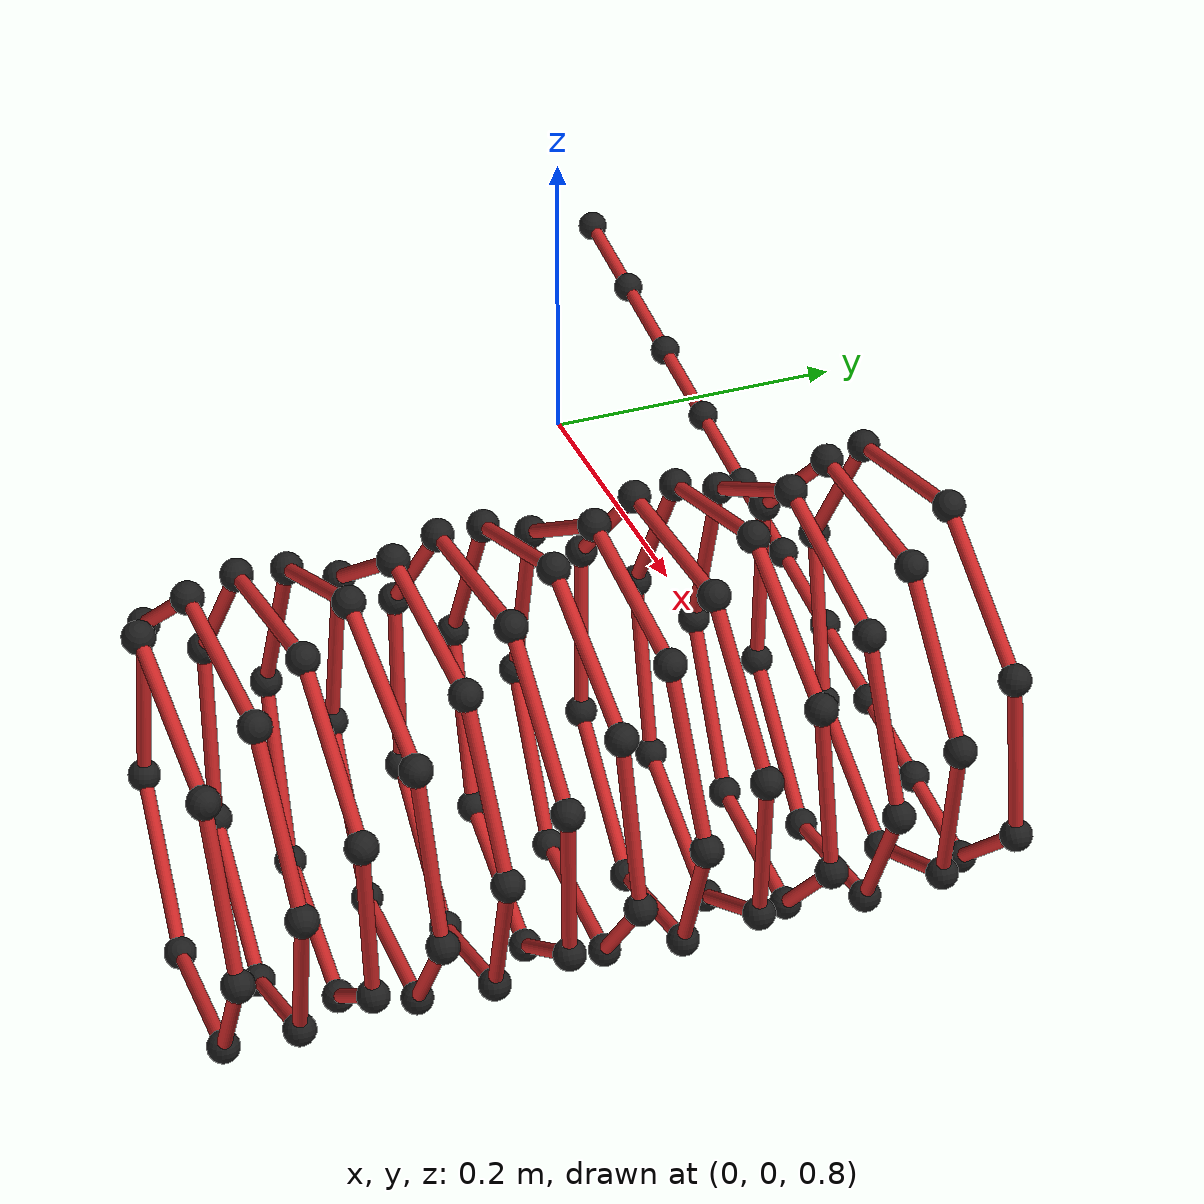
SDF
<?xml version="1.0" ?>
<!-- DO NOT EDIT: Generated from tether.sdf.jinja -->
<sdf version="1.5">
  <model name="tether">
    <pose>0.6 -0.45 1.0 0.0 0.0 0.0</pose>

      <link name="link_0"><gravity>true</gravity>
        <pose>0.0 0.0 0.12 0.0 0.4292148860725228 0.05440359912342107</pose>
        <inertial>
          <mass>0.010000000000000002</mass>
          <inertia>
            <ixx>0.01</ixx>
            <ixy>0</ixy>
            <ixz>0</ixz>
            <iyy>0.01</iyy>
            <iyz>0</iyz>
            <izz>0.01</izz>
          </inertia>
        </inertial><collision name="collision">
          <pose>0.05 0 0 0 1.570790 0</pose>
          <geometry>
          <cylinder>
            <length>0.11</length>
            <radius>0.005</radius>
          </cylinder>
        </geometry>
          <surface>
            <contact>
              <ode>
            <min_depth>0.00005</min_depth>
            <kp>500.0</kp>
            <kd>10.0</kd>
              </ode>
            </contact>
            <friction>
              <ode>
            <mu>3.0</mu>
            <mu2>3.0</mu2>
              </ode>
            </friction>
          </surface>
        </collision>
        <self_collide>false</self_collide>
            <visual name="element_visual">
          <pose>0.05 0 0 0 1.570790 0</pose>
          <geometry>
          <cylinder>
            <length>0.1</length>
            <radius>0.004</radius>
          </cylinder>
        </geometry>
          <material>
          <script>
            <name>Gazebo/Red</name>
            <uri>file://media/materials/scripts/gazebo.material</uri>
          </script>
        </material>
        </visual><visual name="sphere_visual">
          <geometry>
          <sphere>
            <radius>0.009</radius>
          </sphere>
        </geometry>
          <material>
          <script>
            <name>Gazebo/Black</name>
            <uri>file://media/materials/scripts/gazebo.material</uri>
          </script>
        </material>
        </visual>
      </link>
      <plugin name="link_0_drag" filename="libLiftDragPlugin.so">
      <robotNamespace></robotNamespace>
      <a0>0</a0>
      <cla>0</cla>
      <cda>1.2535816618911175</cda>
      <alpha_stall>0</alpha_stall>
      <cda_stall>1.4326647564469914</cda_stall>
      <cp>0 0 0</cp>
      <area>0.0008</area>
      <air_density>1.2041</air_density>
      <forward>0 1 0</forward>
      <upward>0 0 1</upward><link_name>link_0</link_name></plugin>

      <link name="link_1"><gravity>true</gravity>
        <pose>0.09090593428863095 0.0049504950495049506 0.07833333333333332 0.0 1.2851266679610185 0.17637215353435787</pose>
        <inertial>
          <mass>0.010000000000000002</mass>
          <inertia>
            <ixx>0.01</ixx>
            <ixy>0</ixy>
            <ixz>0</ixz>
            <iyy>0.01</iyy>
            <iyz>0</iyz>
            <izz>0.01</izz>
          </inertia>
        </inertial><collision name="collision">
          <pose>0.05 0 0 0 1.570790 0</pose>
          <geometry>
          <cylinder>
            <length>0.11</length>
            <radius>0.005</radius>
          </cylinder>
        </geometry>
          <surface>
            <contact>
              <ode>
            <min_depth>0.00005</min_depth>
            <kp>500.0</kp>
            <kd>10.0</kd>
              </ode>
            </contact>
            <friction>
              <ode>
            <mu>3.0</mu>
            <mu2>3.0</mu2>
              </ode>
            </friction>
          </surface>
        </collision>
        <self_collide>false</self_collide>
            <visual name="element_visual">
          <pose>0.05 0 0 0 1.570790 0</pose>
          <geometry>
          <cylinder>
            <length>0.1</length>
            <radius>0.004</radius>
          </cylinder>
        </geometry>
          <material>
          <script>
            <name>Gazebo/Red</name>
            <uri>file://media/materials/scripts/gazebo.material</uri>
          </script>
        </material>
        </visual><visual name="sphere_visual">
          <geometry>
          <sphere>
            <radius>0.009</radius>
          </sphere>
        </geometry>
          <material>
          <script>
            <name>Gazebo/Black</name>
            <uri>file://media/materials/scripts/gazebo.material</uri>
          </script>
        </material>
        </visual>
      </link>
      <plugin name="link_1_drag" filename="libLiftDragPlugin.so">
      <robotNamespace></robotNamespace>
      <a0>0</a0>
      <cla>0</cla>
      <cda>1.2535816618911175</cda>
      <alpha_stall>0</alpha_stall>
      <cda_stall>1.4326647564469914</cda_stall>
      <cp>0 0 0</cp>
      <area>0.0008</area>
      <air_density>1.2041</air_density>
      <forward>0 1 0</forward>
      <upward>0 0 1</upward><link_name>link_1</link_name></plugin>

      <link name="link_2"><gravity>true</gravity>
        <pose>0.11868274754349041 0.009900990099009901 -0.017731481481481497 0.0 0.9908434604938947 3.051240213324627</pose>
        <inertial>
          <mass>0.010000000000000002</mass>
          <inertia>
            <ixx>0.01</ixx>
            <ixy>0</ixy>
            <ixz>0</ixz>
            <iyy>0.01</iyy>
            <iyz>0</iyz>
            <izz>0.01</izz>
          </inertia>
        </inertial><collision name="collision">
          <pose>0.05 0 0 0 1.570790 0</pose>
          <geometry>
          <cylinder>
            <length>0.11</length>
            <radius>0.005</radius>
          </cylinder>
        </geometry>
          <surface>
            <contact>
              <ode>
            <min_depth>0.00005</min_depth>
            <kp>500.0</kp>
            <kd>10.0</kd>
              </ode>
            </contact>
            <friction>
              <ode>
            <mu>3.0</mu>
            <mu2>3.0</mu2>
              </ode>
            </friction>
          </surface>
        </collision>
        <self_collide>false</self_collide>
            <visual name="element_visual">
          <pose>0.05 0 0 0 1.570790 0</pose>
          <geometry>
          <cylinder>
            <length>0.1</length>
            <radius>0.004</radius>
          </cylinder>
        </geometry>
          <material>
          <script>
            <name>Gazebo/Red</name>
            <uri>file://media/materials/scripts/gazebo.material</uri>
          </script>
        </material>
        </visual><visual name="sphere_visual">
          <geometry>
          <sphere>
            <radius>0.009</radius>
          </sphere>
        </geometry>
          <material>
          <script>
            <name>Gazebo/Black</name>
            <uri>file://media/materials/scripts/gazebo.material</uri>
          </script>
        </material>
        </visual>
      </link>
      <plugin name="link_2_drag" filename="libLiftDragPlugin.so">
      <robotNamespace></robotNamespace>
      <a0>0</a0>
      <cla>0</cla>
      <cda>1.2535816618911175</cda>
      <alpha_stall>0</alpha_stall>
      <cda_stall>1.4326647564469914</cda_stall>
      <cp>0 0 0</cp>
      <area>0.0008</area>
      <air_density>1.2041</air_density>
      <forward>0 1 0</forward>
      <upward>0 0 1</upward><link_name>link_2</link_name></plugin>

      <link name="link_3"><gravity>true</gravity>
        <pose>0.06404098611537037 0.01485148514851485 -0.10148276748971195 0.0 0.13300078998187959 3.0916869778507268</pose>
        <inertial>
          <mass>0.010000000000000002</mass>
          <inertia>
            <ixx>0.01</ixx>
            <ixy>0</ixy>
            <ixz>0</ixz>
            <iyy>0.01</iyy>
            <iyz>0</iyz>
            <izz>0.01</izz>
          </inertia>
        </inertial><collision name="collision">
          <pose>0.05 0 0 0 1.570790 0</pose>
          <geometry>
          <cylinder>
            <length>0.11</length>
            <radius>0.005</radius>
          </cylinder>
        </geometry>
          <surface>
            <contact>
              <ode>
            <min_depth>0.00005</min_depth>
            <kp>500.0</kp>
            <kd>10.0</kd>
              </ode>
            </contact>
            <friction>
              <ode>
            <mu>3.0</mu>
            <mu2>3.0</mu2>
              </ode>
            </friction>
          </surface>
        </collision>
        <self_collide>false</self_collide>
            <visual name="element_visual">
          <pose>0.05 0 0 0 1.570790 0</pose>
          <geometry>
          <cylinder>
            <length>0.1</length>
            <radius>0.004</radius>
          </cylinder>
        </geometry>
          <material>
          <script>
            <name>Gazebo/Red</name>
            <uri>file://media/materials/scripts/gazebo.material</uri>
          </script>
        </material>
        </visual><visual name="sphere_visual">
          <geometry>
          <sphere>
            <radius>0.009</radius>
          </sphere>
        </geometry>
          <material>
          <script>
            <name>Gazebo/Black</name>
            <uri>file://media/materials/scripts/gazebo.material</uri>
          </script>
        </material>
        </visual>
      </link>
      <plugin name="link_3_drag" filename="libLiftDragPlugin.so">
      <robotNamespace></robotNamespace>
      <a0>0</a0>
      <cla>0</cla>
      <cda>1.2535816618911175</cda>
      <alpha_stall>0</alpha_stall>
      <cda_stall>1.4326647564469914</cda_stall>
      <cp>0 0 0</cp>
      <area>0.0008</area>
      <air_density>1.2041</air_density>
      <forward>0 1 0</forward>
      <upward>0 0 1</upward><link_name>link_3</link_name></plugin>

      <link name="link_4"><gravity>true</gravity>
        <pose>-0.035073682337312395 0.019801980198019802 -0.11475990940786465 0.0 -0.7253000927444427 3.0754688741639304</pose>
        <inertial>
          <mass>0.010000000000000002</mass>
          <inertia>
            <ixx>0.01</ixx>
            <ixy>0</ixy>
            <ixz>0</ixz>
            <iyy>0.01</iyy>
            <iyz>0</iyz>
            <izz>0.01</izz>
          </inertia>
        </inertial><collision name="collision">
          <pose>0.05 0 0 0 1.570790 0</pose>
          <geometry>
          <cylinder>
            <length>0.11</length>
            <radius>0.005</radius>
          </cylinder>
        </geometry>
          <surface>
            <contact>
              <ode>
            <min_depth>0.00005</min_depth>
            <kp>500.0</kp>
            <kd>10.0</kd>
              </ode>
            </contact>
            <friction>
              <ode>
            <mu>3.0</mu>
            <mu2>3.0</mu2>
              </ode>
            </friction>
          </surface>
        </collision>
        <self_collide>false</self_collide>
            <visual name="element_visual">
          <pose>0.05 0 0 0 1.570790 0</pose>
          <geometry>
          <cylinder>
            <length>0.1</length>
            <radius>0.004</radius>
          </cylinder>
        </geometry>
          <material>
          <script>
            <name>Gazebo/Red</name>
            <uri>file://media/materials/scripts/gazebo.material</uri>
          </script>
        </material>
        </visual><visual name="sphere_visual">
          <geometry>
          <sphere>
            <radius>0.009</radius>
          </sphere>
        </geometry>
          <material>
          <script>
            <name>Gazebo/Black</name>
            <uri>file://media/materials/scripts/gazebo.material</uri>
          </script>
        </material>
        </visual>
      </link>
      <plugin name="link_4_drag" filename="libLiftDragPlugin.so">
      <robotNamespace></robotNamespace>
      <a0>0</a0>
      <cla>0</cla>
      <cda>1.2535816618911175</cda>
      <alpha_stall>0</alpha_stall>
      <cda_stall>1.4326647564469914</cda_stall>
      <cp>0 0 0</cp>
      <area>0.0008</area>
      <air_density>1.2041</air_density>
      <forward>0 1 0</forward>
      <upward>0 0 1</upward><link_name>link_4</link_name></plugin>

      <link name="link_5"><gravity>true</gravity>
        <pose>-0.10983162694463935 0.024752475247524754 -0.048342669792778 0.0 -1.519068198267288 1.2739979303853441</pose>
        <inertial>
          <mass>0.010000000000000002</mass>
          <inertia>
            <ixx>0.01</ixx>
            <ixy>0</ixy>
            <ixz>0</ixz>
            <iyy>0.01</iyy>
            <iyz>0</iyz>
            <izz>0.01</izz>
          </inertia>
        </inertial><collision name="collision">
          <pose>0.05 0 0 0 1.570790 0</pose>
          <geometry>
          <cylinder>
            <length>0.11</length>
            <radius>0.005</radius>
          </cylinder>
        </geometry>
          <surface>
            <contact>
              <ode>
            <min_depth>0.00005</min_depth>
            <kp>500.0</kp>
            <kd>10.0</kd>
              </ode>
            </contact>
            <friction>
              <ode>
            <mu>3.0</mu>
            <mu2>3.0</mu2>
              </ode>
            </friction>
          </surface>
        </collision>
        <self_collide>false</self_collide>
            <visual name="element_visual">
          <pose>0.05 0 0 0 1.570790 0</pose>
          <geometry>
          <cylinder>
            <length>0.1</length>
            <radius>0.004</radius>
          </cylinder>
        </geometry>
          <material>
          <script>
            <name>Gazebo/Red</name>
            <uri>file://media/materials/scripts/gazebo.material</uri>
          </script>
        </material>
        </visual><visual name="sphere_visual">
          <geometry>
          <sphere>
            <radius>0.009</radius>
          </sphere>
        </geometry>
          <material>
          <script>
            <name>Gazebo/Black</name>
            <uri>file://media/materials/scripts/gazebo.material</uri>
          </script>
        </material>
        </visual>
      </link>
      <plugin name="link_5_drag" filename="libLiftDragPlugin.so">
      <robotNamespace></robotNamespace>
      <a0>0</a0>
      <cla>0</cla>
      <cda>1.2535816618911175</cda>
      <alpha_stall>0</alpha_stall>
      <cda_stall>1.4326647564469914</cda_stall>
      <cp>0 0 0</cp>
      <area>0.0008</area>
      <air_density>1.2041</air_density>
      <forward>0 1 0</forward>
      <upward>0 0 1</upward><link_name>link_5</link_name></plugin>

      <link name="link_6"><gravity>true</gravity>
        <pose>-0.10831760839596674 0.0297029702970297 0.051645868289515624 0.0 -0.6950830323816297 0.06442524300154802</pose>
        <inertial>
          <mass>0.010000000000000002</mass>
          <inertia>
            <ixx>0.01</ixx>
            <ixy>0</ixy>
            <ixz>0</ixz>
            <iyy>0.01</iyy>
            <iyz>0</iyz>
            <izz>0.01</izz>
          </inertia>
        </inertial><collision name="collision">
          <pose>0.05 0 0 0 1.570790 0</pose>
          <geometry>
          <cylinder>
            <length>0.11</length>
            <radius>0.005</radius>
          </cylinder>
        </geometry>
          <surface>
            <contact>
              <ode>
            <min_depth>0.00005</min_depth>
            <kp>500.0</kp>
            <kd>10.0</kd>
              </ode>
            </contact>
            <friction>
              <ode>
            <mu>3.0</mu>
            <mu2>3.0</mu2>
              </ode>
            </friction>
          </surface>
        </collision>
        <self_collide>false</self_collide>
            <visual name="element_visual">
          <pose>0.05 0 0 0 1.570790 0</pose>
          <geometry>
          <cylinder>
            <length>0.1</length>
            <radius>0.004</radius>
          </cylinder>
        </geometry>
          <material>
          <script>
            <name>Gazebo/Red</name>
            <uri>file://media/materials/scripts/gazebo.material</uri>
          </script>
        </material>
        </visual><visual name="sphere_visual">
          <geometry>
          <sphere>
            <radius>0.009</radius>
          </sphere>
        </geometry>
          <material>
          <script>
            <name>Gazebo/Black</name>
            <uri>file://media/materials/scripts/gazebo.material</uri>
          </script>
        </material>
        </visual>
      </link>
      <plugin name="link_6_drag" filename="libLiftDragPlugin.so">
      <robotNamespace></robotNamespace>
      <a0>0</a0>
      <cla>0</cla>
      <cda>1.2535816618911175</cda>
      <alpha_stall>0</alpha_stall>
      <cda_stall>1.4326647564469914</cda_stall>
      <cp>0 0 0</cp>
      <area>0.0008</area>
      <air_density>1.2041</air_density>
      <forward>0 1 0</forward>
      <upward>0 0 1</upward><link_name>link_6</link_name></plugin>

      <link name="link_7"><gravity>true</gravity>
        <pose>-0.03158302846120615 0.034653465346534656 0.11576922005964556 0.0 0.16324445163943455 0.05013160666979454</pose>
        <inertial>
          <mass>0.010000000000000002</mass>
          <inertia>
            <ixx>0.01</ixx>
            <ixy>0</ixy>
            <ixz>0</ixz>
            <iyy>0.01</iyy>
            <iyz>0</iyz>
            <izz>0.01</izz>
          </inertia>
        </inertial><collision name="collision">
          <pose>0.05 0 0 0 1.570790 0</pose>
          <geometry>
          <cylinder>
            <length>0.11</length>
            <radius>0.005</radius>
          </cylinder>
        </geometry>
          <surface>
            <contact>
              <ode>
            <min_depth>0.00005</min_depth>
            <kp>500.0</kp>
            <kd>10.0</kd>
              </ode>
            </contact>
            <friction>
              <ode>
            <mu>3.0</mu>
            <mu2>3.0</mu2>
              </ode>
            </friction>
          </surface>
        </collision>
        <self_collide>false</self_collide>
            <visual name="element_visual">
          <pose>0.05 0 0 0 1.570790 0</pose>
          <geometry>
          <cylinder>
            <length>0.1</length>
            <radius>0.004</radius>
          </cylinder>
        </geometry>
          <material>
          <script>
            <name>Gazebo/Red</name>
            <uri>file://media/materials/scripts/gazebo.material</uri>
          </script>
        </material>
        </visual><visual name="sphere_visual">
          <geometry>
          <sphere>
            <radius>0.009</radius>
          </sphere>
        </geometry>
          <material>
          <script>
            <name>Gazebo/Black</name>
            <uri>file://media/materials/scripts/gazebo.material</uri>
          </script>
        </material>
        </visual>
      </link>
      <plugin name="link_7_drag" filename="libLiftDragPlugin.so">
      <robotNamespace></robotNamespace>
      <a0>0</a0>
      <cla>0</cla>
      <cda>1.2535816618911175</cda>
      <alpha_stall>0</alpha_stall>
      <cda_stall>1.4326647564469914</cda_stall>
      <cp>0 0 0</cp>
      <area>0.0008</area>
      <air_density>1.2041</air_density>
      <forward>0 1 0</forward>
      <upward>0 0 1</upward><link_name>link_7</link_name></plugin>

      <link name="link_8"><gravity>true</gravity>
        <pose>0.06708421012716988 0.039603960396039604 0.09949728012168833 0.0 1.0209954558193364 0.09476906156506877</pose>
        <inertial>
          <mass>0.010000000000000002</mass>
          <inertia>
            <ixx>0.01</ixx>
            <ixy>0</ixy>
            <ixz>0</ixz>
            <iyy>0.01</iyy>
            <iyz>0</iyz>
            <izz>0.01</izz>
          </inertia>
        </inertial><collision name="collision">
          <pose>0.05 0 0 0 1.570790 0</pose>
          <geometry>
          <cylinder>
            <length>0.11</length>
            <radius>0.005</radius>
          </cylinder>
        </geometry>
          <surface>
            <contact>
              <ode>
            <min_depth>0.00005</min_depth>
            <kp>500.0</kp>
            <kd>10.0</kd>
              </ode>
            </contact>
            <friction>
              <ode>
            <mu>3.0</mu>
            <mu2>3.0</mu2>
              </ode>
            </friction>
          </surface>
        </collision>
        <self_collide>false</self_collide>
            <visual name="element_visual">
          <pose>0.05 0 0 0 1.570790 0</pose>
          <geometry>
          <cylinder>
            <length>0.1</length>
            <radius>0.004</radius>
          </cylinder>
        </geometry>
          <material>
          <script>
            <name>Gazebo/Red</name>
            <uri>file://media/materials/scripts/gazebo.material</uri>
          </script>
        </material>
        </visual><visual name="sphere_visual">
          <geometry>
          <sphere>
            <radius>0.009</radius>
          </sphere>
        </geometry>
          <material>
          <script>
            <name>Gazebo/Black</name>
            <uri>file://media/materials/scripts/gazebo.material</uri>
          </script>
        </material>
        </visual>
      </link>
      <plugin name="link_8_drag" filename="libLiftDragPlugin.so">
      <robotNamespace></robotNamespace>
      <a0>0</a0>
      <cla>0</cla>
      <cda>1.2535816618911175</cda>
      <alpha_stall>0</alpha_stall>
      <cda_stall>1.4326647564469914</cda_stall>
      <cp>0 0 0</cp>
      <area>0.0008</area>
      <air_density>1.2041</air_density>
      <forward>0 1 0</forward>
      <upward>0 0 1</upward><link_name>link_8</link_name></plugin>

      <link name="link_9"><gravity>true</gravity>
        <pose>0.11916519168278901 0.04455445544554455 0.014130006765891916 0.0 1.2552713949799572 2.9815747464662765</pose>
        <inertial>
          <mass>0.010000000000000002</mass>
          <inertia>
            <ixx>0.01</ixx>
            <ixy>0</ixy>
            <ixz>0</ixz>
            <iyy>0.01</iyy>
            <iyz>0</iyz>
            <izz>0.01</izz>
          </inertia>
        </inertial><collision name="collision">
          <pose>0.05 0 0 0 1.570790 0</pose>
          <geometry>
          <cylinder>
            <length>0.11</length>
            <radius>0.005</radius>
          </cylinder>
        </geometry>
          <surface>
            <contact>
              <ode>
            <min_depth>0.00005</min_depth>
            <kp>500.0</kp>
            <kd>10.0</kd>
              </ode>
            </contact>
            <friction>
              <ode>
            <mu>3.0</mu>
            <mu2>3.0</mu2>
              </ode>
            </friction>
          </surface>
        </collision>
        <self_collide>false</self_collide>
            <visual name="element_visual">
          <pose>0.05 0 0 0 1.570790 0</pose>
          <geometry>
          <cylinder>
            <length>0.1</length>
            <radius>0.004</radius>
          </cylinder>
        </geometry>
          <material>
          <script>
            <name>Gazebo/Red</name>
            <uri>file://media/materials/scripts/gazebo.material</uri>
          </script>
        </material>
        </visual><visual name="sphere_visual">
          <geometry>
          <sphere>
            <radius>0.009</radius>
          </sphere>
        </geometry>
          <material>
          <script>
            <name>Gazebo/Black</name>
            <uri>file://media/materials/scripts/gazebo.material</uri>
          </script>
        </material>
        </visual>
      </link>
      <plugin name="link_9_drag" filename="libLiftDragPlugin.so">
      <robotNamespace></robotNamespace>
      <a0>0</a0>
      <cla>0</cla>
      <cda>1.2535816618911175</cda>
      <alpha_stall>0</alpha_stall>
      <cda_stall>1.4326647564469914</cda_stall>
      <cp>0 0 0</cp>
      <area>0.0008</area>
      <air_density>1.2041</air_density>
      <forward>0 1 0</forward>
      <upward>0 0 1</upward><link_name>link_9</link_name></plugin>

      <link name="link_10"><gravity>true</gravity>
        <pose>0.08849256790313799 0.04950495049504951 -0.08104977128844047 0.0 0.39897756130921336 3.087908034136305</pose>
        <inertial>
          <mass>0.010000000000000002</mass>
          <inertia>
            <ixx>0.01</ixx>
            <ixy>0</ixy>
            <ixz>0</ixz>
            <iyy>0.01</iyy>
            <iyz>0</iyz>
            <izz>0.01</izz>
          </inertia>
        </inertial><collision name="collision">
          <pose>0.05 0 0 0 1.570790 0</pose>
          <geometry>
          <cylinder>
            <length>0.11</length>
            <radius>0.005</radius>
          </cylinder>
        </geometry>
          <surface>
            <contact>
              <ode>
            <min_depth>0.00005</min_depth>
            <kp>500.0</kp>
            <kd>10.0</kd>
              </ode>
            </contact>
            <friction>
              <ode>
            <mu>3.0</mu>
            <mu2>3.0</mu2>
              </ode>
            </friction>
          </surface>
        </collision>
        <self_collide>false</self_collide>
            <visual name="element_visual">
          <pose>0.05 0 0 0 1.570790 0</pose>
          <geometry>
          <cylinder>
            <length>0.1</length>
            <radius>0.004</radius>
          </cylinder>
        </geometry>
          <material>
          <script>
            <name>Gazebo/Red</name>
            <uri>file://media/materials/scripts/gazebo.material</uri>
          </script>
        </material>
        </visual><visual name="sphere_visual">
          <geometry>
          <sphere>
            <radius>0.009</radius>
          </sphere>
        </geometry>
          <material>
          <script>
            <name>Gazebo/Black</name>
            <uri>file://media/materials/scripts/gazebo.material</uri>
          </script>
        </material>
        </visual>
      </link>
      <plugin name="link_10_drag" filename="libLiftDragPlugin.so">
      <robotNamespace></robotNamespace>
      <a0>0</a0>
      <cla>0</cla>
      <cda>1.2535816618911175</cda>
      <alpha_stall>0</alpha_stall>
      <cda_stall>1.4326647564469914</cda_stall>
      <cp>0 0 0</cp>
      <area>0.0008</area>
      <air_density>1.2041</air_density>
      <forward>0 1 0</forward>
      <upward>0 0 1</upward><link_name>link_10</link_name></plugin>

      <link name="link_11"><gravity>true</gravity>
        <pose>-0.0036332280314699053 0.054455445544554455 -0.1199449859480226 0.0 -0.4594509689443271 3.086399383952713</pose>
        <inertial>
          <mass>0.010000000000000002</mass>
          <inertia>
            <ixx>0.01</ixx>
            <ixy>0</ixy>
            <ixz>0</ixz>
            <iyy>0.01</iyy>
            <iyz>0</iyz>
            <izz>0.01</izz>
          </inertia>
        </inertial><collision name="collision">
          <pose>0.05 0 0 0 1.570790 0</pose>
          <geometry>
          <cylinder>
            <length>0.11</length>
            <radius>0.005</radius>
          </cylinder>
        </geometry>
          <surface>
            <contact>
              <ode>
            <min_depth>0.00005</min_depth>
            <kp>500.0</kp>
            <kd>10.0</kd>
              </ode>
            </contact>
            <friction>
              <ode>
            <mu>3.0</mu>
            <mu2>3.0</mu2>
              </ode>
            </friction>
          </surface>
        </collision>
        <self_collide>false</self_collide>
            <visual name="element_visual">
          <pose>0.05 0 0 0 1.570790 0</pose>
          <geometry>
          <cylinder>
            <length>0.1</length>
            <radius>0.004</radius>
          </cylinder>
        </geometry>
          <material>
          <script>
            <name>Gazebo/Red</name>
            <uri>file://media/materials/scripts/gazebo.material</uri>
          </script>
        </material>
        </visual><visual name="sphere_visual">
          <geometry>
          <sphere>
            <radius>0.009</radius>
          </sphere>
        </geometry>
          <material>
          <script>
            <name>Gazebo/Black</name>
            <uri>file://media/materials/scripts/gazebo.material</uri>
          </script>
        </material>
        </visual>
      </link>
      <plugin name="link_11_drag" filename="libLiftDragPlugin.so">
      <robotNamespace></robotNamespace>
      <a0>0</a0>
      <cla>0</cla>
      <cda>1.2535816618911175</cda>
      <alpha_stall>0</alpha_stall>
      <cda_stall>1.4326647564469914</cda_stall>
      <cp>0 0 0</cp>
      <area>0.0008</area>
      <air_density>1.2041</air_density>
      <forward>0 1 0</forward>
      <upward>0 0 1</upward><link_name>link_11</link_name></plugin>

      <link name="link_12"><gravity>true</gravity>
        <pose>-0.09323594894422384 0.0594059405940594 -0.07554507147703339 0.0 -1.314884773971312 2.9449945892080023</pose>
        <inertial>
          <mass>0.010000000000000002</mass>
          <inertia>
            <ixx>0.01</ixx>
            <ixy>0</ixy>
            <ixz>0</ixz>
            <iyy>0.01</iyy>
            <iyz>0</iyz>
            <izz>0.01</izz>
          </inertia>
        </inertial><collision name="collision">
          <pose>0.05 0 0 0 1.570790 0</pose>
          <geometry>
          <cylinder>
            <length>0.11</length>
            <radius>0.005</radius>
          </cylinder>
        </geometry>
          <surface>
            <contact>
              <ode>
            <min_depth>0.00005</min_depth>
            <kp>500.0</kp>
            <kd>10.0</kd>
              </ode>
            </contact>
            <friction>
              <ode>
            <mu>3.0</mu>
            <mu2>3.0</mu2>
              </ode>
            </friction>
          </surface>
        </collision>
        <self_collide>false</self_collide>
            <visual name="element_visual">
          <pose>0.05 0 0 0 1.570790 0</pose>
          <geometry>
          <cylinder>
            <length>0.1</length>
            <radius>0.004</radius>
          </cylinder>
        </geometry>
          <material>
          <script>
            <name>Gazebo/Red</name>
            <uri>file://media/materials/scripts/gazebo.material</uri>
          </script>
        </material>
        </visual><visual name="sphere_visual">
          <geometry>
          <sphere>
            <radius>0.009</radius>
          </sphere>
        </geometry>
          <material>
          <script>
            <name>Gazebo/Black</name>
            <uri>file://media/materials/scripts/gazebo.material</uri>
          </script>
        </material>
        </visual>
      </link>
      <plugin name="link_12_drag" filename="libLiftDragPlugin.so">
      <robotNamespace></robotNamespace>
      <a0>0</a0>
      <cla>0</cla>
      <cda>1.2535816618911175</cda>
      <alpha_stall>0</alpha_stall>
      <cda_stall>1.4326647564469914</cda_stall>
      <cp>0 0 0</cp>
      <area>0.0008</area>
      <air_density>1.2041</air_density>
      <forward>0 1 0</forward>
      <upward>0 0 1</upward><link_name>link_12</link_name></plugin>

      <link name="link_13"><gravity>true</gravity>
        <pose>-0.11809148309015552 0.06435643564356436 0.021316698186340053 0.0 -0.9606800382788808 0.0864034761671844</pose>
        <inertial>
          <mass>0.010000000000000002</mass>
          <inertia>
            <ixx>0.01</ixx>
            <ixy>0</ixy>
            <ixz>0</ixz>
            <iyy>0.01</iyy>
            <iyz>0</iyz>
            <izz>0.01</izz>
          </inertia>
        </inertial><collision name="collision">
          <pose>0.05 0 0 0 1.570790 0</pose>
          <geometry>
          <cylinder>
            <length>0.11</length>
            <radius>0.005</radius>
          </cylinder>
        </geometry>
          <surface>
            <contact>
              <ode>
            <min_depth>0.00005</min_depth>
            <kp>500.0</kp>
            <kd>10.0</kd>
              </ode>
            </contact>
            <friction>
              <ode>
            <mu>3.0</mu>
            <mu2>3.0</mu2>
              </ode>
            </friction>
          </surface>
        </collision>
        <self_collide>false</self_collide>
            <visual name="element_visual">
          <pose>0.05 0 0 0 1.570790 0</pose>
          <geometry>
          <cylinder>
            <length>0.1</length>
            <radius>0.004</radius>
          </cylinder>
        </geometry>
          <material>
          <script>
            <name>Gazebo/Red</name>
            <uri>file://media/materials/scripts/gazebo.material</uri>
          </script>
        </material>
        </visual><visual name="sphere_visual">
          <geometry>
          <sphere>
            <radius>0.009</radius>
          </sphere>
        </geometry>
          <material>
          <script>
            <name>Gazebo/Black</name>
            <uri>file://media/materials/scripts/gazebo.material</uri>
          </script>
        </material>
        </visual>
      </link>
      <plugin name="link_13_drag" filename="libLiftDragPlugin.so">
      <robotNamespace></robotNamespace>
      <a0>0</a0>
      <cla>0</cla>
      <cda>1.2535816618911175</cda>
      <alpha_stall>0</alpha_stall>
      <cda_stall>1.4326647564469914</cda_stall>
      <cp>0 0 0</cp>
      <area>0.0008</area>
      <air_density>1.2041</air_density>
      <forward>0 1 0</forward>
      <upward>0 0 1</upward><link_name>link_13</link_name></plugin>

      <link name="link_14"><gravity>true</gravity>
        <pose>-0.060939042867923725 0.06930693069306931 0.1033752052203107 0.0 -0.10275682283755544 0.049727085653569494</pose>
        <inertial>
          <mass>0.010000000000000002</mass>
          <inertia>
            <ixx>0.01</ixx>
            <ixy>0</ixy>
            <ixz>0</ixz>
            <iyy>0.01</iyy>
            <iyz>0</iyz>
            <izz>0.01</izz>
          </inertia>
        </inertial><collision name="collision">
          <pose>0.05 0 0 0 1.570790 0</pose>
          <geometry>
          <cylinder>
            <length>0.11</length>
            <radius>0.005</radius>
          </cylinder>
        </geometry>
          <surface>
            <contact>
              <ode>
            <min_depth>0.00005</min_depth>
            <kp>500.0</kp>
            <kd>10.0</kd>
              </ode>
            </contact>
            <friction>
              <ode>
            <mu>3.0</mu>
            <mu2>3.0</mu2>
              </ode>
            </friction>
          </surface>
        </collision>
        <self_collide>false</self_collide>
            <visual name="element_visual">
          <pose>0.05 0 0 0 1.570790 0</pose>
          <geometry>
          <cylinder>
            <length>0.1</length>
            <radius>0.004</radius>
          </cylinder>
        </geometry>
          <material>
          <script>
            <name>Gazebo/Red</name>
            <uri>file://media/materials/scripts/gazebo.material</uri>
          </script>
        </material>
        </visual><visual name="sphere_visual">
          <geometry>
          <sphere>
            <radius>0.009</radius>
          </sphere>
        </geometry>
          <material>
          <script>
            <name>Gazebo/Black</name>
            <uri>file://media/materials/scripts/gazebo.material</uri>
          </script>
        </material>
        </visual>
      </link>
      <plugin name="link_14_drag" filename="libLiftDragPlugin.so">
      <robotNamespace></robotNamespace>
      <a0>0</a0>
      <cla>0</cla>
      <cda>1.2535816618911175</cda>
      <alpha_stall>0</alpha_stall>
      <cda_stall>1.4326647564469914</cda_stall>
      <cp>0 0 0</cp>
      <area>0.0008</area>
      <air_density>1.2041</air_density>
      <forward>0 1 0</forward>
      <upward>0 0 1</upward><link_name>link_14</link_name></plugin>

      <link name="link_15"><gravity>true</gravity>
        <pose>0.03853217712369969 0.07425742574257425 0.11364537529573226 0.0 0.75551359935642 0.06797798663230059</pose>
        <inertial>
          <mass>0.010000000000000002</mass>
          <inertia>
            <ixx>0.01</ixx>
            <ixy>0</ixy>
            <ixz>0</ixz>
            <iyy>0.01</iyy>
            <iyz>0</iyz>
            <izz>0.01</izz>
          </inertia>
        </inertial><collision name="collision">
          <pose>0.05 0 0 0 1.570790 0</pose>
          <geometry>
          <cylinder>
            <length>0.11</length>
            <radius>0.005</radius>
          </cylinder>
        </geometry>
          <surface>
            <contact>
              <ode>
            <min_depth>0.00005</min_depth>
            <kp>500.0</kp>
            <kd>10.0</kd>
              </ode>
            </contact>
            <friction>
              <ode>
            <mu>3.0</mu>
            <mu2>3.0</mu2>
              </ode>
            </friction>
          </surface>
        </collision>
        <self_collide>false</self_collide>
            <visual name="element_visual">
          <pose>0.05 0 0 0 1.570790 0</pose>
          <geometry>
          <cylinder>
            <length>0.1</length>
            <radius>0.004</radius>
          </cylinder>
        </geometry>
          <material>
          <script>
            <name>Gazebo/Red</name>
            <uri>file://media/materials/scripts/gazebo.material</uri>
          </script>
        </material>
        </visual><visual name="sphere_visual">
          <geometry>
          <sphere>
            <radius>0.009</radius>
          </sphere>
        </geometry>
          <material>
          <script>
            <name>Gazebo/Black</name>
            <uri>file://media/materials/scripts/gazebo.material</uri>
          </script>
        </material>
        </visual>
      </link>
      <plugin name="link_15_drag" filename="libLiftDragPlugin.so">
      <robotNamespace></robotNamespace>
      <a0>0</a0>
      <cla>0</cla>
      <cda>1.2535816618911175</cda>
      <alpha_stall>0</alpha_stall>
      <cda_stall>1.4326647564469914</cda_stall>
      <cp>0 0 0</cp>
      <area>0.0008</area>
      <air_density>1.2041</air_density>
      <forward>0 1 0</forward>
      <upward>0 0 1</upward><link_name>link_15</link_name></plugin>

      <link name="link_16"><gravity>true</gravity>
        <pose>0.11124494077942039 0.07920792079207921 0.04499514586022861 0.0 1.5036528613830822 2.313041379622099</pose>
        <inertial>
          <mass>0.010000000000000002</mass>
          <inertia>
            <ixx>0.01</ixx>
            <ixy>0</ixy>
            <ixz>0</ixz>
            <iyy>0.01</iyy>
            <iyz>0</iyz>
            <izz>0.01</izz>
          </inertia>
        </inertial><collision name="collision">
          <pose>0.05 0 0 0 1.570790 0</pose>
          <geometry>
          <cylinder>
            <length>0.11</length>
            <radius>0.005</radius>
          </cylinder>
        </geometry>
          <surface>
            <contact>
              <ode>
            <min_depth>0.00005</min_depth>
            <kp>500.0</kp>
            <kd>10.0</kd>
              </ode>
            </contact>
            <friction>
              <ode>
            <mu>3.0</mu>
            <mu2>3.0</mu2>
              </ode>
            </friction>
          </surface>
        </collision>
        <self_collide>false</self_collide>
            <visual name="element_visual">
          <pose>0.05 0 0 0 1.570790 0</pose>
          <geometry>
          <cylinder>
            <length>0.1</length>
            <radius>0.004</radius>
          </cylinder>
        </geometry>
          <material>
          <script>
            <name>Gazebo/Red</name>
            <uri>file://media/materials/scripts/gazebo.material</uri>
          </script>
        </material>
        </visual><visual name="sphere_visual">
          <geometry>
          <sphere>
            <radius>0.009</radius>
          </sphere>
        </geometry>
          <material>
          <script>
            <name>Gazebo/Black</name>
            <uri>file://media/materials/scripts/gazebo.material</uri>
          </script>
        </material>
        </visual>
      </link>
      <plugin name="link_16_drag" filename="libLiftDragPlugin.so">
      <robotNamespace></robotNamespace>
      <a0>0</a0>
      <cla>0</cla>
      <cda>1.2535816618911175</cda>
      <alpha_stall>0</alpha_stall>
      <cda_stall>1.4326647564469914</cda_stall>
      <cp>0 0 0</cp>
      <area>0.0008</area>
      <air_density>1.2041</air_density>
      <forward>0 1 0</forward>
      <upward>0 0 1</upward><link_name>link_16</link_name></plugin>

      <link name="link_17"><gravity>true</gravity>
        <pose>0.10670427333832146 0.08415841584158416 -0.054901712644878205 0.0 0.664862798580956 3.0787249347874988</pose>
        <inertial>
          <mass>0.010000000000000002</mass>
          <inertia>
            <ixx>0.01</ixx>
            <ixy>0</ixy>
            <ixz>0</ixz>
            <iyy>0.01</iyy>
            <iyz>0</iyz>
            <izz>0.01</izz>
          </inertia>
        </inertial><collision name="collision">
          <pose>0.05 0 0 0 1.570790 0</pose>
          <geometry>
          <cylinder>
            <length>0.11</length>
            <radius>0.005</radius>
          </cylinder>
        </geometry>
          <surface>
            <contact>
              <ode>
            <min_depth>0.00005</min_depth>
            <kp>500.0</kp>
            <kd>10.0</kd>
              </ode>
            </contact>
            <friction>
              <ode>
            <mu>3.0</mu>
            <mu2>3.0</mu2>
              </ode>
            </friction>
          </surface>
        </collision>
        <self_collide>false</self_collide>
            <visual name="element_visual">
          <pose>0.05 0 0 0 1.570790 0</pose>
          <geometry>
          <cylinder>
            <length>0.1</length>
            <radius>0.004</radius>
          </cylinder>
        </geometry>
          <material>
          <script>
            <name>Gazebo/Red</name>
            <uri>file://media/materials/scripts/gazebo.material</uri>
          </script>
        </material>
        </visual><visual name="sphere_visual">
          <geometry>
          <sphere>
            <radius>0.009</radius>
          </sphere>
        </geometry>
          <material>
          <script>
            <name>Gazebo/Black</name>
            <uri>file://media/materials/scripts/gazebo.material</uri>
          </script>
        </material>
        </visual>
      </link>
      <plugin name="link_17_drag" filename="libLiftDragPlugin.so">
      <robotNamespace></robotNamespace>
      <a0>0</a0>
      <cla>0</cla>
      <cda>1.2535816618911175</cda>
      <alpha_stall>0</alpha_stall>
      <cda_stall>1.4326647564469914</cda_stall>
      <cp>0 0 0</cp>
      <area>0.0008</area>
      <air_density>1.2041</air_density>
      <forward>0 1 0</forward>
      <upward>0 0 1</upward><link_name>link_17</link_name></plugin>

      <link name="link_18"><gravity>true</gravity>
        <pose>0.028063416078943602 0.0891089108910891 -0.11667238181326414 0.0 -0.1934877337977245 3.091186713478123</pose>
        <inertial>
          <mass>0.010000000000000002</mass>
          <inertia>
            <ixx>0.01</ixx>
            <ixy>0</ixy>
            <ixz>0</ixz>
            <iyy>0.01</iyy>
            <iyz>0</iyz>
            <izz>0.01</izz>
          </inertia>
        </inertial><collision name="collision">
          <pose>0.05 0 0 0 1.570790 0</pose>
          <geometry>
          <cylinder>
            <length>0.11</length>
            <radius>0.005</radius>
          </cylinder>
        </geometry>
          <surface>
            <contact>
              <ode>
            <min_depth>0.00005</min_depth>
            <kp>500.0</kp>
            <kd>10.0</kd>
              </ode>
            </contact>
            <friction>
              <ode>
            <mu>3.0</mu>
            <mu2>3.0</mu2>
              </ode>
            </friction>
          </surface>
        </collision>
        <self_collide>false</self_collide>
            <visual name="element_visual">
          <pose>0.05 0 0 0 1.570790 0</pose>
          <geometry>
          <cylinder>
            <length>0.1</length>
            <radius>0.004</radius>
          </cylinder>
        </geometry>
          <material>
          <script>
            <name>Gazebo/Red</name>
            <uri>file://media/materials/scripts/gazebo.material</uri>
          </script>
        </material>
        </visual><visual name="sphere_visual">
          <geometry>
          <sphere>
            <radius>0.009</radius>
          </sphere>
        </geometry>
          <material>
          <script>
            <name>Gazebo/Black</name>
            <uri>file://media/materials/scripts/gazebo.material</uri>
          </script>
        </material>
        </visual>
      </link>
      <plugin name="link_18_drag" filename="libLiftDragPlugin.so">
      <robotNamespace></robotNamespace>
      <a0>0</a0>
      <cla>0</cla>
      <cda>1.2535816618911175</cda>
      <alpha_stall>0</alpha_stall>
      <cda_stall>1.4326647564469914</cda_stall>
      <cp>0 0 0</cp>
      <area>0.0008</area>
      <air_density>1.2041</air_density>
      <forward>0 1 0</forward>
      <upward>0 0 1</upward><link_name>link_18</link_name></plugin>

      <link name="link_19"><gravity>true</gravity>
        <pose>-0.07006592456858941 0.09405940594059406 -0.09742056361132766 0.0 -1.0511340123440478 3.0418589549982005</pose>
        <inertial>
          <mass>0.010000000000000002</mass>
          <inertia>
            <ixx>0.01</ixx>
            <ixy>0</ixy>
            <ixz>0</ixz>
            <iyy>0.01</iyy>
            <iyz>0</iyz>
            <izz>0.01</izz>
          </inertia>
        </inertial><collision name="collision">
          <pose>0.05 0 0 0 1.570790 0</pose>
          <geometry>
          <cylinder>
            <length>0.11</length>
            <radius>0.005</radius>
          </cylinder>
        </geometry>
          <surface>
            <contact>
              <ode>
            <min_depth>0.00005</min_depth>
            <kp>500.0</kp>
            <kd>10.0</kd>
              </ode>
            </contact>
            <friction>
              <ode>
            <mu>3.0</mu>
            <mu2>3.0</mu2>
              </ode>
            </friction>
          </surface>
        </collision>
        <self_collide>false</self_collide>
            <visual name="element_visual">
          <pose>0.05 0 0 0 1.570790 0</pose>
          <geometry>
          <cylinder>
            <length>0.1</length>
            <radius>0.004</radius>
          </cylinder>
        </geometry>
          <material>
          <script>
            <name>Gazebo/Red</name>
            <uri>file://media/materials/scripts/gazebo.material</uri>
          </script>
        </material>
        </visual><visual name="sphere_visual">
          <geometry>
          <sphere>
            <radius>0.009</radius>
          </sphere>
        </geometry>
          <material>
          <script>
            <name>Gazebo/Black</name>
            <uri>file://media/materials/scripts/gazebo.material</uri>
          </script>
        </material>
        </visual>
      </link>
      <plugin name="link_19_drag" filename="libLiftDragPlugin.so">
      <robotNamespace></robotNamespace>
      <a0>0</a0>
      <cla>0</cla>
      <cda>1.2535816618911175</cda>
      <alpha_stall>0</alpha_stall>
      <cda_stall>1.4326647564469914</cda_stall>
      <cp>0 0 0</cp>
      <area>0.0008</area>
      <air_density>1.2041</air_density>
      <forward>0 1 0</forward>
      <upward>0 0 1</upward><link_name>link_19</link_name></plugin>

      <link name="link_20"><gravity>true</gravity>
        <pose>-0.11953837315460206 0.09900990099009901 -0.010515576234858142 0.0 -1.2253441629328112 0.14654033831943827</pose>
        <inertial>
          <mass>0.010000000000000002</mass>
          <inertia>
            <ixx>0.01</ixx>
            <ixy>0</ixy>
            <ixz>0</ixz>
            <iyy>0.01</iyy>
            <iyz>0</iyz>
            <izz>0.01</izz>
          </inertia>
        </inertial><collision name="collision">
          <pose>0.05 0 0 0 1.570790 0</pose>
          <geometry>
          <cylinder>
            <length>0.11</length>
            <radius>0.005</radius>
          </cylinder>
        </geometry>
          <surface>
            <contact>
              <ode>
            <min_depth>0.00005</min_depth>
            <kp>500.0</kp>
            <kd>10.0</kd>
              </ode>
            </contact>
            <friction>
              <ode>
            <mu>3.0</mu>
            <mu2>3.0</mu2>
              </ode>
            </friction>
          </surface>
        </collision>
        <self_collide>false</self_collide>
            <visual name="element_visual">
          <pose>0.05 0 0 0 1.570790 0</pose>
          <geometry>
          <cylinder>
            <length>0.1</length>
            <radius>0.004</radius>
          </cylinder>
        </geometry>
          <material>
          <script>
            <name>Gazebo/Red</name>
            <uri>file://media/materials/scripts/gazebo.material</uri>
          </script>
        </material>
        </visual><visual name="sphere_visual">
          <geometry>
          <sphere>
            <radius>0.009</radius>
          </sphere>
        </geometry>
          <material>
          <script>
            <name>Gazebo/Black</name>
            <uri>file://media/materials/scripts/gazebo.material</uri>
          </script>
        </material>
        </visual>
      </link>
      <plugin name="link_20_drag" filename="libLiftDragPlugin.so">
      <robotNamespace></robotNamespace>
      <a0>0</a0>
      <cla>0</cla>
      <cda>1.2535816618911175</cda>
      <alpha_stall>0</alpha_stall>
      <cda_stall>1.4326647564469914</cda_stall>
      <cp>0 0 0</cp>
      <area>0.0008</area>
      <air_density>1.2041</air_density>
      <forward>0 1 0</forward>
      <upward>0 0 1</upward><link_name>link_20</link_name></plugin>

      <link name="link_21"><gravity>true</gravity>
        <pose>-0.08599806260547446 0.10396039603960396 0.08369189463804062 0.0 -0.3687391226050731 0.05303227803502818</pose>
        <inertial>
          <mass>0.010000000000000002</mass>
          <inertia>
            <ixx>0.01</ixx>
            <ixy>0</ixy>
            <ixz>0</ixz>
            <iyy>0.01</iyy>
            <iyz>0</iyz>
            <izz>0.01</izz>
          </inertia>
        </inertial><collision name="collision">
          <pose>0.05 0 0 0 1.570790 0</pose>
          <geometry>
          <cylinder>
            <length>0.11</length>
            <radius>0.005</radius>
          </cylinder>
        </geometry>
          <surface>
            <contact>
              <ode>
            <min_depth>0.00005</min_depth>
            <kp>500.0</kp>
            <kd>10.0</kd>
              </ode>
            </contact>
            <friction>
              <ode>
            <mu>3.0</mu>
            <mu2>3.0</mu2>
              </ode>
            </friction>
          </surface>
        </collision>
        <self_collide>false</self_collide>
            <visual name="element_visual">
          <pose>0.05 0 0 0 1.570790 0</pose>
          <geometry>
          <cylinder>
            <length>0.1</length>
            <radius>0.004</radius>
          </cylinder>
        </geometry>
          <material>
          <script>
            <name>Gazebo/Red</name>
            <uri>file://media/materials/scripts/gazebo.material</uri>
          </script>
        </material>
        </visual><visual name="sphere_visual">
          <geometry>
          <sphere>
            <radius>0.009</radius>
          </sphere>
        </geometry>
          <material>
          <script>
            <name>Gazebo/Black</name>
            <uri>file://media/materials/scripts/gazebo.material</uri>
          </script>
        </material>
        </visual>
      </link>
      <plugin name="link_21_drag" filename="libLiftDragPlugin.so">
      <robotNamespace></robotNamespace>
      <a0>0</a0>
      <cla>0</cla>
      <cda>1.2535816618911175</cda>
      <alpha_stall>0</alpha_stall>
      <cda_stall>1.4326647564469914</cda_stall>
      <cp>0 0 0</cp>
      <area>0.0008</area>
      <air_density>1.2041</air_density>
      <forward>0 1 0</forward>
      <upward>0 0 1</upward><link_name>link_21</link_name></plugin>

      <link name="link_22"><gravity>true</gravity>
        <pose>0.007263124753010327 0.10891089108910891 0.11977999423452235 0.0 0.4896856700081437 0.05605822706796414</pose>
        <inertial>
          <mass>0.010000000000000002</mass>
          <inertia>
            <ixx>0.01</ixx>
            <ixy>0</ixy>
            <ixz>0</ixz>
            <iyy>0.01</iyy>
            <iyz>0</iyz>
            <izz>0.01</izz>
          </inertia>
        </inertial><collision name="collision">
          <pose>0.05 0 0 0 1.570790 0</pose>
          <geometry>
          <cylinder>
            <length>0.11</length>
            <radius>0.005</radius>
          </cylinder>
        </geometry>
          <surface>
            <contact>
              <ode>
            <min_depth>0.00005</min_depth>
            <kp>500.0</kp>
            <kd>10.0</kd>
              </ode>
            </contact>
            <friction>
              <ode>
            <mu>3.0</mu>
            <mu2>3.0</mu2>
              </ode>
            </friction>
          </surface>
        </collision>
        <self_collide>false</self_collide>
            <visual name="element_visual">
          <pose>0.05 0 0 0 1.570790 0</pose>
          <geometry>
          <cylinder>
            <length>0.1</length>
            <radius>0.004</radius>
          </cylinder>
        </geometry>
          <material>
          <script>
            <name>Gazebo/Red</name>
            <uri>file://media/materials/scripts/gazebo.material</uri>
          </script>
        </material>
        </visual><visual name="sphere_visual">
          <geometry>
          <sphere>
            <radius>0.009</radius>
          </sphere>
        </geometry>
          <material>
          <script>
            <name>Gazebo/Black</name>
            <uri>file://media/materials/scripts/gazebo.material</uri>
          </script>
        </material>
        </visual>
      </link>
      <plugin name="link_22_drag" filename="libLiftDragPlugin.so">
      <robotNamespace></robotNamespace>
      <a0>0</a0>
      <cla>0</cla>
      <cda>1.2535816618911175</cda>
      <alpha_stall>0</alpha_stall>
      <cda_stall>1.4326647564469914</cda_stall>
      <cp>0 0 0</cp>
      <area>0.0008</area>
      <air_density>1.2041</air_density>
      <forward>0 1 0</forward>
      <upward>0 0 1</upward><link_name>link_22</link_name></plugin>

      <link name="link_23"><gravity>true</gravity>
        <pose>0.09548047547746044 0.11386138613861387 0.07268754227925218 0.0 1.344507353910677 0.22220109316810102</pose>
        <inertial>
          <mass>0.010000000000000002</mass>
          <inertia>
            <ixx>0.01</ixx>
            <ixy>0</ixy>
            <ixz>0</ixz>
            <iyy>0.01</iyy>
            <iyz>0</iyz>
            <izz>0.01</izz>
          </inertia>
        </inertial><collision name="collision">
          <pose>0.05 0 0 0 1.570790 0</pose>
          <geometry>
          <cylinder>
            <length>0.11</length>
            <radius>0.005</radius>
          </cylinder>
        </geometry>
          <surface>
            <contact>
              <ode>
            <min_depth>0.00005</min_depth>
            <kp>500.0</kp>
            <kd>10.0</kd>
              </ode>
            </contact>
            <friction>
              <ode>
            <mu>3.0</mu>
            <mu2>3.0</mu2>
              </ode>
            </friction>
          </surface>
        </collision>
        <self_collide>false</self_collide>
            <visual name="element_visual">
          <pose>0.05 0 0 0 1.570790 0</pose>
          <geometry>
          <cylinder>
            <length>0.1</length>
            <radius>0.004</radius>
          </cylinder>
        </geometry>
          <material>
          <script>
            <name>Gazebo/Red</name>
            <uri>file://media/materials/scripts/gazebo.material</uri>
          </script>
        </material>
        </visual><visual name="sphere_visual">
          <geometry>
          <sphere>
            <radius>0.009</radius>
          </sphere>
        </geometry>
          <material>
          <script>
            <name>Gazebo/Black</name>
            <uri>file://media/materials/scripts/gazebo.material</uri>
          </script>
        </material>
        </visual>
      </link>
      <plugin name="link_23_drag" filename="libLiftDragPlugin.so">
      <robotNamespace></robotNamespace>
      <a0>0</a0>
      <cla>0</cla>
      <cda>1.2535816618911175</cda>
      <alpha_stall>0</alpha_stall>
      <cda_stall>1.4326647564469914</cda_stall>
      <cp>0 0 0</cp>
      <area>0.0008</area>
      <air_density>1.2041</air_density>
      <forward>0 1 0</forward>
      <upward>0 0 1</upward><link_name>link_23</link_name></plugin>

      <link name="link_24"><gravity>true</gravity>
        <pose>0.11739194045367378 0.1188118811881188 -0.024882369592165242 0.0 0.9305068239948519 3.0587357216329463</pose>
        <inertial>
          <mass>0.010000000000000002</mass>
          <inertia>
            <ixx>0.01</ixx>
            <ixy>0</ixy>
            <ixz>0</ixz>
            <iyy>0.01</iyy>
            <iyz>0</iyz>
            <izz>0.01</izz>
          </inertia>
        </inertial><collision name="collision">
          <pose>0.05 0 0 0 1.570790 0</pose>
          <geometry>
          <cylinder>
            <length>0.11</length>
            <radius>0.005</radius>
          </cylinder>
        </geometry>
          <surface>
            <contact>
              <ode>
            <min_depth>0.00005</min_depth>
            <kp>500.0</kp>
            <kd>10.0</kd>
              </ode>
            </contact>
            <friction>
              <ode>
            <mu>3.0</mu>
            <mu2>3.0</mu2>
              </ode>
            </friction>
          </surface>
        </collision>
        <self_collide>false</self_collide>
            <visual name="element_visual">
          <pose>0.05 0 0 0 1.570790 0</pose>
          <geometry>
          <cylinder>
            <length>0.1</length>
            <radius>0.004</radius>
          </cylinder>
        </geometry>
          <material>
          <script>
            <name>Gazebo/Red</name>
            <uri>file://media/materials/scripts/gazebo.material</uri>
          </script>
        </material>
        </visual><visual name="sphere_visual">
          <geometry>
          <sphere>
            <radius>0.009</radius>
          </sphere>
        </geometry>
          <material>
          <script>
            <name>Gazebo/Black</name>
            <uri>file://media/materials/scripts/gazebo.material</uri>
          </script>
        </material>
        </visual>
      </link>
      <plugin name="link_24_drag" filename="libLiftDragPlugin.so">
      <robotNamespace></robotNamespace>
      <a0>0</a0>
      <cla>0</cla>
      <cda>1.2535816618911175</cda>
      <alpha_stall>0</alpha_stall>
      <cda_stall>1.4326647564469914</cda_stall>
      <cp>0 0 0</cp>
      <area>0.0008</area>
      <air_density>1.2041</air_density>
      <forward>0 1 0</forward>
      <upward>0 0 1</upward><link_name>link_24</link_name></plugin>

      <link name="link_25"><gravity>true</gravity>
        <pose>0.05778122455928041 0.12376237623762376 -0.10517285813569016 0.0 0.07251262191954368 3.0919976483098566</pose>
        <inertial>
          <mass>0.010000000000000002</mass>
          <inertia>
            <ixx>0.01</ixx>
            <ixy>0</ixy>
            <ixz>0</ixz>
            <iyy>0.01</iyy>
            <iyz>0</iyz>
            <izz>0.01</izz>
          </inertia>
        </inertial><collision name="collision">
          <pose>0.05 0 0 0 1.570790 0</pose>
          <geometry>
          <cylinder>
            <length>0.11</length>
            <radius>0.005</radius>
          </cylinder>
        </geometry>
          <surface>
            <contact>
              <ode>
            <min_depth>0.00005</min_depth>
            <kp>500.0</kp>
            <kd>10.0</kd>
              </ode>
            </contact>
            <friction>
              <ode>
            <mu>3.0</mu>
            <mu2>3.0</mu2>
              </ode>
            </friction>
          </surface>
        </collision>
        <self_collide>false</self_collide>
            <visual name="element_visual">
          <pose>0.05 0 0 0 1.570790 0</pose>
          <geometry>
          <cylinder>
            <length>0.1</length>
            <radius>0.004</radius>
          </cylinder>
        </geometry>
          <material>
          <script>
            <name>Gazebo/Red</name>
            <uri>file://media/materials/scripts/gazebo.material</uri>
          </script>
        </material>
        </visual><visual name="sphere_visual">
          <geometry>
          <sphere>
            <radius>0.009</radius>
          </sphere>
        </geometry>
          <material>
          <script>
            <name>Gazebo/Black</name>
            <uri>file://media/materials/scripts/gazebo.material</uri>
          </script>
        </material>
        </visual>
      </link>
      <plugin name="link_25_drag" filename="libLiftDragPlugin.so">
      <robotNamespace></robotNamespace>
      <a0>0</a0>
      <cla>0</cla>
      <cda>1.2535816618911175</cda>
      <alpha_stall>0</alpha_stall>
      <cda_stall>1.4326647564469914</cda_stall>
      <cp>0 0 0</cp>
      <area>0.0008</area>
      <air_density>1.2041</air_density>
      <forward>0 1 0</forward>
      <upward>0 0 1</upward><link_name>link_25</link_name></plugin>

      <link name="link_26"><gravity>true</gravity>
        <pose>-0.041955341723502085 0.12871287128712872 -0.11242663964054145 0.0 -0.7857231151124121 3.071587814868584</pose>
        <inertial>
          <mass>0.010000000000000002</mass>
          <inertia>
            <ixx>0.01</ixx>
            <ixy>0</ixy>
            <ixz>0</ixz>
            <iyy>0.01</iyy>
            <iyz>0</iyz>
            <izz>0.01</izz>
          </inertia>
        </inertial><collision name="collision">
          <pose>0.05 0 0 0 1.570790 0</pose>
          <geometry>
          <cylinder>
            <length>0.11</length>
            <radius>0.005</radius>
          </cylinder>
        </geometry>
          <surface>
            <contact>
              <ode>
            <min_depth>0.00005</min_depth>
            <kp>500.0</kp>
            <kd>10.0</kd>
              </ode>
            </contact>
            <friction>
              <ode>
            <mu>3.0</mu>
            <mu2>3.0</mu2>
              </ode>
            </friction>
          </surface>
        </collision>
        <self_collide>false</self_collide>
            <visual name="element_visual">
          <pose>0.05 0 0 0 1.570790 0</pose>
          <geometry>
          <cylinder>
            <length>0.1</length>
            <radius>0.004</radius>
          </cylinder>
        </geometry>
          <material>
          <script>
            <name>Gazebo/Red</name>
            <uri>file://media/materials/scripts/gazebo.material</uri>
          </script>
        </material>
        </visual><visual name="sphere_visual">
          <geometry>
          <sphere>
            <radius>0.009</radius>
          </sphere>
        </geometry>
          <material>
          <script>
            <name>Gazebo/Black</name>
            <uri>file://media/materials/scripts/gazebo.material</uri>
          </script>
        </material>
        </visual>
      </link>
      <plugin name="link_26_drag" filename="libLiftDragPlugin.so">
      <robotNamespace></robotNamespace>
      <a0>0</a0>
      <cla>0</cla>
      <cda>1.2535816618911175</cda>
      <alpha_stall>0</alpha_stall>
      <cda_stall>1.4326647564469914</cda_stall>
      <cp>0 0 0</cp>
      <area>0.0008</area>
      <air_density>1.2041</air_density>
      <forward>0 1 0</forward>
      <upward>0 0 1</upward><link_name>link_26</link_name></plugin>

      <link name="link_27"><gravity>true</gravity>
        <pose>-0.11255625403163039 0.13366336633663367 -0.04160636583946124 0.0 -1.4803909332443588 0.5795702459454626</pose>
        <inertial>
          <mass>0.010000000000000002</mass>
          <inertia>
            <ixx>0.01</ixx>
            <ixy>0</ixy>
            <ixz>0</ixz>
            <iyy>0.01</iyy>
            <iyz>0</iyz>
            <izz>0.01</izz>
          </inertia>
        </inertial><collision name="collision">
          <pose>0.05 0 0 0 1.570790 0</pose>
          <geometry>
          <cylinder>
            <length>0.11</length>
            <radius>0.005</radius>
          </cylinder>
        </geometry>
          <surface>
            <contact>
              <ode>
            <min_depth>0.00005</min_depth>
            <kp>500.0</kp>
            <kd>10.0</kd>
              </ode>
            </contact>
            <friction>
              <ode>
            <mu>3.0</mu>
            <mu2>3.0</mu2>
              </ode>
            </friction>
          </surface>
        </collision>
        <self_collide>false</self_collide>
            <visual name="element_visual">
          <pose>0.05 0 0 0 1.570790 0</pose>
          <geometry>
          <cylinder>
            <length>0.1</length>
            <radius>0.004</radius>
          </cylinder>
        </geometry>
          <material>
          <script>
            <name>Gazebo/Red</name>
            <uri>file://media/materials/scripts/gazebo.material</uri>
          </script>
        </material>
        </visual><visual name="sphere_visual">
          <geometry>
          <sphere>
            <radius>0.009</radius>
          </sphere>
        </geometry>
          <material>
          <script>
            <name>Gazebo/Black</name>
            <uri>file://media/materials/scripts/gazebo.material</uri>
          </script>
        </material>
        </visual>
      </link>
      <plugin name="link_27_drag" filename="libLiftDragPlugin.so">
      <robotNamespace></robotNamespace>
      <a0>0</a0>
      <cla>0</cla>
      <cda>1.2535816618911175</cda>
      <alpha_stall>0</alpha_stall>
      <cda_stall>1.4326647564469914</cda_stall>
      <cp>0 0 0</cp>
      <area>0.0008</area>
      <air_density>1.2041</air_density>
      <forward>0 1 0</forward>
      <upward>0 0 1</upward><link_name>link_27</link_name></plugin>

      <link name="link_28"><gravity>true</gravity>
        <pose>-0.10499310104001545 0.13861386138613863 0.0581072175723559 0.0 -0.6346397241016593 0.0614384946656551</pose>
        <inertial>
          <mass>0.010000000000000002</mass>
          <inertia>
            <ixx>0.01</ixx>
            <ixy>0</ixy>
            <ixz>0</ixz>
            <iyy>0.01</iyy>
            <iyz>0</iyz>
            <izz>0.01</izz>
          </inertia>
        </inertial><collision name="collision">
          <pose>0.05 0 0 0 1.570790 0</pose>
          <geometry>
          <cylinder>
            <length>0.11</length>
            <radius>0.005</radius>
          </cylinder>
        </geometry>
          <surface>
            <contact>
              <ode>
            <min_depth>0.00005</min_depth>
            <kp>500.0</kp>
            <kd>10.0</kd>
              </ode>
            </contact>
            <friction>
              <ode>
            <mu>3.0</mu>
            <mu2>3.0</mu2>
              </ode>
            </friction>
          </surface>
        </collision>
        <self_collide>false</self_collide>
            <visual name="element_visual">
          <pose>0.05 0 0 0 1.570790 0</pose>
          <geometry>
          <cylinder>
            <length>0.1</length>
            <radius>0.004</radius>
          </cylinder>
        </geometry>
          <material>
          <script>
            <name>Gazebo/Red</name>
            <uri>file://media/materials/scripts/gazebo.material</uri>
          </script>
        </material>
        </visual><visual name="sphere_visual">
          <geometry>
          <sphere>
            <radius>0.009</radius>
          </sphere>
        </geometry>
          <material>
          <script>
            <name>Gazebo/Black</name>
            <uri>file://media/materials/scripts/gazebo.material</uri>
          </script>
        </material>
        </visual>
      </link>
      <plugin name="link_28_drag" filename="libLiftDragPlugin.so">
      <robotNamespace></robotNamespace>
      <a0>0</a0>
      <cla>0</cla>
      <cda>1.2535816618911175</cda>
      <alpha_stall>0</alpha_stall>
      <cda_stall>1.4326647564469914</cda_stall>
      <cp>0 0 0</cp>
      <area>0.0008</area>
      <air_density>1.2041</air_density>
      <forward>0 1 0</forward>
      <upward>0 0 1</upward><link_name>link_28</link_name></plugin>

      <link name="link_29"><gravity>true</gravity>
        <pose>-0.02451807232616722 0.14356435643564355 0.11746856655892603 0.0 0.22373055954919924 0.05072998058520926</pose>
        <inertial>
          <mass>0.010000000000000002</mass>
          <inertia>
            <ixx>0.01</ixx>
            <ixy>0</ixy>
            <ixz>0</ixz>
            <iyy>0.01</iyy>
            <iyz>0</iyz>
            <izz>0.01</izz>
          </inertia>
        </inertial><collision name="collision">
          <pose>0.05 0 0 0 1.570790 0</pose>
          <geometry>
          <cylinder>
            <length>0.11</length>
            <radius>0.005</radius>
          </cylinder>
        </geometry>
          <surface>
            <contact>
              <ode>
            <min_depth>0.00005</min_depth>
            <kp>500.0</kp>
            <kd>10.0</kd>
              </ode>
            </contact>
            <friction>
              <ode>
            <mu>3.0</mu>
            <mu2>3.0</mu2>
              </ode>
            </friction>
          </surface>
        </collision>
        <self_collide>false</self_collide>
            <visual name="element_visual">
          <pose>0.05 0 0 0 1.570790 0</pose>
          <geometry>
          <cylinder>
            <length>0.1</length>
            <radius>0.004</radius>
          </cylinder>
        </geometry>
          <material>
          <script>
            <name>Gazebo/Red</name>
            <uri>file://media/materials/scripts/gazebo.material</uri>
          </script>
        </material>
        </visual><visual name="sphere_visual">
          <geometry>
          <sphere>
            <radius>0.009</radius>
          </sphere>
        </geometry>
          <material>
          <script>
            <name>Gazebo/Black</name>
            <uri>file://media/materials/scripts/gazebo.material</uri>
          </script>
        </material>
        </visual>
      </link>
      <plugin name="link_29_drag" filename="libLiftDragPlugin.so">
      <robotNamespace></robotNamespace>
      <a0>0</a0>
      <cla>0</cla>
      <cda>1.2535816618911175</cda>
      <alpha_stall>0</alpha_stall>
      <cda_stall>1.4326647564469914</cda_stall>
      <cp>0 0 0</cp>
      <area>0.0008</area>
      <air_density>1.2041</air_density>
      <forward>0 1 0</forward>
      <upward>0 0 1</upward><link_name>link_29</link_name></plugin>

      <link name="link_30"><gravity>true</gravity>
        <pose>0.07298339550307469 0.1485148514851485 0.09525452210179723 0.0 1.0812566253818556 0.1053464430776843</pose>
        <inertial>
          <mass>0.010000000000000002</mass>
          <inertia>
            <ixx>0.01</ixx>
            <ixy>0</ixy>
            <ixz>0</ixz>
            <iyy>0.01</iyy>
            <iyz>0</iyz>
            <izz>0.01</izz>
          </inertia>
        </inertial><collision name="collision">
          <pose>0.05 0 0 0 1.570790 0</pose>
          <geometry>
          <cylinder>
            <length>0.11</length>
            <radius>0.005</radius>
          </cylinder>
        </geometry>
          <surface>
            <contact>
              <ode>
            <min_depth>0.00005</min_depth>
            <kp>500.0</kp>
            <kd>10.0</kd>
              </ode>
            </contact>
            <friction>
              <ode>
            <mu>3.0</mu>
            <mu2>3.0</mu2>
              </ode>
            </friction>
          </surface>
        </collision>
        <self_collide>false</self_collide>
            <visual name="element_visual">
          <pose>0.05 0 0 0 1.570790 0</pose>
          <geometry>
          <cylinder>
            <length>0.1</length>
            <radius>0.004</radius>
          </cylinder>
        </geometry>
          <material>
          <script>
            <name>Gazebo/Red</name>
            <uri>file://media/materials/scripts/gazebo.material</uri>
          </script>
        </material>
        </visual><visual name="sphere_visual">
          <geometry>
          <sphere>
            <radius>0.009</radius>
          </sphere>
        </geometry>
          <material>
          <script>
            <name>Gazebo/Black</name>
            <uri>file://media/materials/scripts/gazebo.material</uri>
          </script>
        </material>
        </visual>
      </link>
      <plugin name="link_30_drag" filename="libLiftDragPlugin.so">
      <robotNamespace></robotNamespace>
      <a0>0</a0>
      <cla>0</cla>
      <cda>1.2535816618911175</cda>
      <alpha_stall>0</alpha_stall>
      <cda_stall>1.4326647564469914</cda_stall>
      <cp>0 0 0</cp>
      <area>0.0008</area>
      <air_density>1.2041</air_density>
      <forward>0 1 0</forward>
      <upward>0 0 1</upward><link_name>link_30</link_name></plugin>

      <link name="link_31"><gravity>true</gravity>
        <pose>0.11980194978851479 0.15346534653465346 0.006891503962864875 0.0 1.195362196387241 3.0063358605509953</pose>
        <inertial>
          <mass>0.010000000000000002</mass>
          <inertia>
            <ixx>0.01</ixx>
            <ixy>0</ixy>
            <ixz>0</ixz>
            <iyy>0.01</iyy>
            <iyz>0</iyz>
            <izz>0.01</izz>
          </inertia>
        </inertial><collision name="collision">
          <pose>0.05 0 0 0 1.570790 0</pose>
          <geometry>
          <cylinder>
            <length>0.11</length>
            <radius>0.005</radius>
          </cylinder>
        </geometry>
          <surface>
            <contact>
              <ode>
            <min_depth>0.00005</min_depth>
            <kp>500.0</kp>
            <kd>10.0</kd>
              </ode>
            </contact>
            <friction>
              <ode>
            <mu>3.0</mu>
            <mu2>3.0</mu2>
              </ode>
            </friction>
          </surface>
        </collision>
        <self_collide>false</self_collide>
            <visual name="element_visual">
          <pose>0.05 0 0 0 1.570790 0</pose>
          <geometry>
          <cylinder>
            <length>0.1</length>
            <radius>0.004</radius>
          </cylinder>
        </geometry>
          <material>
          <script>
            <name>Gazebo/Red</name>
            <uri>file://media/materials/scripts/gazebo.material</uri>
          </script>
        </material>
        </visual><visual name="sphere_visual">
          <geometry>
          <sphere>
            <radius>0.009</radius>
          </sphere>
        </geometry>
          <material>
          <script>
            <name>Gazebo/Black</name>
            <uri>file://media/materials/scripts/gazebo.material</uri>
          </script>
        </material>
        </visual>
      </link>
      <plugin name="link_31_drag" filename="libLiftDragPlugin.so">
      <robotNamespace></robotNamespace>
      <a0>0</a0>
      <cla>0</cla>
      <cda>1.2535816618911175</cda>
      <alpha_stall>0</alpha_stall>
      <cda_stall>1.4326647564469914</cda_stall>
      <cp>0 0 0</cp>
      <area>0.0008</area>
      <air_density>1.2041</air_density>
      <forward>0 1 0</forward>
      <upward>0 0 1</upward><link_name>link_31</link_name></plugin>

      <link name="link_32"><gravity>true</gravity>
        <pose>0.08342470560970858 0.15841584158415842 -0.08625728081694586 0.0 0.33849968756673915 3.089149648225688</pose>
        <inertial>
          <mass>0.010000000000000002</mass>
          <inertia>
            <ixx>0.01</ixx>
            <ixy>0</ixy>
            <ixz>0</ixz>
            <iyy>0.01</iyy>
            <iyz>0</iyz>
            <izz>0.01</izz>
          </inertia>
        </inertial><collision name="collision">
          <pose>0.05 0 0 0 1.570790 0</pose>
          <geometry>
          <cylinder>
            <length>0.11</length>
            <radius>0.005</radius>
          </cylinder>
        </geometry>
          <surface>
            <contact>
              <ode>
            <min_depth>0.00005</min_depth>
            <kp>500.0</kp>
            <kd>10.0</kd>
              </ode>
            </contact>
            <friction>
              <ode>
            <mu>3.0</mu>
            <mu2>3.0</mu2>
              </ode>
            </friction>
          </surface>
        </collision>
        <self_collide>false</self_collide>
            <visual name="element_visual">
          <pose>0.05 0 0 0 1.570790 0</pose>
          <geometry>
          <cylinder>
            <length>0.1</length>
            <radius>0.004</radius>
          </cylinder>
        </geometry>
          <material>
          <script>
            <name>Gazebo/Red</name>
            <uri>file://media/materials/scripts/gazebo.material</uri>
          </script>
        </material>
        </visual><visual name="sphere_visual">
          <geometry>
          <sphere>
            <radius>0.009</radius>
          </sphere>
        </geometry>
          <material>
          <script>
            <name>Gazebo/Black</name>
            <uri>file://media/materials/scripts/gazebo.material</uri>
          </script>
        </material>
        </visual>
      </link>
      <plugin name="link_32_drag" filename="libLiftDragPlugin.so">
      <robotNamespace></robotNamespace>
      <a0>0</a0>
      <cla>0</cla>
      <cda>1.2535816618911175</cda>
      <alpha_stall>0</alpha_stall>
      <cda_stall>1.4326647564469914</cda_stall>
      <cp>0 0 0</cp>
      <area>0.0008</area>
      <air_density>1.2041</air_density>
      <forward>0 1 0</forward>
      <upward>0 0 1</upward><link_name>link_32</link_name></plugin>

      <link name="link_33"><gravity>true</gravity>
        <pose>-0.010886361909172955 0.16336633663366337 -0.11950517614054425 0.0 -0.5199188354962588 3.084588971188497</pose>
        <inertial>
          <mass>0.010000000000000002</mass>
          <inertia>
            <ixx>0.01</ixx>
            <ixy>0</ixy>
            <ixz>0</ixz>
            <iyy>0.01</iyy>
            <iyz>0</iyz>
            <izz>0.01</izz>
          </inertia>
        </inertial><collision name="collision">
          <pose>0.05 0 0 0 1.570790 0</pose>
          <geometry>
          <cylinder>
            <length>0.11</length>
            <radius>0.005</radius>
          </cylinder>
        </geometry>
          <surface>
            <contact>
              <ode>
            <min_depth>0.00005</min_depth>
            <kp>500.0</kp>
            <kd>10.0</kd>
              </ode>
            </contact>
            <friction>
              <ode>
            <mu>3.0</mu>
            <mu2>3.0</mu2>
              </ode>
            </friction>
          </surface>
        </collision>
        <self_collide>false</self_collide>
            <visual name="element_visual">
          <pose>0.05 0 0 0 1.570790 0</pose>
          <geometry>
          <cylinder>
            <length>0.1</length>
            <radius>0.004</radius>
          </cylinder>
        </geometry>
          <material>
          <script>
            <name>Gazebo/Red</name>
            <uri>file://media/materials/scripts/gazebo.material</uri>
          </script>
        </material>
        </visual><visual name="sphere_visual">
          <geometry>
          <sphere>
            <radius>0.009</radius>
          </sphere>
        </geometry>
          <material>
          <script>
            <name>Gazebo/Black</name>
            <uri>file://media/materials/scripts/gazebo.material</uri>
          </script>
        </material>
        </visual>
      </link>
      <plugin name="link_33_drag" filename="libLiftDragPlugin.so">
      <robotNamespace></robotNamespace>
      <a0>0</a0>
      <cla>0</cla>
      <cda>1.2535816618911175</cda>
      <alpha_stall>0</alpha_stall>
      <cda_stall>1.4326647564469914</cda_stall>
      <cp>0 0 0</cp>
      <area>0.0008</area>
      <air_density>1.2041</air_density>
      <forward>0 1 0</forward>
      <upward>0 0 1</upward><link_name>link_33</link_name></plugin>

      <link name="link_34"><gravity>true</gravity>
        <pose>-0.09763745588001772 0.16831683168316833 -0.06976336581098701 0.0 -1.3739331969261348 2.8860288267167182</pose>
        <inertial>
          <mass>0.010000000000000002</mass>
          <inertia>
            <ixx>0.01</ixx>
            <ixy>0</ixy>
            <ixz>0</ixz>
            <iyy>0.01</iyy>
            <iyz>0</iyz>
            <izz>0.01</izz>
          </inertia>
        </inertial><collision name="collision">
          <pose>0.05 0 0 0 1.570790 0</pose>
          <geometry>
          <cylinder>
            <length>0.11</length>
            <radius>0.005</radius>
          </cylinder>
        </geometry>
          <surface>
            <contact>
              <ode>
            <min_depth>0.00005</min_depth>
            <kp>500.0</kp>
            <kd>10.0</kd>
              </ode>
            </contact>
            <friction>
              <ode>
            <mu>3.0</mu>
            <mu2>3.0</mu2>
              </ode>
            </friction>
          </surface>
        </collision>
        <self_collide>false</self_collide>
            <visual name="element_visual">
          <pose>0.05 0 0 0 1.570790 0</pose>
          <geometry>
          <cylinder>
            <length>0.1</length>
            <radius>0.004</radius>
          </cylinder>
        </geometry>
          <material>
          <script>
            <name>Gazebo/Red</name>
            <uri>file://media/materials/scripts/gazebo.material</uri>
          </script>
        </material>
        </visual><visual name="sphere_visual">
          <geometry>
          <sphere>
            <radius>0.009</radius>
          </sphere>
        </geometry>
          <material>
          <script>
            <name>Gazebo/Black</name>
            <uri>file://media/materials/scripts/gazebo.material</uri>
          </script>
        </material>
        </visual>
      </link>
      <plugin name="link_34_drag" filename="libLiftDragPlugin.so">
      <robotNamespace></robotNamespace>
      <a0>0</a0>
      <cla>0</cla>
      <cda>1.2535816618911175</cda>
      <alpha_stall>0</alpha_stall>
      <cda_stall>1.4326647564469914</cda_stall>
      <cp>0 0 0</cp>
      <area>0.0008</area>
      <air_density>1.2041</air_density>
      <forward>0 1 0</forward>
      <upward>0 0 1</upward><link_name>link_34</link_name></plugin>

      <link name="link_35"><gravity>true</gravity>
        <pose>-0.11658476104529471 0.17326732673267328 0.028425226331755614 0.0 -0.9003251599902323 0.07965931366429499</pose>
        <inertial>
          <mass>0.010000000000000002</mass>
          <inertia>
            <ixx>0.01</ixx>
            <ixy>0</ixy>
            <ixz>0</ixz>
            <iyy>0.01</iyy>
            <iyz>0</iyz>
            <izz>0.01</izz>
          </inertia>
        </inertial><collision name="collision">
          <pose>0.05 0 0 0 1.570790 0</pose>
          <geometry>
          <cylinder>
            <length>0.11</length>
            <radius>0.005</radius>
          </cylinder>
        </geometry>
          <surface>
            <contact>
              <ode>
            <min_depth>0.00005</min_depth>
            <kp>500.0</kp>
            <kd>10.0</kd>
              </ode>
            </contact>
            <friction>
              <ode>
            <mu>3.0</mu>
            <mu2>3.0</mu2>
              </ode>
            </friction>
          </surface>
        </collision>
        <self_collide>false</self_collide>
            <visual name="element_visual">
          <pose>0.05 0 0 0 1.570790 0</pose>
          <geometry>
          <cylinder>
            <length>0.1</length>
            <radius>0.004</radius>
          </cylinder>
        </geometry>
          <material>
          <script>
            <name>Gazebo/Red</name>
            <uri>file://media/materials/scripts/gazebo.material</uri>
          </script>
        </material>
        </visual><visual name="sphere_visual">
          <geometry>
          <sphere>
            <radius>0.009</radius>
          </sphere>
        </geometry>
          <material>
          <script>
            <name>Gazebo/Black</name>
            <uri>file://media/materials/scripts/gazebo.material</uri>
          </script>
        </material>
        </visual>
      </link>
      <plugin name="link_35_drag" filename="libLiftDragPlugin.so">
      <robotNamespace></robotNamespace>
      <a0>0</a0>
      <cla>0</cla>
      <cda>1.2535816618911175</cda>
      <alpha_stall>0</alpha_stall>
      <cda_stall>1.4326647564469914</cda_stall>
      <cp>0 0 0</cp>
      <area>0.0008</area>
      <air_density>1.2041</air_density>
      <forward>0 1 0</forward>
      <upward>0 0 1</upward><link_name>link_35</link_name></plugin>

      <link name="link_36"><gravity>true</gravity>
        <pose>-0.0545704265957834 0.1782178217821782 0.10687407796633482 0.0 -0.04226825719998843 0.04950882450446275</pose>
        <inertial>
          <mass>0.010000000000000002</mass>
          <inertia>
            <ixx>0.01</ixx>
            <ixy>0</ixy>
            <ixz>0</ixz>
            <iyy>0.01</iyy>
            <iyz>0</iyz>
            <izz>0.01</izz>
          </inertia>
        </inertial><collision name="collision">
          <pose>0.05 0 0 0 1.570790 0</pose>
          <geometry>
          <cylinder>
            <length>0.11</length>
            <radius>0.005</radius>
          </cylinder>
        </geometry>
          <surface>
            <contact>
              <ode>
            <min_depth>0.00005</min_depth>
            <kp>500.0</kp>
            <kd>10.0</kd>
              </ode>
            </contact>
            <friction>
              <ode>
            <mu>3.0</mu>
            <mu2>3.0</mu2>
              </ode>
            </friction>
          </surface>
        </collision>
        <self_collide>false</self_collide>
            <visual name="element_visual">
          <pose>0.05 0 0 0 1.570790 0</pose>
          <geometry>
          <cylinder>
            <length>0.1</length>
            <radius>0.004</radius>
          </cylinder>
        </geometry>
          <material>
          <script>
            <name>Gazebo/Red</name>
            <uri>file://media/materials/scripts/gazebo.material</uri>
          </script>
        </material>
        </visual><visual name="sphere_visual">
          <geometry>
          <sphere>
            <radius>0.009</radius>
          </sphere>
        </geometry>
          <material>
          <script>
            <name>Gazebo/Black</name>
            <uri>file://media/materials/scripts/gazebo.material</uri>
          </script>
        </material>
        </visual>
      </link>
      <plugin name="link_36_drag" filename="libLiftDragPlugin.so">
      <robotNamespace></robotNamespace>
      <a0>0</a0>
      <cla>0</cla>
      <cda>1.2535816618911175</cda>
      <alpha_stall>0</alpha_stall>
      <cda_stall>1.4326647564469914</cda_stall>
      <cp>0 0 0</cp>
      <area>0.0008</area>
      <air_density>1.2041</air_density>
      <forward>0 1 0</forward>
      <upward>0 0 1</upward><link_name>link_36</link_name></plugin>

      <link name="link_37"><gravity>true</gravity>
        <pose>0.04534003743413291 0.18316831683168316 0.11110481990207006 0.0 0.8159281346728252 0.0722240830287221</pose>
        <inertial>
          <mass>0.010000000000000002</mass>
          <inertia>
            <ixx>0.01</ixx>
            <ixy>0</ixy>
            <ixz>0</ixz>
            <iyy>0.01</iyy>
            <iyz>0</iyz>
            <izz>0.01</izz>
          </inertia>
        </inertial><collision name="collision">
          <pose>0.05 0 0 0 1.570790 0</pose>
          <geometry>
          <cylinder>
            <length>0.11</length>
            <radius>0.005</radius>
          </cylinder>
        </geometry>
          <surface>
            <contact>
              <ode>
            <min_depth>0.00005</min_depth>
            <kp>500.0</kp>
            <kd>10.0</kd>
              </ode>
            </contact>
            <friction>
              <ode>
            <mu>3.0</mu>
            <mu2>3.0</mu2>
              </ode>
            </friction>
          </surface>
        </collision>
        <self_collide>false</self_collide>
            <visual name="element_visual">
          <pose>0.05 0 0 0 1.570790 0</pose>
          <geometry>
          <cylinder>
            <length>0.1</length>
            <radius>0.004</radius>
          </cylinder>
        </geometry>
          <material>
          <script>
            <name>Gazebo/Red</name>
            <uri>file://media/materials/scripts/gazebo.material</uri>
          </script>
        </material>
        </visual><visual name="sphere_visual">
          <geometry>
          <sphere>
            <radius>0.009</radius>
          </sphere>
        </geometry>
          <material>
          <script>
            <name>Gazebo/Black</name>
            <uri>file://media/materials/scripts/gazebo.material</uri>
          </script>
        </material>
        </visual>
      </link>
      <plugin name="link_37_drag" filename="libLiftDragPlugin.so">
      <robotNamespace></robotNamespace>
      <a0>0</a0>
      <cla>0</cla>
      <cda>1.2535816618911175</cda>
      <alpha_stall>0</alpha_stall>
      <cda_stall>1.4326647564469914</cda_stall>
      <cp>0 0 0</cp>
      <area>0.0008</area>
      <air_density>1.2041</air_density>
      <forward>0 1 0</forward>
      <upward>0 0 1</upward><link_name>link_37</link_name></plugin>

      <link name="link_38"><gravity>true</gravity>
        <pose>0.1137643643570125 0.18811881188118812 0.03817943690581229 0.0 1.4538755510981192 2.7038974019006354</pose>
        <inertial>
          <mass>0.010000000000000002</mass>
          <inertia>
            <ixx>0.01</ixx>
            <ixy>0</ixy>
            <ixz>0</ixz>
            <iyy>0.01</iyy>
            <iyz>0</iyz>
            <izz>0.01</izz>
          </inertia>
        </inertial><collision name="collision">
          <pose>0.05 0 0 0 1.570790 0</pose>
          <geometry>
          <cylinder>
            <length>0.11</length>
            <radius>0.005</radius>
          </cylinder>
        </geometry>
          <surface>
            <contact>
              <ode>
            <min_depth>0.00005</min_depth>
            <kp>500.0</kp>
            <kd>10.0</kd>
              </ode>
            </contact>
            <friction>
              <ode>
            <mu>3.0</mu>
            <mu2>3.0</mu2>
              </ode>
            </friction>
          </surface>
        </collision>
        <self_collide>false</self_collide>
            <visual name="element_visual">
          <pose>0.05 0 0 0 1.570790 0</pose>
          <geometry>
          <cylinder>
            <length>0.1</length>
            <radius>0.004</radius>
          </cylinder>
        </geometry>
          <material>
          <script>
            <name>Gazebo/Red</name>
            <uri>file://media/materials/scripts/gazebo.material</uri>
          </script>
        </material>
        </visual><visual name="sphere_visual">
          <geometry>
          <sphere>
            <radius>0.009</radius>
          </sphere>
        </geometry>
          <material>
          <script>
            <name>Gazebo/Black</name>
            <uri>file://media/materials/scripts/gazebo.material</uri>
          </script>
        </material>
        </visual>
      </link>
      <plugin name="link_38_drag" filename="libLiftDragPlugin.so">
      <robotNamespace></robotNamespace>
      <a0>0</a0>
      <cla>0</cla>
      <cda>1.2535816618911175</cda>
      <alpha_stall>0</alpha_stall>
      <cda_stall>1.4326647564469914</cda_stall>
      <cp>0 0 0</cp>
      <area>0.0008</area>
      <air_density>1.2041</air_density>
      <forward>0 1 0</forward>
      <upward>0 0 1</upward><link_name>link_38</link_name></plugin>

      <link name="link_39"><gravity>true</gravity>
        <pose>0.10318566047641128 0.19306930693069307 -0.061259443941703996 0.0 0.6044141016654152 3.081466148629929</pose>
        <inertial>
          <mass>0.010000000000000002</mass>
          <inertia>
            <ixx>0.01</ixx>
            <ixy>0</ixy>
            <ixz>0</ixz>
            <iyy>0.01</iyy>
            <iyz>0</iyz>
            <izz>0.01</izz>
          </inertia>
        </inertial><collision name="collision">
          <pose>0.05 0 0 0 1.570790 0</pose>
          <geometry>
          <cylinder>
            <length>0.11</length>
            <radius>0.005</radius>
          </cylinder>
        </geometry>
          <surface>
            <contact>
              <ode>
            <min_depth>0.00005</min_depth>
            <kp>500.0</kp>
            <kd>10.0</kd>
              </ode>
            </contact>
            <friction>
              <ode>
            <mu>3.0</mu>
            <mu2>3.0</mu2>
              </ode>
            </friction>
          </surface>
        </collision>
        <self_collide>false</self_collide>
            <visual name="element_visual">
          <pose>0.05 0 0 0 1.570790 0</pose>
          <geometry>
          <cylinder>
            <length>0.1</length>
            <radius>0.004</radius>
          </cylinder>
        </geometry>
          <material>
          <script>
            <name>Gazebo/Red</name>
            <uri>file://media/materials/scripts/gazebo.material</uri>
          </script>
        </material>
        </visual><visual name="sphere_visual">
          <geometry>
          <sphere>
            <radius>0.009</radius>
          </sphere>
        </geometry>
          <material>
          <script>
            <name>Gazebo/Black</name>
            <uri>file://media/materials/scripts/gazebo.material</uri>
          </script>
        </material>
        </visual>
      </link>
      <plugin name="link_39_drag" filename="libLiftDragPlugin.so">
      <robotNamespace></robotNamespace>
      <a0>0</a0>
      <cla>0</cla>
      <cda>1.2535816618911175</cda>
      <alpha_stall>0</alpha_stall>
      <cda_stall>1.4326647564469914</cda_stall>
      <cp>0 0 0</cp>
      <area>0.0008</area>
      <air_density>1.2041</air_density>
      <forward>0 1 0</forward>
      <upward>0 0 1</upward><link_name>link_39</link_name></plugin>

      <link name="link_40"><gravity>true</gravity>
        <pose>0.02095024793163563 0.19801980198019803 -0.11815704427414811 0.0 -0.2539728484479914 3.0904873627235534</pose>
        <inertial>
          <mass>0.010000000000000002</mass>
          <inertia>
            <ixx>0.01</ixx>
            <ixy>0</ixy>
            <ixz>0</ixz>
            <iyy>0.01</iyy>
            <iyz>0</iyz>
            <izz>0.01</izz>
          </inertia>
        </inertial><collision name="collision">
          <pose>0.05 0 0 0 1.570790 0</pose>
          <geometry>
          <cylinder>
            <length>0.11</length>
            <radius>0.005</radius>
          </cylinder>
        </geometry>
          <surface>
            <contact>
              <ode>
            <min_depth>0.00005</min_depth>
            <kp>500.0</kp>
            <kd>10.0</kd>
              </ode>
            </contact>
            <friction>
              <ode>
            <mu>3.0</mu>
            <mu2>3.0</mu2>
              </ode>
            </friction>
          </surface>
        </collision>
        <self_collide>false</self_collide>
            <visual name="element_visual">
          <pose>0.05 0 0 0 1.570790 0</pose>
          <geometry>
          <cylinder>
            <length>0.1</length>
            <radius>0.004</radius>
          </cylinder>
        </geometry>
          <material>
          <script>
            <name>Gazebo/Red</name>
            <uri>file://media/materials/scripts/gazebo.material</uri>
          </script>
        </material>
        </visual><visual name="sphere_visual">
          <geometry>
          <sphere>
            <radius>0.009</radius>
          </sphere>
        </geometry>
          <material>
          <script>
            <name>Gazebo/Black</name>
            <uri>file://media/materials/scripts/gazebo.material</uri>
          </script>
        </material>
        </visual>
      </link>
      <plugin name="link_40_drag" filename="libLiftDragPlugin.so">
      <robotNamespace></robotNamespace>
      <a0>0</a0>
      <cla>0</cla>
      <cda>1.2535816618911175</cda>
      <alpha_stall>0</alpha_stall>
      <cda_stall>1.4326647564469914</cda_stall>
      <cp>0 0 0</cp>
      <area>0.0008</area>
      <air_density>1.2041</air_density>
      <forward>0 1 0</forward>
      <upward>0 0 1</upward><link_name>link_40</link_name></plugin>

      <link name="link_41"><gravity>true</gravity>
        <pose>-0.07583394789899807 0.20297029702970298 -0.0930011416384339 0.0 -1.1113601365864798 3.0298591297613138</pose>
        <inertial>
          <mass>0.010000000000000002</mass>
          <inertia>
            <ixx>0.01</ixx>
            <ixy>0</ixy>
            <ixz>0</ixz>
            <iyy>0.01</iyy>
            <iyz>0</iyz>
            <izz>0.01</izz>
          </inertia>
        </inertial><collision name="collision">
          <pose>0.05 0 0 0 1.570790 0</pose>
          <geometry>
          <cylinder>
            <length>0.11</length>
            <radius>0.005</radius>
          </cylinder>
        </geometry>
          <surface>
            <contact>
              <ode>
            <min_depth>0.00005</min_depth>
            <kp>500.0</kp>
            <kd>10.0</kd>
              </ode>
            </contact>
            <friction>
              <ode>
            <mu>3.0</mu>
            <mu2>3.0</mu2>
              </ode>
            </friction>
          </surface>
        </collision>
        <self_collide>false</self_collide>
            <visual name="element_visual">
          <pose>0.05 0 0 0 1.570790 0</pose>
          <geometry>
          <cylinder>
            <length>0.1</length>
            <radius>0.004</radius>
          </cylinder>
        </geometry>
          <material>
          <script>
            <name>Gazebo/Red</name>
            <uri>file://media/materials/scripts/gazebo.material</uri>
          </script>
        </material>
        </visual><visual name="sphere_visual">
          <geometry>
          <sphere>
            <radius>0.009</radius>
          </sphere>
        </geometry>
          <material>
          <script>
            <name>Gazebo/Black</name>
            <uri>file://media/materials/scripts/gazebo.material</uri>
          </script>
        </material>
        </visual>
      </link>
      <plugin name="link_41_drag" filename="libLiftDragPlugin.so">
      <robotNamespace></robotNamespace>
      <a0>0</a0>
      <cla>0</cla>
      <cda>1.2535816618911175</cda>
      <alpha_stall>0</alpha_stall>
      <cda_stall>1.4326647564469914</cda_stall>
      <cp>0 0 0</cp>
      <area>0.0008</area>
      <air_density>1.2041</air_density>
      <forward>0 1 0</forward>
      <upward>0 0 1</upward><link_name>link_41</link_name></plugin>

      <link name="link_42"><gravity>true</gravity>
        <pose>-0.11995567991088317 0.2079207920792079 -0.0032611128649184425 0.0 -1.1653376542819105 0.12568395353499</pose>
        <inertial>
          <mass>0.010000000000000002</mass>
          <inertia>
            <ixx>0.01</ixx>
            <ixy>0</ixy>
            <ixz>0</ixz>
            <iyy>0.01</iyy>
            <iyz>0</iyz>
            <izz>0.01</izz>
          </inertia>
        </inertial><collision name="collision">
          <pose>0.05 0 0 0 1.570790 0</pose>
          <geometry>
          <cylinder>
            <length>0.11</length>
            <radius>0.005</radius>
          </cylinder>
        </geometry>
          <surface>
            <contact>
              <ode>
            <min_depth>0.00005</min_depth>
            <kp>500.0</kp>
            <kd>10.0</kd>
              </ode>
            </contact>
            <friction>
              <ode>
            <mu>3.0</mu>
            <mu2>3.0</mu2>
              </ode>
            </friction>
          </surface>
        </collision>
        <self_collide>false</self_collide>
            <visual name="element_visual">
          <pose>0.05 0 0 0 1.570790 0</pose>
          <geometry>
          <cylinder>
            <length>0.1</length>
            <radius>0.004</radius>
          </cylinder>
        </geometry>
          <material>
          <script>
            <name>Gazebo/Red</name>
            <uri>file://media/materials/scripts/gazebo.material</uri>
          </script>
        </material>
        </visual><visual name="sphere_visual">
          <geometry>
          <sphere>
            <radius>0.009</radius>
          </sphere>
        </geometry>
          <material>
          <script>
            <name>Gazebo/Black</name>
            <uri>file://media/materials/scripts/gazebo.material</uri>
          </script>
        </material>
        </visual>
      </link>
      <plugin name="link_42_drag" filename="libLiftDragPlugin.so">
      <robotNamespace></robotNamespace>
      <a0>0</a0>
      <cla>0</cla>
      <cda>1.2535816618911175</cda>
      <alpha_stall>0</alpha_stall>
      <cda_stall>1.4326647564469914</cda_stall>
      <cp>0 0 0</cp>
      <area>0.0008</area>
      <air_density>1.2041</air_density>
      <forward>0 1 0</forward>
      <upward>0 0 1</upward><link_name>link_42</link_name></plugin>

      <link name="link_43"><gravity>true</gravity>
        <pose>-0.0807748564290995 0.21287128712871287 0.08874357762034593 0.0 -0.30825936486055755 0.05191366388396542</pose>
        <inertial>
          <mass>0.010000000000000002</mass>
          <inertia>
            <ixx>0.01</ixx>
            <ixy>0</ixy>
            <ixz>0</ixz>
            <iyy>0.01</iyy>
            <iyz>0</iyz>
            <izz>0.01</izz>
          </inertia>
        </inertial><collision name="collision">
          <pose>0.05 0 0 0 1.570790 0</pose>
          <geometry>
          <cylinder>
            <length>0.11</length>
            <radius>0.005</radius>
          </cylinder>
        </geometry>
          <surface>
            <contact>
              <ode>
            <min_depth>0.00005</min_depth>
            <kp>500.0</kp>
            <kd>10.0</kd>
              </ode>
            </contact>
            <friction>
              <ode>
            <mu>3.0</mu>
            <mu2>3.0</mu2>
              </ode>
            </friction>
          </surface>
        </collision>
        <self_collide>false</self_collide>
            <visual name="element_visual">
          <pose>0.05 0 0 0 1.570790 0</pose>
          <geometry>
          <cylinder>
            <length>0.1</length>
            <radius>0.004</radius>
          </cylinder>
        </geometry>
          <material>
          <script>
            <name>Gazebo/Red</name>
            <uri>file://media/materials/scripts/gazebo.material</uri>
          </script>
        </material>
        </visual><visual name="sphere_visual">
          <geometry>
          <sphere>
            <radius>0.009</radius>
          </sphere>
        </geometry>
          <material>
          <script>
            <name>Gazebo/Black</name>
            <uri>file://media/materials/scripts/gazebo.material</uri>
          </script>
        </material>
        </visual>
      </link>
      <plugin name="link_43_drag" filename="libLiftDragPlugin.so">
      <robotNamespace></robotNamespace>
      <a0>0</a0>
      <cla>0</cla>
      <cda>1.2535816618911175</cda>
      <alpha_stall>0</alpha_stall>
      <cda_stall>1.4326647564469914</cda_stall>
      <cp>0 0 0</cp>
      <area>0.0008</area>
      <air_density>1.2041</air_density>
      <forward>0 1 0</forward>
      <upward>0 0 1</upward><link_name>link_43</link_name></plugin>

      <link name="link_44"><gravity>true</gravity>
        <pose>0.014499617350669894 0.21782178217821782 0.11912078364703681 0.0 0.5501502955844835 0.05803554621773014</pose>
        <inertial>
          <mass>0.010000000000000002</mass>
          <inertia>
            <ixx>0.01</ixx>
            <ixy>0</ixy>
            <ixz>0</ixz>
            <iyy>0.01</iyy>
            <iyz>0</iyz>
            <izz>0.01</izz>
          </inertia>
        </inertial><collision name="collision">
          <pose>0.05 0 0 0 1.570790 0</pose>
          <geometry>
          <cylinder>
            <length>0.11</length>
            <radius>0.005</radius>
          </cylinder>
        </geometry>
          <surface>
            <contact>
              <ode>
            <min_depth>0.00005</min_depth>
            <kp>500.0</kp>
            <kd>10.0</kd>
              </ode>
            </contact>
            <friction>
              <ode>
            <mu>3.0</mu>
            <mu2>3.0</mu2>
              </ode>
            </friction>
          </surface>
        </collision>
        <self_collide>false</self_collide>
            <visual name="element_visual">
          <pose>0.05 0 0 0 1.570790 0</pose>
          <geometry>
          <cylinder>
            <length>0.1</length>
            <radius>0.004</radius>
          </cylinder>
        </geometry>
          <material>
          <script>
            <name>Gazebo/Red</name>
            <uri>file://media/materials/scripts/gazebo.material</uri>
          </script>
        </material>
        </visual><visual name="sphere_visual">
          <geometry>
          <sphere>
            <radius>0.009</radius>
          </sphere>
        </geometry>
          <material>
          <script>
            <name>Gazebo/Black</name>
            <uri>file://media/materials/scripts/gazebo.material</uri>
          </script>
        </material>
        </visual>
      </link>
      <plugin name="link_44_drag" filename="libLiftDragPlugin.so">
      <robotNamespace></robotNamespace>
      <a0>0</a0>
      <cla>0</cla>
      <cda>1.2535816618911175</cda>
      <alpha_stall>0</alpha_stall>
      <cda_stall>1.4326647564469914</cda_stall>
      <cp>0 0 0</cp>
      <area>0.0008</area>
      <air_density>1.2041</air_density>
      <forward>0 1 0</forward>
      <upward>0 0 1</upward><link_name>link_44</link_name></plugin>

      <link name="link_45"><gravity>true</gravity>
        <pose>0.09970491241469678 0.22277227722772278 0.06677522325217372 0.0 1.4030587089700588 0.30066884323704035</pose>
        <inertial>
          <mass>0.010000000000000002</mass>
          <inertia>
            <ixx>0.01</ixx>
            <ixy>0</ixy>
            <ixz>0</ixz>
            <iyy>0.01</iyy>
            <iyz>0</iyz>
            <izz>0.01</izz>
          </inertia>
        </inertial><collision name="collision">
          <pose>0.05 0 0 0 1.570790 0</pose>
          <geometry>
          <cylinder>
            <length>0.11</length>
            <radius>0.005</radius>
          </cylinder>
        </geometry>
          <surface>
            <contact>
              <ode>
            <min_depth>0.00005</min_depth>
            <kp>500.0</kp>
            <kd>10.0</kd>
              </ode>
            </contact>
            <friction>
              <ode>
            <mu>3.0</mu>
            <mu2>3.0</mu2>
              </ode>
            </friction>
          </surface>
        </collision>
        <self_collide>false</self_collide>
            <visual name="element_visual">
          <pose>0.05 0 0 0 1.570790 0</pose>
          <geometry>
          <cylinder>
            <length>0.1</length>
            <radius>0.004</radius>
          </cylinder>
        </geometry>
          <material>
          <script>
            <name>Gazebo/Red</name>
            <uri>file://media/materials/scripts/gazebo.material</uri>
          </script>
        </material>
        </visual><visual name="sphere_visual">
          <geometry>
          <sphere>
            <radius>0.009</radius>
          </sphere>
        </geometry>
          <material>
          <script>
            <name>Gazebo/Black</name>
            <uri>file://media/materials/scripts/gazebo.material</uri>
          </script>
        </material>
        </visual>
      </link>
      <plugin name="link_45_drag" filename="libLiftDragPlugin.so">
      <robotNamespace></robotNamespace>
      <a0>0</a0>
      <cla>0</cla>
      <cda>1.2535816618911175</cda>
      <alpha_stall>0</alpha_stall>
      <cda_stall>1.4326647564469914</cda_stall>
      <cp>0 0 0</cp>
      <area>0.0008</area>
      <air_density>1.2041</air_density>
      <forward>0 1 0</forward>
      <upward>0 0 1</upward><link_name>link_45</link_name></plugin>

      <link name="link_46"><gravity>true</gravity>
        <pose>0.1156706849685168 0.22772277227722773 -0.031942019956698736 0.0 0.8701361589994415 3.06482629477823</pose>
        <inertial>
          <mass>0.010000000000000002</mass>
          <inertia>
            <ixx>0.01</ixx>
            <ixy>0</ixy>
            <ixz>0</ixz>
            <iyy>0.01</iyy>
            <iyz>0</iyz>
            <izz>0.01</izz>
          </inertia>
        </inertial><collision name="collision">
          <pose>0.05 0 0 0 1.570790 0</pose>
          <geometry>
          <cylinder>
            <length>0.11</length>
            <radius>0.005</radius>
          </cylinder>
        </geometry>
          <surface>
            <contact>
              <ode>
            <min_depth>0.00005</min_depth>
            <kp>500.0</kp>
            <kd>10.0</kd>
              </ode>
            </contact>
            <friction>
              <ode>
            <mu>3.0</mu>
            <mu2>3.0</mu2>
              </ode>
            </friction>
          </surface>
        </collision>
        <self_collide>false</self_collide>
            <visual name="element_visual">
          <pose>0.05 0 0 0 1.570790 0</pose>
          <geometry>
          <cylinder>
            <length>0.1</length>
            <radius>0.004</radius>
          </cylinder>
        </geometry>
          <material>
          <script>
            <name>Gazebo/Red</name>
            <uri>file://media/materials/scripts/gazebo.material</uri>
          </script>
        </material>
        </visual><visual name="sphere_visual">
          <geometry>
          <sphere>
            <radius>0.009</radius>
          </sphere>
        </geometry>
          <material>
          <script>
            <name>Gazebo/Black</name>
            <uri>file://media/materials/scripts/gazebo.material</uri>
          </script>
        </material>
        </visual>
      </link>
      <plugin name="link_46_drag" filename="libLiftDragPlugin.so">
      <robotNamespace></robotNamespace>
      <a0>0</a0>
      <cla>0</cla>
      <cda>1.2535816618911175</cda>
      <alpha_stall>0</alpha_stall>
      <cda_stall>1.4326647564469914</cda_stall>
      <cp>0 0 0</cp>
      <area>0.0008</area>
      <air_density>1.2041</air_density>
      <forward>0 1 0</forward>
      <upward>0 0 1</upward><link_name>link_46</link_name></plugin>

      <link name="link_47"><gravity>true</gravity>
        <pose>0.0513095929608669 0.23267326732673269 -0.10847730486230822 0.0 0.012023797440844874 3.0921245062647627</pose>
        <inertial>
          <mass>0.010000000000000002</mass>
          <inertia>
            <ixx>0.01</ixx>
            <ixy>0</ixy>
            <ixz>0</ixz>
            <iyy>0.01</iyy>
            <iyz>0</iyz>
            <izz>0.01</izz>
          </inertia>
        </inertial><collision name="collision">
          <pose>0.05 0 0 0 1.570790 0</pose>
          <geometry>
          <cylinder>
            <length>0.11</length>
            <radius>0.005</radius>
          </cylinder>
        </geometry>
          <surface>
            <contact>
              <ode>
            <min_depth>0.00005</min_depth>
            <kp>500.0</kp>
            <kd>10.0</kd>
              </ode>
            </contact>
            <friction>
              <ode>
            <mu>3.0</mu>
            <mu2>3.0</mu2>
              </ode>
            </friction>
          </surface>
        </collision>
        <self_collide>false</self_collide>
            <visual name="element_visual">
          <pose>0.05 0 0 0 1.570790 0</pose>
          <geometry>
          <cylinder>
            <length>0.1</length>
            <radius>0.004</radius>
          </cylinder>
        </geometry>
          <material>
          <script>
            <name>Gazebo/Red</name>
            <uri>file://media/materials/scripts/gazebo.material</uri>
          </script>
        </material>
        </visual><visual name="sphere_visual">
          <geometry>
          <sphere>
            <radius>0.009</radius>
          </sphere>
        </geometry>
          <material>
          <script>
            <name>Gazebo/Black</name>
            <uri>file://media/materials/scripts/gazebo.material</uri>
          </script>
        </material>
        </visual>
      </link>
      <plugin name="link_47_drag" filename="libLiftDragPlugin.so">
      <robotNamespace></robotNamespace>
      <a0>0</a0>
      <cla>0</cla>
      <cda>1.2535816618911175</cda>
      <alpha_stall>0</alpha_stall>
      <cda_stall>1.4326647564469914</cda_stall>
      <cp>0 0 0</cp>
      <area>0.0008</area>
      <air_density>1.2041</air_density>
      <forward>0 1 0</forward>
      <upward>0 0 1</upward><link_name>link_47</link_name></plugin>

      <link name="link_48"><gravity>true</gravity>
        <pose>-0.048683160825162754 0.2376237623762376 -0.10968112805798151 0.0 -0.846128070176163 3.066933841592121</pose>
        <inertial>
          <mass>0.010000000000000002</mass>
          <inertia>
            <ixx>0.01</ixx>
            <ixy>0</ixy>
            <ixz>0</ixz>
            <iyy>0.01</iyy>
            <iyz>0</iyz>
            <izz>0.01</izz>
          </inertia>
        </inertial><collision name="collision">
          <pose>0.05 0 0 0 1.570790 0</pose>
          <geometry>
          <cylinder>
            <length>0.11</length>
            <radius>0.005</radius>
          </cylinder>
        </geometry>
          <surface>
            <contact>
              <ode>
            <min_depth>0.00005</min_depth>
            <kp>500.0</kp>
            <kd>10.0</kd>
              </ode>
            </contact>
            <friction>
              <ode>
            <mu>3.0</mu>
            <mu2>3.0</mu2>
              </ode>
            </friction>
          </surface>
        </collision>
        <self_collide>false</self_collide>
            <visual name="element_visual">
          <pose>0.05 0 0 0 1.570790 0</pose>
          <geometry>
          <cylinder>
            <length>0.1</length>
            <radius>0.004</radius>
          </cylinder>
        </geometry>
          <material>
          <script>
            <name>Gazebo/Red</name>
            <uri>file://media/materials/scripts/gazebo.material</uri>
          </script>
        </material>
        </visual><visual name="sphere_visual">
          <geometry>
          <sphere>
            <radius>0.009</radius>
          </sphere>
        </geometry>
          <material>
          <script>
            <name>Gazebo/Black</name>
            <uri>file://media/materials/scripts/gazebo.material</uri>
          </script>
        </material>
        </visual>
      </link>
      <plugin name="link_48_drag" filename="libLiftDragPlugin.so">
      <robotNamespace></robotNamespace>
      <a0>0</a0>
      <cla>0</cla>
      <cda>1.2535816618911175</cda>
      <alpha_stall>0</alpha_stall>
      <cda_stall>1.4326647564469914</cda_stall>
      <cp>0 0 0</cp>
      <area>0.0008</area>
      <air_density>1.2041</air_density>
      <forward>0 1 0</forward>
      <upward>0 0 1</upward><link_name>link_48</link_name></plugin>

      <link name="link_49"><gravity>true</gravity>
        <pose>-0.11486816403816275 0.24257425742574257 -0.03471750121338994 0.0 -1.4258817331100642 0.3494636910090434</pose>
        <inertial>
          <mass>0.010000000000000002</mass>
          <inertia>
            <ixx>0.01</ixx>
            <ixy>0</ixy>
            <ixz>0</ixz>
            <iyy>0.01</iyy>
            <iyz>0</iyz>
            <izz>0.01</izz>
          </inertia>
        </inertial><collision name="collision">
          <pose>0.05 0 0 0 1.570790 0</pose>
          <geometry>
          <cylinder>
            <length>0.11</length>
            <radius>0.005</radius>
          </cylinder>
        </geometry>
          <surface>
            <contact>
              <ode>
            <min_depth>0.00005</min_depth>
            <kp>500.0</kp>
            <kd>10.0</kd>
              </ode>
            </contact>
            <friction>
              <ode>
            <mu>3.0</mu>
            <mu2>3.0</mu2>
              </ode>
            </friction>
          </surface>
        </collision>
        <self_collide>false</self_collide>
            <visual name="element_visual">
          <pose>0.05 0 0 0 1.570790 0</pose>
          <geometry>
          <cylinder>
            <length>0.1</length>
            <radius>0.004</radius>
          </cylinder>
        </geometry>
          <material>
          <script>
            <name>Gazebo/Red</name>
            <uri>file://media/materials/scripts/gazebo.material</uri>
          </script>
        </material>
        </visual><visual name="sphere_visual">
          <geometry>
          <sphere>
            <radius>0.009</radius>
          </sphere>
        </geometry>
          <material>
          <script>
            <name>Gazebo/Black</name>
            <uri>file://media/materials/scripts/gazebo.material</uri>
          </script>
        </material>
        </visual>
      </link>
      <plugin name="link_49_drag" filename="libLiftDragPlugin.so">
      <robotNamespace></robotNamespace>
      <a0>0</a0>
      <cla>0</cla>
      <cda>1.2535816618911175</cda>
      <alpha_stall>0</alpha_stall>
      <cda_stall>1.4326647564469914</cda_stall>
      <cp>0 0 0</cp>
      <area>0.0008</area>
      <air_density>1.2041</air_density>
      <forward>0 1 0</forward>
      <upward>0 0 1</upward><link_name>link_49</link_name></plugin>

      <link name="link_50"><gravity>true</gravity>
        <pose>-0.10128360889132759 0.24752475247524752 0.0643555014738335 0.0 -0.5741861901154918 0.05892208539351687</pose>
        <inertial>
          <mass>0.010000000000000002</mass>
          <inertia>
            <ixx>0.01</ixx>
            <ixy>0</ixy>
            <ixz>0</ixz>
            <iyy>0.01</iyy>
            <iyz>0</iyz>
            <izz>0.01</izz>
          </inertia>
        </inertial><collision name="collision">
          <pose>0.05 0 0 0 1.570790 0</pose>
          <geometry>
          <cylinder>
            <length>0.11</length>
            <radius>0.005</radius>
          </cylinder>
        </geometry>
          <surface>
            <contact>
              <ode>
            <min_depth>0.00005</min_depth>
            <kp>500.0</kp>
            <kd>10.0</kd>
              </ode>
            </contact>
            <friction>
              <ode>
            <mu>3.0</mu>
            <mu2>3.0</mu2>
              </ode>
            </friction>
          </surface>
        </collision>
        <self_collide>false</self_collide>
            <visual name="element_visual">
          <pose>0.05 0 0 0 1.570790 0</pose>
          <geometry>
          <cylinder>
            <length>0.1</length>
            <radius>0.004</radius>
          </cylinder>
        </geometry>
          <material>
          <script>
            <name>Gazebo/Red</name>
            <uri>file://media/materials/scripts/gazebo.material</uri>
          </script>
        </material>
        </visual><visual name="sphere_visual">
          <geometry>
          <sphere>
            <radius>0.009</radius>
          </sphere>
        </geometry>
          <material>
          <script>
            <name>Gazebo/Black</name>
            <uri>file://media/materials/scripts/gazebo.material</uri>
          </script>
        </material>
        </visual>
      </link>
      <plugin name="link_50_drag" filename="libLiftDragPlugin.so">
      <robotNamespace></robotNamespace>
      <a0>0</a0>
      <cla>0</cla>
      <cda>1.2535816618911175</cda>
      <alpha_stall>0</alpha_stall>
      <cda_stall>1.4326647564469914</cda_stall>
      <cp>0 0 0</cp>
      <area>0.0008</area>
      <air_density>1.2041</air_density>
      <forward>0 1 0</forward>
      <upward>0 0 1</upward><link_name>link_50</link_name></plugin>

      <link name="link_51"><gravity>true</gravity>
        <pose>-0.01736321423662612 0.2524752475247525 0.11873718369311706 0.0 0.28421451580721585 0.05153371080950316</pose>
        <inertial>
          <mass>0.010000000000000002</mass>
          <inertia>
            <ixx>0.01</ixx>
            <ixy>0</ixy>
            <ixz>0</ixz>
            <iyy>0.01</iyy>
            <iyz>0</iyz>
            <izz>0.01</izz>
          </inertia>
        </inertial><collision name="collision">
          <pose>0.05 0 0 0 1.570790 0</pose>
          <geometry>
          <cylinder>
            <length>0.11</length>
            <radius>0.005</radius>
          </cylinder>
        </geometry>
          <surface>
            <contact>
              <ode>
            <min_depth>0.00005</min_depth>
            <kp>500.0</kp>
            <kd>10.0</kd>
              </ode>
            </contact>
            <friction>
              <ode>
            <mu>3.0</mu>
            <mu2>3.0</mu2>
              </ode>
            </friction>
          </surface>
        </collision>
        <self_collide>false</self_collide>
            <visual name="element_visual">
          <pose>0.05 0 0 0 1.570790 0</pose>
          <geometry>
          <cylinder>
            <length>0.1</length>
            <radius>0.004</radius>
          </cylinder>
        </geometry>
          <material>
          <script>
            <name>Gazebo/Red</name>
            <uri>file://media/materials/scripts/gazebo.material</uri>
          </script>
        </material>
        </visual><visual name="sphere_visual">
          <geometry>
          <sphere>
            <radius>0.009</radius>
          </sphere>
        </geometry>
          <material>
          <script>
            <name>Gazebo/Black</name>
            <uri>file://media/materials/scripts/gazebo.material</uri>
          </script>
        </material>
        </visual>
      </link>
      <plugin name="link_51_drag" filename="libLiftDragPlugin.so">
      <robotNamespace></robotNamespace>
      <a0>0</a0>
      <cla>0</cla>
      <cda>1.2535816618911175</cda>
      <alpha_stall>0</alpha_stall>
      <cda_stall>1.4326647564469914</cda_stall>
      <cp>0 0 0</cp>
      <area>0.0008</area>
      <air_density>1.2041</air_density>
      <forward>0 1 0</forward>
      <upward>0 0 1</upward><link_name>link_51</link_name></plugin>

      <link name="link_52"><gravity>true</gravity>
        <pose>0.07861496808239903 0.25742574257425743 0.09066248834773608 0.0 1.1414405058978607 0.11905636666820148</pose>
        <inertial>
          <mass>0.010000000000000002</mass>
          <inertia>
            <ixx>0.01</ixx>
            <ixy>0</ixy>
            <ixz>0</ixz>
            <iyy>0.01</iyy>
            <iyz>0</iyz>
            <izz>0.01</izz>
          </inertia>
        </inertial><collision name="collision">
          <pose>0.05 0 0 0 1.570790 0</pose>
          <geometry>
          <cylinder>
            <length>0.11</length>
            <radius>0.005</radius>
          </cylinder>
        </geometry>
          <surface>
            <contact>
              <ode>
            <min_depth>0.00005</min_depth>
            <kp>500.0</kp>
            <kd>10.0</kd>
              </ode>
            </contact>
            <friction>
              <ode>
            <mu>3.0</mu>
            <mu2>3.0</mu2>
              </ode>
            </friction>
          </surface>
        </collision>
        <self_collide>false</self_collide>
            <visual name="element_visual">
          <pose>0.05 0 0 0 1.570790 0</pose>
          <geometry>
          <cylinder>
            <length>0.1</length>
            <radius>0.004</radius>
          </cylinder>
        </geometry>
          <material>
          <script>
            <name>Gazebo/Red</name>
            <uri>file://media/materials/scripts/gazebo.material</uri>
          </script>
        </material>
        </visual><visual name="sphere_visual">
          <geometry>
          <sphere>
            <radius>0.009</radius>
          </sphere>
        </geometry>
          <material>
          <script>
            <name>Gazebo/Black</name>
            <uri>file://media/materials/scripts/gazebo.material</uri>
          </script>
        </material>
        </visual>
      </link>
      <plugin name="link_52_drag" filename="libLiftDragPlugin.so">
      <robotNamespace></robotNamespace>
      <a0>0</a0>
      <cla>0</cla>
      <cda>1.2535816618911175</cda>
      <alpha_stall>0</alpha_stall>
      <cda_stall>1.4326647564469914</cda_stall>
      <cp>0 0 0</cp>
      <area>0.0008</area>
      <air_density>1.2041</air_density>
      <forward>0 1 0</forward>
      <upward>0 0 1</upward><link_name>link_52</link_name></plugin>

      <link name="link_53"><gravity>true</gravity>
        <pose>0.11999942256642492 0.2623762376237624 -0.0003722683502393286 0.0 1.1352793593224462 3.0241222893257342</pose>
        <inertial>
          <mass>0.010000000000000002</mass>
          <inertia>
            <ixx>0.01</ixx>
            <ixy>0</ixy>
            <ixz>0</ixz>
            <iyy>0.01</iyy>
            <iyz>0</iyz>
            <izz>0.01</izz>
          </inertia>
        </inertial><collision name="collision">
          <pose>0.05 0 0 0 1.570790 0</pose>
          <geometry>
          <cylinder>
            <length>0.11</length>
            <radius>0.005</radius>
          </cylinder>
        </geometry>
          <surface>
            <contact>
              <ode>
            <min_depth>0.00005</min_depth>
            <kp>500.0</kp>
            <kd>10.0</kd>
              </ode>
            </contact>
            <friction>
              <ode>
            <mu>3.0</mu>
            <mu2>3.0</mu2>
              </ode>
            </friction>
          </surface>
        </collision>
        <self_collide>false</self_collide>
            <visual name="element_visual">
          <pose>0.05 0 0 0 1.570790 0</pose>
          <geometry>
          <cylinder>
            <length>0.1</length>
            <radius>0.004</radius>
          </cylinder>
        </geometry>
          <material>
          <script>
            <name>Gazebo/Red</name>
            <uri>file://media/materials/scripts/gazebo.material</uri>
          </script>
        </material>
        </visual><visual name="sphere_visual">
          <geometry>
          <sphere>
            <radius>0.009</radius>
          </sphere>
        </geometry>
          <material>
          <script>
            <name>Gazebo/Black</name>
            <uri>file://media/materials/scripts/gazebo.material</uri>
          </script>
        </material>
        </visual>
      </link>
      <plugin name="link_53_drag" filename="libLiftDragPlugin.so">
      <robotNamespace></robotNamespace>
      <a0>0</a0>
      <cla>0</cla>
      <cda>1.2535816618911175</cda>
      <alpha_stall>0</alpha_stall>
      <cda_stall>1.4326647564469914</cda_stall>
      <cp>0 0 0</cp>
      <area>0.0008</area>
      <air_density>1.2041</air_density>
      <forward>0 1 0</forward>
      <upward>0 0 1</upward><link_name>link_53</link_name></plugin>

      <link name="link_54"><gravity>true</gravity>
        <pose>0.0780509447126558 0.26732673267326734 -0.09114850536054853 0.0 0.2780182554355413 3.0901511489391527</pose>
        <inertial>
          <mass>0.010000000000000002</mass>
          <inertia>
            <ixx>0.01</ixx>
            <ixy>0</ixy>
            <ixz>0</ixz>
            <iyy>0.01</iyy>
            <iyz>0</iyz>
            <izz>0.01</izz>
          </inertia>
        </inertial><collision name="collision">
          <pose>0.05 0 0 0 1.570790 0</pose>
          <geometry>
          <cylinder>
            <length>0.11</length>
            <radius>0.005</radius>
          </cylinder>
        </geometry>
          <surface>
            <contact>
              <ode>
            <min_depth>0.00005</min_depth>
            <kp>500.0</kp>
            <kd>10.0</kd>
              </ode>
            </contact>
            <friction>
              <ode>
            <mu>3.0</mu>
            <mu2>3.0</mu2>
              </ode>
            </friction>
          </surface>
        </collision>
        <self_collide>false</self_collide>
            <visual name="element_visual">
          <pose>0.05 0 0 0 1.570790 0</pose>
          <geometry>
          <cylinder>
            <length>0.1</length>
            <radius>0.004</radius>
          </cylinder>
        </geometry>
          <material>
          <script>
            <name>Gazebo/Red</name>
            <uri>file://media/materials/scripts/gazebo.material</uri>
          </script>
        </material>
        </visual><visual name="sphere_visual">
          <geometry>
          <sphere>
            <radius>0.009</radius>
          </sphere>
        </geometry>
          <material>
          <script>
            <name>Gazebo/Black</name>
            <uri>file://media/materials/scripts/gazebo.material</uri>
          </script>
        </material>
        </visual>
      </link>
      <plugin name="link_54_drag" filename="libLiftDragPlugin.so">
      <robotNamespace></robotNamespace>
      <a0>0</a0>
      <cla>0</cla>
      <cda>1.2535816618911175</cda>
      <alpha_stall>0</alpha_stall>
      <cda_stall>1.4326647564469914</cda_stall>
      <cp>0 0 0</cp>
      <area>0.0008</area>
      <air_density>1.2041</air_density>
      <forward>0 1 0</forward>
      <upward>0 0 1</upward><link_name>link_54</link_name></plugin>

      <link name="link_55"><gravity>true</gravity>
        <pose>-0.018099578080457555 0.2722772277227723 -0.11862716920381022 0.0 -0.5803798617973832 3.0824321241975263</pose>
        <inertial>
          <mass>0.010000000000000002</mass>
          <inertia>
            <ixx>0.01</ixx>
            <ixy>0</ixy>
            <ixz>0</ixz>
            <iyy>0.01</iyy>
            <iyz>0</iyz>
            <izz>0.01</izz>
          </inertia>
        </inertial><collision name="collision">
          <pose>0.05 0 0 0 1.570790 0</pose>
          <geometry>
          <cylinder>
            <length>0.11</length>
            <radius>0.005</radius>
          </cylinder>
        </geometry>
          <surface>
            <contact>
              <ode>
            <min_depth>0.00005</min_depth>
            <kp>500.0</kp>
            <kd>10.0</kd>
              </ode>
            </contact>
            <friction>
              <ode>
            <mu>3.0</mu>
            <mu2>3.0</mu2>
              </ode>
            </friction>
          </surface>
        </collision>
        <self_collide>false</self_collide>
            <visual name="element_visual">
          <pose>0.05 0 0 0 1.570790 0</pose>
          <geometry>
          <cylinder>
            <length>0.1</length>
            <radius>0.004</radius>
          </cylinder>
        </geometry>
          <material>
          <script>
            <name>Gazebo/Red</name>
            <uri>file://media/materials/scripts/gazebo.material</uri>
          </script>
        </material>
        </visual><visual name="sphere_visual">
          <geometry>
          <sphere>
            <radius>0.009</radius>
          </sphere>
        </geometry>
          <material>
          <script>
            <name>Gazebo/Black</name>
            <uri>file://media/materials/scripts/gazebo.material</uri>
          </script>
        </material>
        </visual>
      </link>
      <plugin name="link_55_drag" filename="libLiftDragPlugin.so">
      <robotNamespace></robotNamespace>
      <a0>0</a0>
      <cla>0</cla>
      <cda>1.2535816618911175</cda>
      <alpha_stall>0</alpha_stall>
      <cda_stall>1.4326647564469914</cda_stall>
      <cp>0 0 0</cp>
      <area>0.0008</area>
      <air_density>1.2041</air_density>
      <forward>0 1 0</forward>
      <upward>0 0 1</upward><link_name>link_55</link_name></plugin>

      <link name="link_56"><gravity>true</gravity>
        <pose>-0.10168094942880873 0.27722772277227725 -0.0637258544333149 0.0 -1.4316950856208532 2.7769610971440497</pose>
        <inertial>
          <mass>0.010000000000000002</mass>
          <inertia>
            <ixx>0.01</ixx>
            <ixy>0</ixy>
            <ixz>0</ixz>
            <iyy>0.01</iyy>
            <iyz>0</iyz>
            <izz>0.01</izz>
          </inertia>
        </inertial><collision name="collision">
          <pose>0.05 0 0 0 1.570790 0</pose>
          <geometry>
          <cylinder>
            <length>0.11</length>
            <radius>0.005</radius>
          </cylinder>
        </geometry>
          <surface>
            <contact>
              <ode>
            <min_depth>0.00005</min_depth>
            <kp>500.0</kp>
            <kd>10.0</kd>
              </ode>
            </contact>
            <friction>
              <ode>
            <mu>3.0</mu>
            <mu2>3.0</mu2>
              </ode>
            </friction>
          </surface>
        </collision>
        <self_collide>false</self_collide>
            <visual name="element_visual">
          <pose>0.05 0 0 0 1.570790 0</pose>
          <geometry>
          <cylinder>
            <length>0.1</length>
            <radius>0.004</radius>
          </cylinder>
        </geometry>
          <material>
          <script>
            <name>Gazebo/Red</name>
            <uri>file://media/materials/scripts/gazebo.material</uri>
          </script>
        </material>
        </visual><visual name="sphere_visual">
          <geometry>
          <sphere>
            <radius>0.009</radius>
          </sphere>
        </geometry>
          <material>
          <script>
            <name>Gazebo/Black</name>
            <uri>file://media/materials/scripts/gazebo.material</uri>
          </script>
        </material>
        </visual>
      </link>
      <plugin name="link_56_drag" filename="libLiftDragPlugin.so">
      <robotNamespace></robotNamespace>
      <a0>0</a0>
      <cla>0</cla>
      <cda>1.2535816618911175</cda>
      <alpha_stall>0</alpha_stall>
      <cda_stall>1.4326647564469914</cda_stall>
      <cp>0 0 0</cp>
      <area>0.0008</area>
      <air_density>1.2041</air_density>
      <forward>0 1 0</forward>
      <upward>0 0 1</upward><link_name>link_56</link_name></plugin>

      <link name="link_57"><gravity>true</gravity>
        <pose>-0.11465055034048727 0.2821782178217822 0.035429525915871285 0.0 -0.839940751495252 0.07414114262312874</pose>
        <inertial>
          <mass>0.010000000000000002</mass>
          <inertia>
            <ixx>0.01</ixx>
            <ixy>0</ixy>
            <ixz>0</ixz>
            <iyy>0.01</iyy>
            <iyz>0</iyz>
            <izz>0.01</izz>
          </inertia>
        </inertial><collision name="collision">
          <pose>0.05 0 0 0 1.570790 0</pose>
          <geometry>
          <cylinder>
            <length>0.11</length>
            <radius>0.005</radius>
          </cylinder>
        </geometry>
          <surface>
            <contact>
              <ode>
            <min_depth>0.00005</min_depth>
            <kp>500.0</kp>
            <kd>10.0</kd>
              </ode>
            </contact>
            <friction>
              <ode>
            <mu>3.0</mu>
            <mu2>3.0</mu2>
              </ode>
            </friction>
          </surface>
        </collision>
        <self_collide>false</self_collide>
            <visual name="element_visual">
          <pose>0.05 0 0 0 1.570790 0</pose>
          <geometry>
          <cylinder>
            <length>0.1</length>
            <radius>0.004</radius>
          </cylinder>
        </geometry>
          <material>
          <script>
            <name>Gazebo/Red</name>
            <uri>file://media/materials/scripts/gazebo.material</uri>
          </script>
        </material>
        </visual><visual name="sphere_visual">
          <geometry>
          <sphere>
            <radius>0.009</radius>
          </sphere>
        </geometry>
          <material>
          <script>
            <name>Gazebo/Black</name>
            <uri>file://media/materials/scripts/gazebo.material</uri>
          </script>
        </material>
        </visual>
      </link>
      <plugin name="link_57_drag" filename="libLiftDragPlugin.so">
      <robotNamespace></robotNamespace>
      <a0>0</a0>
      <cla>0</cla>
      <cda>1.2535816618911175</cda>
      <alpha_stall>0</alpha_stall>
      <cda_stall>1.4326647564469914</cda_stall>
      <cp>0 0 0</cp>
      <area>0.0008</area>
      <air_density>1.2041</air_density>
      <forward>0 1 0</forward>
      <upward>0 0 1</upward><link_name>link_57</link_name></plugin>

      <link name="link_58"><gravity>true</gravity>
        <pose>-0.0480017135157156 0.2871287128712871 0.10998106882348055 0.0 0.018220689294452537 0.04947278740151698</pose>
        <inertial>
          <mass>0.010000000000000002</mass>
          <inertia>
            <ixx>0.01</ixx>
            <ixy>0</ixy>
            <ixz>0</ixz>
            <iyy>0.01</iyy>
            <iyz>0</iyz>
            <izz>0.01</izz>
          </inertia>
        </inertial><collision name="collision">
          <pose>0.05 0 0 0 1.570790 0</pose>
          <geometry>
          <cylinder>
            <length>0.11</length>
            <radius>0.005</radius>
          </cylinder>
        </geometry>
          <surface>
            <contact>
              <ode>
            <min_depth>0.00005</min_depth>
            <kp>500.0</kp>
            <kd>10.0</kd>
              </ode>
            </contact>
            <friction>
              <ode>
            <mu>3.0</mu>
            <mu2>3.0</mu2>
              </ode>
            </friction>
          </surface>
        </collision>
        <self_collide>false</self_collide>
            <visual name="element_visual">
          <pose>0.05 0 0 0 1.570790 0</pose>
          <geometry>
          <cylinder>
            <length>0.1</length>
            <radius>0.004</radius>
          </cylinder>
        </geometry>
          <material>
          <script>
            <name>Gazebo/Red</name>
            <uri>file://media/materials/scripts/gazebo.material</uri>
          </script>
        </material>
        </visual><visual name="sphere_visual">
          <geometry>
          <sphere>
            <radius>0.009</radius>
          </sphere>
        </geometry>
          <material>
          <script>
            <name>Gazebo/Black</name>
            <uri>file://media/materials/scripts/gazebo.material</uri>
          </script>
        </material>
        </visual>
      </link>
      <plugin name="link_58_drag" filename="libLiftDragPlugin.so">
      <robotNamespace></robotNamespace>
      <a0>0</a0>
      <cla>0</cla>
      <cda>1.2535816618911175</cda>
      <alpha_stall>0</alpha_stall>
      <cda_stall>1.4326647564469914</cda_stall>
      <cp>0 0 0</cp>
      <area>0.0008</area>
      <air_density>1.2041</air_density>
      <forward>0 1 0</forward>
      <upward>0 0 1</upward><link_name>link_58</link_name></plugin>

      <link name="link_59"><gravity>true</gravity>
        <pose>0.051981646583858274 0.29207920792079206 0.10815686949256093 0.0 0.8763222332431813 0.07733618370778325</pose>
        <inertial>
          <mass>0.010000000000000002</mass>
          <inertia>
            <ixx>0.01</ixx>
            <ixy>0</ixy>
            <ixz>0</ixz>
            <iyy>0.01</iyy>
            <iyz>0</iyz>
            <izz>0.01</izz>
          </inertia>
        </inertial><collision name="collision">
          <pose>0.05 0 0 0 1.570790 0</pose>
          <geometry>
          <cylinder>
            <length>0.11</length>
            <radius>0.005</radius>
          </cylinder>
        </geometry>
          <surface>
            <contact>
              <ode>
            <min_depth>0.00005</min_depth>
            <kp>500.0</kp>
            <kd>10.0</kd>
              </ode>
            </contact>
            <friction>
              <ode>
            <mu>3.0</mu>
            <mu2>3.0</mu2>
              </ode>
            </friction>
          </surface>
        </collision>
        <self_collide>false</self_collide>
            <visual name="element_visual">
          <pose>0.05 0 0 0 1.570790 0</pose>
          <geometry>
          <cylinder>
            <length>0.1</length>
            <radius>0.004</radius>
          </cylinder>
        </geometry>
          <material>
          <script>
            <name>Gazebo/Red</name>
            <uri>file://media/materials/scripts/gazebo.material</uri>
          </script>
        </material>
        </visual><visual name="sphere_visual">
          <geometry>
          <sphere>
            <radius>0.009</radius>
          </sphere>
        </geometry>
          <material>
          <script>
            <name>Gazebo/Black</name>
            <uri>file://media/materials/scripts/gazebo.material</uri>
          </script>
        </material>
        </visual>
      </link>
      <plugin name="link_59_drag" filename="libLiftDragPlugin.so">
      <robotNamespace></robotNamespace>
      <a0>0</a0>
      <cla>0</cla>
      <cda>1.2535816618911175</cda>
      <alpha_stall>0</alpha_stall>
      <cda_stall>1.4326647564469914</cda_stall>
      <cp>0 0 0</cp>
      <area>0.0008</area>
      <air_density>1.2041</air_density>
      <forward>0 1 0</forward>
      <upward>0 0 1</upward><link_name>link_59</link_name></plugin>

      <link name="link_60"><gravity>true</gravity>
        <pose>0.11586664100019728 0.297029702970297 0.031223733014029618 0.0 1.3971229385517494 2.851403092090449</pose>
        <inertial>
          <mass>0.010000000000000002</mass>
          <inertia>
            <ixx>0.01</ixx>
            <ixy>0</ixy>
            <ixz>0</ixz>
            <iyy>0.01</iyy>
            <iyz>0</iyz>
            <izz>0.01</izz>
          </inertia>
        </inertial><collision name="collision">
          <pose>0.05 0 0 0 1.570790 0</pose>
          <geometry>
          <cylinder>
            <length>0.11</length>
            <radius>0.005</radius>
          </cylinder>
        </geometry>
          <surface>
            <contact>
              <ode>
            <min_depth>0.00005</min_depth>
            <kp>500.0</kp>
            <kd>10.0</kd>
              </ode>
            </contact>
            <friction>
              <ode>
            <mu>3.0</mu>
            <mu2>3.0</mu2>
              </ode>
            </friction>
          </surface>
        </collision>
        <self_collide>false</self_collide>
            <visual name="element_visual">
          <pose>0.05 0 0 0 1.570790 0</pose>
          <geometry>
          <cylinder>
            <length>0.1</length>
            <radius>0.004</radius>
          </cylinder>
        </geometry>
          <material>
          <script>
            <name>Gazebo/Red</name>
            <uri>file://media/materials/scripts/gazebo.material</uri>
          </script>
        </material>
        </visual><visual name="sphere_visual">
          <geometry>
          <sphere>
            <radius>0.009</radius>
          </sphere>
        </geometry>
          <material>
          <script>
            <name>Gazebo/Black</name>
            <uri>file://media/materials/scripts/gazebo.material</uri>
          </script>
        </material>
        </visual>
      </link>
      <plugin name="link_60_drag" filename="libLiftDragPlugin.so">
      <robotNamespace></robotNamespace>
      <a0>0</a0>
      <cla>0</cla>
      <cda>1.2535816618911175</cda>
      <alpha_stall>0</alpha_stall>
      <cda_stall>1.4326647564469914</cda_stall>
      <cp>0 0 0</cp>
      <area>0.0008</area>
      <air_density>1.2041</air_density>
      <forward>0 1 0</forward>
      <upward>0 0 1</upward><link_name>link_60</link_name></plugin>

      <link name="link_61"><gravity>true</gravity>
        <pose>0.09928869027751047 0.30198019801980197 -0.06739255139091112 0.0 0.5439562194985058 3.083775882277042</pose>
        <inertial>
          <mass>0.010000000000000002</mass>
          <inertia>
            <ixx>0.01</ixx>
            <ixy>0</ixy>
            <ixz>0</ixz>
            <iyy>0.01</iyy>
            <iyz>0</iyz>
            <izz>0.01</izz>
          </inertia>
        </inertial><collision name="collision">
          <pose>0.05 0 0 0 1.570790 0</pose>
          <geometry>
          <cylinder>
            <length>0.11</length>
            <radius>0.005</radius>
          </cylinder>
        </geometry>
          <surface>
            <contact>
              <ode>
            <min_depth>0.00005</min_depth>
            <kp>500.0</kp>
            <kd>10.0</kd>
              </ode>
            </contact>
            <friction>
              <ode>
            <mu>3.0</mu>
            <mu2>3.0</mu2>
              </ode>
            </friction>
          </surface>
        </collision>
        <self_collide>false</self_collide>
            <visual name="element_visual">
          <pose>0.05 0 0 0 1.570790 0</pose>
          <geometry>
          <cylinder>
            <length>0.1</length>
            <radius>0.004</radius>
          </cylinder>
        </geometry>
          <material>
          <script>
            <name>Gazebo/Red</name>
            <uri>file://media/materials/scripts/gazebo.material</uri>
          </script>
        </material>
        </visual><visual name="sphere_visual">
          <geometry>
          <sphere>
            <radius>0.009</radius>
          </sphere>
        </geometry>
          <material>
          <script>
            <name>Gazebo/Black</name>
            <uri>file://media/materials/scripts/gazebo.material</uri>
          </script>
        </material>
        </visual>
      </link>
      <plugin name="link_61_drag" filename="libLiftDragPlugin.so">
      <robotNamespace></robotNamespace>
      <a0>0</a0>
      <cla>0</cla>
      <cda>1.2535816618911175</cda>
      <alpha_stall>0</alpha_stall>
      <cda_stall>1.4326647564469914</cda_stall>
      <cp>0 0 0</cp>
      <area>0.0008</area>
      <air_density>1.2041</air_density>
      <forward>0 1 0</forward>
      <upward>0 0 1</upward><link_name>link_61</link_name></plugin>

      <link name="link_62"><gravity>true</gravity>
        <pose>0.013760260195441472 0.3069306930693069 -0.11920845288549696 0.0 -0.3144554719231995 3.089575273563127</pose>
        <inertial>
          <mass>0.010000000000000002</mass>
          <inertia>
            <ixx>0.01</ixx>
            <ixy>0</ixy>
            <ixz>0</ixz>
            <iyy>0.01</iyy>
            <iyz>0</iyz>
            <izz>0.01</izz>
          </inertia>
        </inertial><collision name="collision">
          <pose>0.05 0 0 0 1.570790 0</pose>
          <geometry>
          <cylinder>
            <length>0.11</length>
            <radius>0.005</radius>
          </cylinder>
        </geometry>
          <surface>
            <contact>
              <ode>
            <min_depth>0.00005</min_depth>
            <kp>500.0</kp>
            <kd>10.0</kd>
              </ode>
            </contact>
            <friction>
              <ode>
            <mu>3.0</mu>
            <mu2>3.0</mu2>
              </ode>
            </friction>
          </surface>
        </collision>
        <self_collide>false</self_collide>
            <visual name="element_visual">
          <pose>0.05 0 0 0 1.570790 0</pose>
          <geometry>
          <cylinder>
            <length>0.1</length>
            <radius>0.004</radius>
          </cylinder>
        </geometry>
          <material>
          <script>
            <name>Gazebo/Red</name>
            <uri>file://media/materials/scripts/gazebo.material</uri>
          </script>
        </material>
        </visual><visual name="sphere_visual">
          <geometry>
          <sphere>
            <radius>0.009</radius>
          </sphere>
        </geometry>
          <material>
          <script>
            <name>Gazebo/Black</name>
            <uri>file://media/materials/scripts/gazebo.material</uri>
          </script>
        </material>
        </visual>
      </link>
      <plugin name="link_62_drag" filename="libLiftDragPlugin.so">
      <robotNamespace></robotNamespace>
      <a0>0</a0>
      <cla>0</cla>
      <cda>1.2535816618911175</cda>
      <alpha_stall>0</alpha_stall>
      <cda_stall>1.4326647564469914</cda_stall>
      <cp>0 0 0</cp>
      <area>0.0008</area>
      <air_density>1.2041</air_density>
      <forward>0 1 0</forward>
      <upward>0 0 1</upward><link_name>link_62</link_name></plugin>

      <link name="link_63"><gravity>true</gravity>
        <pose>-0.08132390613346188 0.3118811881188119 -0.08824070654293222 0.0 -1.1714924812926713 3.014067970139949</pose>
        <inertial>
          <mass>0.010000000000000002</mass>
          <inertia>
            <ixx>0.01</ixx>
            <ixy>0</ixy>
            <ixz>0</ixz>
            <iyy>0.01</iyy>
            <iyz>0</iyz>
            <izz>0.01</izz>
          </inertia>
        </inertial><collision name="collision">
          <pose>0.05 0 0 0 1.570790 0</pose>
          <geometry>
          <cylinder>
            <length>0.11</length>
            <radius>0.005</radius>
          </cylinder>
        </geometry>
          <surface>
            <contact>
              <ode>
            <min_depth>0.00005</min_depth>
            <kp>500.0</kp>
            <kd>10.0</kd>
              </ode>
            </contact>
            <friction>
              <ode>
            <mu>3.0</mu>
            <mu2>3.0</mu2>
              </ode>
            </friction>
          </surface>
        </collision>
        <self_collide>false</self_collide>
            <visual name="element_visual">
          <pose>0.05 0 0 0 1.570790 0</pose>
          <geometry>
          <cylinder>
            <length>0.1</length>
            <radius>0.004</radius>
          </cylinder>
        </geometry>
          <material>
          <script>
            <name>Gazebo/Red</name>
            <uri>file://media/materials/scripts/gazebo.material</uri>
          </script>
        </material>
        </visual><visual name="sphere_visual">
          <geometry>
          <sphere>
            <radius>0.009</radius>
          </sphere>
        </geometry>
          <material>
          <script>
            <name>Gazebo/Black</name>
            <uri>file://media/materials/scripts/gazebo.material</uri>
          </script>
        </material>
        </visual>
      </link>
      <plugin name="link_63_drag" filename="libLiftDragPlugin.so">
      <robotNamespace></robotNamespace>
      <a0>0</a0>
      <cla>0</cla>
      <cda>1.2535816618911175</cda>
      <alpha_stall>0</alpha_stall>
      <cda_stall>1.4326647564469914</cda_stall>
      <cp>0 0 0</cp>
      <area>0.0008</area>
      <air_density>1.2041</air_density>
      <forward>0 1 0</forward>
      <upward>0 0 1</upward><link_name>link_63</link_name></plugin>

      <link name="link_64"><gravity>true</gravity>
        <pose>-0.1199331376474612 0.31683168316831684 0.004005308232224273 0.0 -1.1051938661687513 0.11035452046012918</pose>
        <inertial>
          <mass>0.010000000000000002</mass>
          <inertia>
            <ixx>0.01</ixx>
            <ixy>0</ixy>
            <ixz>0</ixz>
            <iyy>0.01</iyy>
            <iyz>0</iyz>
            <izz>0.01</izz>
          </inertia>
        </inertial><collision name="collision">
          <pose>0.05 0 0 0 1.570790 0</pose>
          <geometry>
          <cylinder>
            <length>0.11</length>
            <radius>0.005</radius>
          </cylinder>
        </geometry>
          <surface>
            <contact>
              <ode>
            <min_depth>0.00005</min_depth>
            <kp>500.0</kp>
            <kd>10.0</kd>
              </ode>
            </contact>
            <friction>
              <ode>
            <mu>3.0</mu>
            <mu2>3.0</mu2>
              </ode>
            </friction>
          </surface>
        </collision>
        <self_collide>false</self_collide>
            <visual name="element_visual">
          <pose>0.05 0 0 0 1.570790 0</pose>
          <geometry>
          <cylinder>
            <length>0.1</length>
            <radius>0.004</radius>
          </cylinder>
        </geometry>
          <material>
          <script>
            <name>Gazebo/Red</name>
            <uri>file://media/materials/scripts/gazebo.material</uri>
          </script>
        </material>
        </visual><visual name="sphere_visual">
          <geometry>
          <sphere>
            <radius>0.009</radius>
          </sphere>
        </geometry>
          <material>
          <script>
            <name>Gazebo/Black</name>
            <uri>file://media/materials/scripts/gazebo.material</uri>
          </script>
        </material>
        </visual>
      </link>
      <plugin name="link_64_drag" filename="libLiftDragPlugin.so">
      <robotNamespace></robotNamespace>
      <a0>0</a0>
      <cla>0</cla>
      <cda>1.2535816618911175</cda>
      <alpha_stall>0</alpha_stall>
      <cda_stall>1.4326647564469914</cda_stall>
      <cp>0 0 0</cp>
      <area>0.0008</area>
      <air_density>1.2041</air_density>
      <forward>0 1 0</forward>
      <upward>0 0 1</upward><link_name>link_64</link_name></plugin>

      <link name="link_65"><gravity>true</gravity>
        <pose>-0.07525546801739035 0.3217821782178218 0.09346985895722502 0.0 -0.24777645359630535 0.051024130632248546</pose>
        <inertial>
          <mass>0.010000000000000002</mass>
          <inertia>
            <ixx>0.01</ixx>
            <ixy>0</ixy>
            <ixz>0</ixz>
            <iyy>0.01</iyy>
            <iyz>0</iyz>
            <izz>0.01</izz>
          </inertia>
        </inertial><collision name="collision">
          <pose>0.05 0 0 0 1.570790 0</pose>
          <geometry>
          <cylinder>
            <length>0.11</length>
            <radius>0.005</radius>
          </cylinder>
        </geometry>
          <surface>
            <contact>
              <ode>
            <min_depth>0.00005</min_depth>
            <kp>500.0</kp>
            <kd>10.0</kd>
              </ode>
            </contact>
            <friction>
              <ode>
            <mu>3.0</mu>
            <mu2>3.0</mu2>
              </ode>
            </friction>
          </surface>
        </collision>
        <self_collide>false</self_collide>
            <visual name="element_visual">
          <pose>0.05 0 0 0 1.570790 0</pose>
          <geometry>
          <cylinder>
            <length>0.1</length>
            <radius>0.004</radius>
          </cylinder>
        </geometry>
          <material>
          <script>
            <name>Gazebo/Red</name>
            <uri>file://media/materials/scripts/gazebo.material</uri>
          </script>
        </material>
        </visual><visual name="sphere_visual">
          <geometry>
          <sphere>
            <radius>0.009</radius>
          </sphere>
        </geometry>
          <material>
          <script>
            <name>Gazebo/Black</name>
            <uri>file://media/materials/scripts/gazebo.material</uri>
          </script>
        </material>
        </visual>
      </link>
      <plugin name="link_65_drag" filename="libLiftDragPlugin.so">
      <robotNamespace></robotNamespace>
      <a0>0</a0>
      <cla>0</cla>
      <cda>1.2535816618911175</cda>
      <alpha_stall>0</alpha_stall>
      <cda_stall>1.4326647564469914</cda_stall>
      <cp>0 0 0</cp>
      <area>0.0008</area>
      <air_density>1.2041</air_density>
      <forward>0 1 0</forward>
      <upward>0 0 1</upward><link_name>link_65</link_name></plugin>

      <link name="link_66"><gravity>true</gravity>
        <pose>0.02168294329142376 0.32673267326732675 0.11802478540637514 0.0 0.6106073239370284 0.06038626326970199</pose>
        <inertial>
          <mass>0.010000000000000002</mass>
          <inertia>
            <ixx>0.01</ixx>
            <ixy>0</ixy>
            <ixz>0</ixz>
            <iyy>0.01</iyy>
            <iyz>0</iyz>
            <izz>0.01</izz>
          </inertia>
        </inertial><collision name="collision">
          <pose>0.05 0 0 0 1.570790 0</pose>
          <geometry>
          <cylinder>
            <length>0.11</length>
            <radius>0.005</radius>
          </cylinder>
        </geometry>
          <surface>
            <contact>
              <ode>
            <min_depth>0.00005</min_depth>
            <kp>500.0</kp>
            <kd>10.0</kd>
              </ode>
            </contact>
            <friction>
              <ode>
            <mu>3.0</mu>
            <mu2>3.0</mu2>
              </ode>
            </friction>
          </surface>
        </collision>
        <self_collide>false</self_collide>
            <visual name="element_visual">
          <pose>0.05 0 0 0 1.570790 0</pose>
          <geometry>
          <cylinder>
            <length>0.1</length>
            <radius>0.004</radius>
          </cylinder>
        </geometry>
          <material>
          <script>
            <name>Gazebo/Red</name>
            <uri>file://media/materials/scripts/gazebo.material</uri>
          </script>
        </material>
        </visual><visual name="sphere_visual">
          <geometry>
          <sphere>
            <radius>0.009</radius>
          </sphere>
        </geometry>
          <material>
          <script>
            <name>Gazebo/Black</name>
            <uri>file://media/materials/scripts/gazebo.material</uri>
          </script>
        </material>
        </visual>
      </link>
      <plugin name="link_66_drag" filename="libLiftDragPlugin.so">
      <robotNamespace></robotNamespace>
      <a0>0</a0>
      <cla>0</cla>
      <cda>1.2535816618911175</cda>
      <alpha_stall>0</alpha_stall>
      <cda_stall>1.4326647564469914</cda_stall>
      <cp>0 0 0</cp>
      <area>0.0008</area>
      <air_density>1.2041</air_density>
      <forward>0 1 0</forward>
      <upward>0 0 1</upward><link_name>link_66</link_name></plugin>

      <link name="link_67"><gravity>true</gravity>
        <pose>0.10356375509230471 0.3316831683168317 0.060618055323320374 0.0 1.4594642208988216 0.461213410257247</pose>
        <inertial>
          <mass>0.010000000000000002</mass>
          <inertia>
            <ixx>0.01</ixx>
            <ixy>0</ixy>
            <ixz>0</ixz>
            <iyy>0.01</iyy>
            <iyz>0</iyz>
            <izz>0.01</izz>
          </inertia>
        </inertial><collision name="collision">
          <pose>0.05 0 0 0 1.570790 0</pose>
          <geometry>
          <cylinder>
            <length>0.11</length>
            <radius>0.005</radius>
          </cylinder>
        </geometry>
          <surface>
            <contact>
              <ode>
            <min_depth>0.00005</min_depth>
            <kp>500.0</kp>
            <kd>10.0</kd>
              </ode>
            </contact>
            <friction>
              <ode>
            <mu>3.0</mu>
            <mu2>3.0</mu2>
              </ode>
            </friction>
          </surface>
        </collision>
        <self_collide>false</self_collide>
            <visual name="element_visual">
          <pose>0.05 0 0 0 1.570790 0</pose>
          <geometry>
          <cylinder>
            <length>0.1</length>
            <radius>0.004</radius>
          </cylinder>
        </geometry>
          <material>
          <script>
            <name>Gazebo/Red</name>
            <uri>file://media/materials/scripts/gazebo.material</uri>
          </script>
        </material>
        </visual><visual name="sphere_visual">
          <geometry>
          <sphere>
            <radius>0.009</radius>
          </sphere>
        </geometry>
          <material>
          <script>
            <name>Gazebo/Black</name>
            <uri>file://media/materials/scripts/gazebo.material</uri>
          </script>
        </material>
        </visual>
      </link>
      <plugin name="link_67_drag" filename="libLiftDragPlugin.so">
      <robotNamespace></robotNamespace>
      <a0>0</a0>
      <cla>0</cla>
      <cda>1.2535816618911175</cda>
      <alpha_stall>0</alpha_stall>
      <cda_stall>1.4326647564469914</cda_stall>
      <cp>0 0 0</cp>
      <area>0.0008</area>
      <air_density>1.2041</air_density>
      <forward>0 1 0</forward>
      <upward>0 0 1</upward><link_name>link_67</link_name></plugin>

      <link name="link_68"><gravity>true</gravity>
        <pose>0.11352529252352969 0.33663366336633666 -0.03888454651204015 0.0 0.8097397218186014 3.069840021407239</pose>
        <inertial>
          <mass>0.010000000000000002</mass>
          <inertia>
            <ixx>0.01</ixx>
            <ixy>0</ixy>
            <ixz>0</ixz>
            <iyy>0.01</iyy>
            <iyz>0</iyz>
            <izz>0.01</izz>
          </inertia>
        </inertial><collision name="collision">
          <pose>0.05 0 0 0 1.570790 0</pose>
          <geometry>
          <cylinder>
            <length>0.11</length>
            <radius>0.005</radius>
          </cylinder>
        </geometry>
          <surface>
            <contact>
              <ode>
            <min_depth>0.00005</min_depth>
            <kp>500.0</kp>
            <kd>10.0</kd>
              </ode>
            </contact>
            <friction>
              <ode>
            <mu>3.0</mu>
            <mu2>3.0</mu2>
              </ode>
            </friction>
          </surface>
        </collision>
        <self_collide>false</self_collide>
            <visual name="element_visual">
          <pose>0.05 0 0 0 1.570790 0</pose>
          <geometry>
          <cylinder>
            <length>0.1</length>
            <radius>0.004</radius>
          </cylinder>
        </geometry>
          <material>
          <script>
            <name>Gazebo/Red</name>
            <uri>file://media/materials/scripts/gazebo.material</uri>
          </script>
        </material>
        </visual><visual name="sphere_visual">
          <geometry>
          <sphere>
            <radius>0.009</radius>
          </sphere>
        </geometry>
          <material>
          <script>
            <name>Gazebo/Black</name>
            <uri>file://media/materials/scripts/gazebo.material</uri>
          </script>
        </material>
        </visual>
      </link>
      <plugin name="link_68_drag" filename="libLiftDragPlugin.so">
      <robotNamespace></robotNamespace>
      <a0>0</a0>
      <cla>0</cla>
      <cda>1.2535816618911175</cda>
      <alpha_stall>0</alpha_stall>
      <cda_stall>1.4326647564469914</cda_stall>
      <cp>0 0 0</cp>
      <area>0.0008</area>
      <air_density>1.2041</air_density>
      <forward>0 1 0</forward>
      <upward>0 0 1</upward><link_name>link_68</link_name></plugin>

      <link name="link_69"><gravity>true</gravity>
        <pose>0.04464982125785913 0.3415841584158416 -0.11138399104737283 0.0 -0.04846513514024348 3.092069887618441</pose>
        <inertial>
          <mass>0.010000000000000002</mass>
          <inertia>
            <ixx>0.01</ixx>
            <ixy>0</ixy>
            <ixz>0</ixz>
            <iyy>0.01</iyy>
            <iyz>0</iyz>
            <izz>0.01</izz>
          </inertia>
        </inertial><collision name="collision">
          <pose>0.05 0 0 0 1.570790 0</pose>
          <geometry>
          <cylinder>
            <length>0.11</length>
            <radius>0.005</radius>
          </cylinder>
        </geometry>
          <surface>
            <contact>
              <ode>
            <min_depth>0.00005</min_depth>
            <kp>500.0</kp>
            <kd>10.0</kd>
              </ode>
            </contact>
            <friction>
              <ode>
            <mu>3.0</mu>
            <mu2>3.0</mu2>
              </ode>
            </friction>
          </surface>
        </collision>
        <self_collide>false</self_collide>
            <visual name="element_visual">
          <pose>0.05 0 0 0 1.570790 0</pose>
          <geometry>
          <cylinder>
            <length>0.1</length>
            <radius>0.004</radius>
          </cylinder>
        </geometry>
          <material>
          <script>
            <name>Gazebo/Red</name>
            <uri>file://media/materials/scripts/gazebo.material</uri>
          </script>
        </material>
        </visual><visual name="sphere_visual">
          <geometry>
          <sphere>
            <radius>0.009</radius>
          </sphere>
        </geometry>
          <material>
          <script>
            <name>Gazebo/Black</name>
            <uri>file://media/materials/scripts/gazebo.material</uri>
          </script>
        </material>
        </visual>
      </link>
      <plugin name="link_69_drag" filename="libLiftDragPlugin.so">
      <robotNamespace></robotNamespace>
      <a0>0</a0>
      <cla>0</cla>
      <cda>1.2535816618911175</cda>
      <alpha_stall>0</alpha_stall>
      <cda_stall>1.4326647564469914</cda_stall>
      <cp>0 0 0</cp>
      <area>0.0008</area>
      <air_density>1.2041</air_density>
      <forward>0 1 0</forward>
      <upward>0 0 1</upward><link_name>link_69</link_name></plugin>

      <link name="link_70"><gravity>true</gravity>
        <pose>-0.05523247032576912 0.34653465346534656 -0.10653344179980778 0.0 -0.9065098120972868 3.061304315617084</pose>
        <inertial>
          <mass>0.010000000000000002</mass>
          <inertia>
            <ixx>0.01</ixx>
            <ixy>0</ixy>
            <ixz>0</ixz>
            <iyy>0.01</iyy>
            <iyz>0</iyz>
            <izz>0.01</izz>
          </inertia>
        </inertial><collision name="collision">
          <pose>0.05 0 0 0 1.570790 0</pose>
          <geometry>
          <cylinder>
            <length>0.11</length>
            <radius>0.005</radius>
          </cylinder>
        </geometry>
          <surface>
            <contact>
              <ode>
            <min_depth>0.00005</min_depth>
            <kp>500.0</kp>
            <kd>10.0</kd>
              </ode>
            </contact>
            <friction>
              <ode>
            <mu>3.0</mu>
            <mu2>3.0</mu2>
              </ode>
            </friction>
          </surface>
        </collision>
        <self_collide>false</self_collide>
            <visual name="element_visual">
          <pose>0.05 0 0 0 1.570790 0</pose>
          <geometry>
          <cylinder>
            <length>0.1</length>
            <radius>0.004</radius>
          </cylinder>
        </geometry>
          <material>
          <script>
            <name>Gazebo/Red</name>
            <uri>file://media/materials/scripts/gazebo.material</uri>
          </script>
        </material>
        </visual><visual name="sphere_visual">
          <geometry>
          <sphere>
            <radius>0.009</radius>
          </sphere>
        </geometry>
          <material>
          <script>
            <name>Gazebo/Black</name>
            <uri>file://media/materials/scripts/gazebo.material</uri>
          </script>
        </material>
        </visual>
      </link>
      <plugin name="link_70_drag" filename="libLiftDragPlugin.so">
      <robotNamespace></robotNamespace>
      <a0>0</a0>
      <cla>0</cla>
      <cda>1.2535816618911175</cda>
      <alpha_stall>0</alpha_stall>
      <cda_stall>1.4326647564469914</cda_stall>
      <cp>0 0 0</cp>
      <area>0.0008</area>
      <air_density>1.2041</air_density>
      <forward>0 1 0</forward>
      <upward>0 0 1</upward><link_name>link_70</link_name></plugin>

      <link name="link_71"><gravity>true</gravity>
        <pose>-0.1167588797387246 0.35148514851485146 -0.02770133574681992 0.0 -1.3679242458991971 0.2479342782496497</pose>
        <inertial>
          <mass>0.010000000000000002</mass>
          <inertia>
            <ixx>0.01</ixx>
            <ixy>0</ixy>
            <ixz>0</ixz>
            <iyy>0.01</iyy>
            <iyz>0</iyz>
            <izz>0.01</izz>
          </inertia>
        </inertial><collision name="collision">
          <pose>0.05 0 0 0 1.570790 0</pose>
          <geometry>
          <cylinder>
            <length>0.11</length>
            <radius>0.005</radius>
          </cylinder>
        </geometry>
          <surface>
            <contact>
              <ode>
            <min_depth>0.00005</min_depth>
            <kp>500.0</kp>
            <kd>10.0</kd>
              </ode>
            </contact>
            <friction>
              <ode>
            <mu>3.0</mu>
            <mu2>3.0</mu2>
              </ode>
            </friction>
          </surface>
        </collision>
        <self_collide>false</self_collide>
            <visual name="element_visual">
          <pose>0.05 0 0 0 1.570790 0</pose>
          <geometry>
          <cylinder>
            <length>0.1</length>
            <radius>0.004</radius>
          </cylinder>
        </geometry>
          <material>
          <script>
            <name>Gazebo/Red</name>
            <uri>file://media/materials/scripts/gazebo.material</uri>
          </script>
        </material>
        </visual><visual name="sphere_visual">
          <geometry>
          <sphere>
            <radius>0.009</radius>
          </sphere>
        </geometry>
          <material>
          <script>
            <name>Gazebo/Black</name>
            <uri>file://media/materials/scripts/gazebo.material</uri>
          </script>
        </material>
        </visual>
      </link>
      <plugin name="link_71_drag" filename="libLiftDragPlugin.so">
      <robotNamespace></robotNamespace>
      <a0>0</a0>
      <cla>0</cla>
      <cda>1.2535816618911175</cda>
      <alpha_stall>0</alpha_stall>
      <cda_stall>1.4326647564469914</cda_stall>
      <cp>0 0 0</cp>
      <area>0.0008</area>
      <air_density>1.2041</air_density>
      <forward>0 1 0</forward>
      <upward>0 0 1</upward><link_name>link_71</link_name></plugin>

      <link name="link_72"><gravity>true</gravity>
        <pose>-0.09720273377756511 0.3564356435643564 0.07036780901923692 0.0 -0.5137243952846879 0.0568031308491227</pose>
        <inertial>
          <mass>0.010000000000000002</mass>
          <inertia>
            <ixx>0.01</ixx>
            <ixy>0</ixy>
            <ixz>0</ixz>
            <iyy>0.01</iyy>
            <iyz>0</iyz>
            <izz>0.01</izz>
          </inertia>
        </inertial><collision name="collision">
          <pose>0.05 0 0 0 1.570790 0</pose>
          <geometry>
          <cylinder>
            <length>0.11</length>
            <radius>0.005</radius>
          </cylinder>
        </geometry>
          <surface>
            <contact>
              <ode>
            <min_depth>0.00005</min_depth>
            <kp>500.0</kp>
            <kd>10.0</kd>
              </ode>
            </contact>
            <friction>
              <ode>
            <mu>3.0</mu>
            <mu2>3.0</mu2>
              </ode>
            </friction>
          </surface>
        </collision>
        <self_collide>false</self_collide>
            <visual name="element_visual">
          <pose>0.05 0 0 0 1.570790 0</pose>
          <geometry>
          <cylinder>
            <length>0.1</length>
            <radius>0.004</radius>
          </cylinder>
        </geometry>
          <material>
          <script>
            <name>Gazebo/Red</name>
            <uri>file://media/materials/scripts/gazebo.material</uri>
          </script>
        </material>
        </visual><visual name="sphere_visual">
          <geometry>
          <sphere>
            <radius>0.009</radius>
          </sphere>
        </geometry>
          <material>
          <script>
            <name>Gazebo/Black</name>
            <uri>file://media/materials/scripts/gazebo.material</uri>
          </script>
        </material>
        </visual>
      </link>
      <plugin name="link_72_drag" filename="libLiftDragPlugin.so">
      <robotNamespace></robotNamespace>
      <a0>0</a0>
      <cla>0</cla>
      <cda>1.2535816618911175</cda>
      <alpha_stall>0</alpha_stall>
      <cda_stall>1.4326647564469914</cda_stall>
      <cp>0 0 0</cp>
      <area>0.0008</area>
      <air_density>1.2041</air_density>
      <forward>0 1 0</forward>
      <upward>0 0 1</upward><link_name>link_72</link_name></plugin>

      <link name="link_73"><gravity>true</gravity>
        <pose>-0.010144689359763247 0.3613861386138614 0.11957041974415707 0.0 0.3446956212109205 0.052558764953815826</pose>
        <inertial>
          <mass>0.010000000000000002</mass>
          <inertia>
            <ixx>0.01</ixx>
            <ixy>0</ixy>
            <ixz>0</ixz>
            <iyy>0.01</iyy>
            <iyz>0</iyz>
            <izz>0.01</izz>
          </inertia>
        </inertial><collision name="collision">
          <pose>0.05 0 0 0 1.570790 0</pose>
          <geometry>
          <cylinder>
            <length>0.11</length>
            <radius>0.005</radius>
          </cylinder>
        </geometry>
          <surface>
            <contact>
              <ode>
            <min_depth>0.00005</min_depth>
            <kp>500.0</kp>
            <kd>10.0</kd>
              </ode>
            </contact>
            <friction>
              <ode>
            <mu>3.0</mu>
            <mu2>3.0</mu2>
              </ode>
            </friction>
          </surface>
        </collision>
        <self_collide>false</self_collide>
            <visual name="element_visual">
          <pose>0.05 0 0 0 1.570790 0</pose>
          <geometry>
          <cylinder>
            <length>0.1</length>
            <radius>0.004</radius>
          </cylinder>
        </geometry>
          <material>
          <script>
            <name>Gazebo/Red</name>
            <uri>file://media/materials/scripts/gazebo.material</uri>
          </script>
        </material>
        </visual><visual name="sphere_visual">
          <geometry>
          <sphere>
            <radius>0.009</radius>
          </sphere>
        </geometry>
          <material>
          <script>
            <name>Gazebo/Black</name>
            <uri>file://media/materials/scripts/gazebo.material</uri>
          </script>
        </material>
        </visual>
      </link>
      <plugin name="link_73_drag" filename="libLiftDragPlugin.so">
      <robotNamespace></robotNamespace>
      <a0>0</a0>
      <cla>0</cla>
      <cda>1.2535816618911175</cda>
      <alpha_stall>0</alpha_stall>
      <cda_stall>1.4326647564469914</cda_stall>
      <cp>0 0 0</cp>
      <area>0.0008</area>
      <air_density>1.2041</air_density>
      <forward>0 1 0</forward>
      <upward>0 0 1</upward><link_name>link_73</link_name></plugin>

      <link name="link_74"><gravity>true</gravity>
        <pose>0.08395827822454087 0.36633663366336633 0.0857380167578571 0.0 1.201509108863194 0.13741583312075242</pose>
        <inertial>
          <mass>0.010000000000000002</mass>
          <inertia>
            <ixx>0.01</ixx>
            <ixy>0</ixy>
            <ixz>0</ixz>
            <iyy>0.01</iyy>
            <iyz>0</iyz>
            <izz>0.01</izz>
          </inertia>
        </inertial><collision name="collision">
          <pose>0.05 0 0 0 1.570790 0</pose>
          <geometry>
          <cylinder>
            <length>0.11</length>
            <radius>0.005</radius>
          </cylinder>
        </geometry>
          <surface>
            <contact>
              <ode>
            <min_depth>0.00005</min_depth>
            <kp>500.0</kp>
            <kd>10.0</kd>
              </ode>
            </contact>
            <friction>
              <ode>
            <mu>3.0</mu>
            <mu2>3.0</mu2>
              </ode>
            </friction>
          </surface>
        </collision>
        <self_collide>false</self_collide>
            <visual name="element_visual">
          <pose>0.05 0 0 0 1.570790 0</pose>
          <geometry>
          <cylinder>
            <length>0.1</length>
            <radius>0.004</radius>
          </cylinder>
        </geometry>
          <material>
          <script>
            <name>Gazebo/Red</name>
            <uri>file://media/materials/scripts/gazebo.material</uri>
          </script>
        </material>
        </visual><visual name="sphere_visual">
          <geometry>
          <sphere>
            <radius>0.009</radius>
          </sphere>
        </geometry>
          <material>
          <script>
            <name>Gazebo/Black</name>
            <uri>file://media/materials/scripts/gazebo.material</uri>
          </script>
        </material>
        </visual>
      </link>
      <plugin name="link_74_drag" filename="libLiftDragPlugin.so">
      <robotNamespace></robotNamespace>
      <a0>0</a0>
      <cla>0</cla>
      <cda>1.2535816618911175</cda>
      <alpha_stall>0</alpha_stall>
      <cda_stall>1.4326647564469914</cda_stall>
      <cp>0 0 0</cp>
      <area>0.0008</area>
      <air_density>1.2041</air_density>
      <forward>0 1 0</forward>
      <upward>0 0 1</upward><link_name>link_74</link_name></plugin>

      <link name="link_75"><gravity>true</gravity>
        <pose>0.11975688593069166 0.3712871287128713 -0.007634675643621332 0.0 1.0750861449374502 3.0374547207710227</pose>
        <inertial>
          <mass>0.010000000000000002</mass>
          <inertia>
            <ixx>0.01</ixx>
            <ixy>0</ixy>
            <ixz>0</ixz>
            <iyy>0.01</iyy>
            <iyz>0</iyz>
            <izz>0.01</izz>
          </inertia>
        </inertial><collision name="collision">
          <pose>0.05 0 0 0 1.570790 0</pose>
          <geometry>
          <cylinder>
            <length>0.11</length>
            <radius>0.005</radius>
          </cylinder>
        </geometry>
          <surface>
            <contact>
              <ode>
            <min_depth>0.00005</min_depth>
            <kp>500.0</kp>
            <kd>10.0</kd>
              </ode>
            </contact>
            <friction>
              <ode>
            <mu>3.0</mu>
            <mu2>3.0</mu2>
              </ode>
            </friction>
          </surface>
        </collision>
        <self_collide>false</self_collide>
            <visual name="element_visual">
          <pose>0.05 0 0 0 1.570790 0</pose>
          <geometry>
          <cylinder>
            <length>0.1</length>
            <radius>0.004</radius>
          </cylinder>
        </geometry>
          <material>
          <script>
            <name>Gazebo/Red</name>
            <uri>file://media/materials/scripts/gazebo.material</uri>
          </script>
        </material>
        </visual><visual name="sphere_visual">
          <geometry>
          <sphere>
            <radius>0.009</radius>
          </sphere>
        </geometry>
          <material>
          <script>
            <name>Gazebo/Black</name>
            <uri>file://media/materials/scripts/gazebo.material</uri>
          </script>
        </material>
        </visual>
      </link>
      <plugin name="link_75_drag" filename="libLiftDragPlugin.so">
      <robotNamespace></robotNamespace>
      <a0>0</a0>
      <cla>0</cla>
      <cda>1.2535816618911175</cda>
      <alpha_stall>0</alpha_stall>
      <cda_stall>1.4326647564469914</cda_stall>
      <cp>0 0 0</cp>
      <area>0.0008</area>
      <air_density>1.2041</air_density>
      <forward>0 1 0</forward>
      <upward>0 0 1</upward><link_name>link_75</link_name></plugin>

      <link name="link_76"><gravity>true</gravity>
        <pose>0.07239098951830668 0.37623762376237624 -0.09570550995925163 0.0 0.21753404795134945 3.0909331879020803</pose>
        <inertial>
          <mass>0.010000000000000002</mass>
          <inertia>
            <ixx>0.01</ixx>
            <ixy>0</ixy>
            <ixz>0</ixz>
            <iyy>0.01</iyy>
            <iyz>0</iyz>
            <izz>0.01</izz>
          </inertia>
        </inertial><collision name="collision">
          <pose>0.05 0 0 0 1.570790 0</pose>
          <geometry>
          <cylinder>
            <length>0.11</length>
            <radius>0.005</radius>
          </cylinder>
        </geometry>
          <surface>
            <contact>
              <ode>
            <min_depth>0.00005</min_depth>
            <kp>500.0</kp>
            <kd>10.0</kd>
              </ode>
            </contact>
            <friction>
              <ode>
            <mu>3.0</mu>
            <mu2>3.0</mu2>
              </ode>
            </friction>
          </surface>
        </collision>
        <self_collide>false</self_collide>
            <visual name="element_visual">
          <pose>0.05 0 0 0 1.570790 0</pose>
          <geometry>
          <cylinder>
            <length>0.1</length>
            <radius>0.004</radius>
          </cylinder>
        </geometry>
          <material>
          <script>
            <name>Gazebo/Red</name>
            <uri>file://media/materials/scripts/gazebo.material</uri>
          </script>
        </material>
        </visual><visual name="sphere_visual">
          <geometry>
          <sphere>
            <radius>0.009</radius>
          </sphere>
        </geometry>
          <material>
          <script>
            <name>Gazebo/Black</name>
            <uri>file://media/materials/scripts/gazebo.material</uri>
          </script>
        </material>
        </visual>
      </link>
      <plugin name="link_76_drag" filename="libLiftDragPlugin.so">
      <robotNamespace></robotNamespace>
      <a0>0</a0>
      <cla>0</cla>
      <cda>1.2535816618911175</cda>
      <alpha_stall>0</alpha_stall>
      <cda_stall>1.4326647564469914</cda_stall>
      <cp>0 0 0</cp>
      <area>0.0008</area>
      <air_density>1.2041</air_density>
      <forward>0 1 0</forward>
      <upward>0 0 1</upward><link_name>link_76</link_name></plugin>

      <link name="link_77"><gravity>true</gravity>
        <pose>-0.025246427392902344 0.3811881188118812 -0.11731418458095726 0.0 -0.6408324464257704 3.079871209909963</pose>
        <inertial>
          <mass>0.010000000000000002</mass>
          <inertia>
            <ixx>0.01</ixx>
            <ixy>0</ixy>
            <ixz>0</ixz>
            <iyy>0.01</iyy>
            <iyz>0</iyz>
            <izz>0.01</izz>
          </inertia>
        </inertial><collision name="collision">
          <pose>0.05 0 0 0 1.570790 0</pose>
          <geometry>
          <cylinder>
            <length>0.11</length>
            <radius>0.005</radius>
          </cylinder>
        </geometry>
          <surface>
            <contact>
              <ode>
            <min_depth>0.00005</min_depth>
            <kp>500.0</kp>
            <kd>10.0</kd>
              </ode>
            </contact>
            <friction>
              <ode>
            <mu>3.0</mu>
            <mu2>3.0</mu2>
              </ode>
            </friction>
          </surface>
        </collision>
        <self_collide>false</self_collide>
            <visual name="element_visual">
          <pose>0.05 0 0 0 1.570790 0</pose>
          <geometry>
          <cylinder>
            <length>0.1</length>
            <radius>0.004</radius>
          </cylinder>
        </geometry>
          <material>
          <script>
            <name>Gazebo/Red</name>
            <uri>file://media/materials/scripts/gazebo.material</uri>
          </script>
        </material>
        </visual><visual name="sphere_visual">
          <geometry>
          <sphere>
            <radius>0.009</radius>
          </sphere>
        </geometry>
          <material>
          <script>
            <name>Gazebo/Black</name>
            <uri>file://media/materials/scripts/gazebo.material</uri>
          </script>
        </material>
        </visual>
      </link>
      <plugin name="link_77_drag" filename="libLiftDragPlugin.so">
      <robotNamespace></robotNamespace>
      <a0>0</a0>
      <cla>0</cla>
      <cda>1.2535816618911175</cda>
      <alpha_stall>0</alpha_stall>
      <cda_stall>1.4326647564469914</cda_stall>
      <cp>0 0 0</cp>
      <area>0.0008</area>
      <air_density>1.2041</air_density>
      <forward>0 1 0</forward>
      <upward>0 0 1</upward><link_name>link_77</link_name></plugin>

      <link name="link_78"><gravity>true</gravity>
        <pose>-0.1053516030590403 0.38613861386138615 -0.057454675465887096 0.0 -1.485514674930971 2.522273279644684</pose>
        <inertial>
          <mass>0.010000000000000002</mass>
          <inertia>
            <ixx>0.01</ixx>
            <ixy>0</ixy>
            <ixz>0</ixz>
            <iyy>0.01</iyy>
            <iyz>0</iyz>
            <izz>0.01</izz>
          </inertia>
        </inertial><collision name="collision">
          <pose>0.05 0 0 0 1.570790 0</pose>
          <geometry>
          <cylinder>
            <length>0.11</length>
            <radius>0.005</radius>
          </cylinder>
        </geometry>
          <surface>
            <contact>
              <ode>
            <min_depth>0.00005</min_depth>
            <kp>500.0</kp>
            <kd>10.0</kd>
              </ode>
            </contact>
            <friction>
              <ode>
            <mu>3.0</mu>
            <mu2>3.0</mu2>
              </ode>
            </friction>
          </surface>
        </collision>
        <self_collide>false</self_collide>
            <visual name="element_visual">
          <pose>0.05 0 0 0 1.570790 0</pose>
          <geometry>
          <cylinder>
            <length>0.1</length>
            <radius>0.004</radius>
          </cylinder>
        </geometry>
          <material>
          <script>
            <name>Gazebo/Red</name>
            <uri>file://media/materials/scripts/gazebo.material</uri>
          </script>
        </material>
        </visual><visual name="sphere_visual">
          <geometry>
          <sphere>
            <radius>0.009</radius>
          </sphere>
        </geometry>
          <material>
          <script>
            <name>Gazebo/Black</name>
            <uri>file://media/materials/scripts/gazebo.material</uri>
          </script>
        </material>
        </visual>
      </link>
      <plugin name="link_78_drag" filename="libLiftDragPlugin.so">
      <robotNamespace></robotNamespace>
      <a0>0</a0>
      <cla>0</cla>
      <cda>1.2535816618911175</cda>
      <alpha_stall>0</alpha_stall>
      <cda_stall>1.4326647564469914</cda_stall>
      <cp>0 0 0</cp>
      <area>0.0008</area>
      <air_density>1.2041</air_density>
      <forward>0 1 0</forward>
      <upward>0 0 1</upward><link_name>link_78</link_name></plugin>

      <link name="link_79"><gravity>true</gravity>
        <pose>-0.11229594326751145 0.3910891089108911 0.04230391383382684 0.0 -0.7795337360698273 0.06957456984098781</pose>
        <inertial>
          <mass>0.010000000000000002</mass>
          <inertia>
            <ixx>0.01</ixx>
            <ixy>0</ixy>
            <ixz>0</ixz>
            <iyy>0.01</iyy>
            <iyz>0</iyz>
            <izz>0.01</izz>
          </inertia>
        </inertial><collision name="collision">
          <pose>0.05 0 0 0 1.570790 0</pose>
          <geometry>
          <cylinder>
            <length>0.11</length>
            <radius>0.005</radius>
          </cylinder>
        </geometry>
          <surface>
            <contact>
              <ode>
            <min_depth>0.00005</min_depth>
            <kp>500.0</kp>
            <kd>10.0</kd>
              </ode>
            </contact>
            <friction>
              <ode>
            <mu>3.0</mu>
            <mu2>3.0</mu2>
              </ode>
            </friction>
          </surface>
        </collision>
        <self_collide>false</self_collide>
            <visual name="element_visual">
          <pose>0.05 0 0 0 1.570790 0</pose>
          <geometry>
          <cylinder>
            <length>0.1</length>
            <radius>0.004</radius>
          </cylinder>
        </geometry>
          <material>
          <script>
            <name>Gazebo/Red</name>
            <uri>file://media/materials/scripts/gazebo.material</uri>
          </script>
        </material>
        </visual><visual name="sphere_visual">
          <geometry>
          <sphere>
            <radius>0.009</radius>
          </sphere>
        </geometry>
          <material>
          <script>
            <name>Gazebo/Black</name>
            <uri>file://media/materials/scripts/gazebo.material</uri>
          </script>
        </material>
        </visual>
      </link>
      <plugin name="link_79_drag" filename="libLiftDragPlugin.so">
      <robotNamespace></robotNamespace>
      <a0>0</a0>
      <cla>0</cla>
      <cda>1.2535816618911175</cda>
      <alpha_stall>0</alpha_stall>
      <cda_stall>1.4326647564469914</cda_stall>
      <cp>0 0 0</cp>
      <area>0.0008</area>
      <air_density>1.2041</air_density>
      <forward>0 1 0</forward>
      <upward>0 0 1</upward><link_name>link_79</link_name></plugin>

      <link name="link_80"><gravity>true</gravity>
        <pose>-0.041256989540210856 0.39603960396039606 0.11268478519338328 0.0 0.07870947193101474 0.049618312086787825</pose>
        <inertial>
          <mass>0.010000000000000002</mass>
          <inertia>
            <ixx>0.01</ixx>
            <ixy>0</ixy>
            <ixz>0</ixz>
            <iyy>0.01</iyy>
            <iyz>0</iyz>
            <izz>0.01</izz>
          </inertia>
        </inertial><collision name="collision">
          <pose>0.05 0 0 0 1.570790 0</pose>
          <geometry>
          <cylinder>
            <length>0.11</length>
            <radius>0.005</radius>
          </cylinder>
        </geometry>
          <surface>
            <contact>
              <ode>
            <min_depth>0.00005</min_depth>
            <kp>500.0</kp>
            <kd>10.0</kd>
              </ode>
            </contact>
            <friction>
              <ode>
            <mu>3.0</mu>
            <mu2>3.0</mu2>
              </ode>
            </friction>
          </surface>
        </collision>
        <self_collide>false</self_collide>
            <visual name="element_visual">
          <pose>0.05 0 0 0 1.570790 0</pose>
          <geometry>
          <cylinder>
            <length>0.1</length>
            <radius>0.004</radius>
          </cylinder>
        </geometry>
          <material>
          <script>
            <name>Gazebo/Red</name>
            <uri>file://media/materials/scripts/gazebo.material</uri>
          </script>
        </material>
        </visual><visual name="sphere_visual">
          <geometry>
          <sphere>
            <radius>0.009</radius>
          </sphere>
        </geometry>
          <material>
          <script>
            <name>Gazebo/Black</name>
            <uri>file://media/materials/scripts/gazebo.material</uri>
          </script>
        </material>
        </visual>
      </link>
      <plugin name="link_80_drag" filename="libLiftDragPlugin.so">
      <robotNamespace></robotNamespace>
      <a0>0</a0>
      <cla>0</cla>
      <cda>1.2535816618911175</cda>
      <alpha_stall>0</alpha_stall>
      <cda_stall>1.4326647564469914</cda_stall>
      <cp>0 0 0</cp>
      <area>0.0008</area>
      <air_density>1.2041</air_density>
      <forward>0 1 0</forward>
      <upward>0 0 1</upward><link_name>link_80</link_name></plugin>

      <link name="link_81"><gravity>true</gravity>
        <pose>0.05843265136779171 0.400990099009901 0.10481233350197919 0.0 0.9366898421809913 0.08355357260138754</pose>
        <inertial>
          <mass>0.010000000000000002</mass>
          <inertia>
            <ixx>0.01</ixx>
            <ixy>0</ixy>
            <ixz>0</ixz>
            <iyy>0.01</iyy>
            <iyz>0</iyz>
            <izz>0.01</izz>
          </inertia>
        </inertial><collision name="collision">
          <pose>0.05 0 0 0 1.570790 0</pose>
          <geometry>
          <cylinder>
            <length>0.11</length>
            <radius>0.005</radius>
          </cylinder>
        </geometry>
          <surface>
            <contact>
              <ode>
            <min_depth>0.00005</min_depth>
            <kp>500.0</kp>
            <kd>10.0</kd>
              </ode>
            </contact>
            <friction>
              <ode>
            <mu>3.0</mu>
            <mu2>3.0</mu2>
              </ode>
            </friction>
          </surface>
        </collision>
        <self_collide>false</self_collide>
            <visual name="element_visual">
          <pose>0.05 0 0 0 1.570790 0</pose>
          <geometry>
          <cylinder>
            <length>0.1</length>
            <radius>0.004</radius>
          </cylinder>
        </geometry>
          <material>
          <script>
            <name>Gazebo/Red</name>
            <uri>file://media/materials/scripts/gazebo.material</uri>
          </script>
        </material>
        </visual><visual name="sphere_visual">
          <geometry>
          <sphere>
            <radius>0.009</radius>
          </sphere>
        </geometry>
          <material>
          <script>
            <name>Gazebo/Black</name>
            <uri>file://media/materials/scripts/gazebo.material</uri>
          </script>
        </material>
        </visual>
      </link>
      <plugin name="link_81_drag" filename="libLiftDragPlugin.so">
      <robotNamespace></robotNamespace>
      <a0>0</a0>
      <cla>0</cla>
      <cda>1.2535816618911175</cda>
      <alpha_stall>0</alpha_stall>
      <cda_stall>1.4326647564469914</cda_stall>
      <cp>0 0 0</cp>
      <area>0.0008</area>
      <air_density>1.2041</air_density>
      <forward>0 1 0</forward>
      <upward>0 0 1</upward><link_name>link_81</link_name></plugin>

      <link name="link_82"><gravity>true</gravity>
        <pose>0.1175440621592723 0.40594059405940597 0.024153539100867406 0.0 1.3384514558696459 2.925174317074531</pose>
        <inertial>
          <mass>0.010000000000000002</mass>
          <inertia>
            <ixx>0.01</ixx>
            <ixy>0</ixy>
            <ixz>0</ixz>
            <iyy>0.01</iyy>
            <iyz>0</iyz>
            <izz>0.01</izz>
          </inertia>
        </inertial><collision name="collision">
          <pose>0.05 0 0 0 1.570790 0</pose>
          <geometry>
          <cylinder>
            <length>0.11</length>
            <radius>0.005</radius>
          </cylinder>
        </geometry>
          <surface>
            <contact>
              <ode>
            <min_depth>0.00005</min_depth>
            <kp>500.0</kp>
            <kd>10.0</kd>
              </ode>
            </contact>
            <friction>
              <ode>
            <mu>3.0</mu>
            <mu2>3.0</mu2>
              </ode>
            </friction>
          </surface>
        </collision>
        <self_collide>false</self_collide>
            <visual name="element_visual">
          <pose>0.05 0 0 0 1.570790 0</pose>
          <geometry>
          <cylinder>
            <length>0.1</length>
            <radius>0.004</radius>
          </cylinder>
        </geometry>
          <material>
          <script>
            <name>Gazebo/Red</name>
            <uri>file://media/materials/scripts/gazebo.material</uri>
          </script>
        </material>
        </visual><visual name="sphere_visual">
          <geometry>
          <sphere>
            <radius>0.009</radius>
          </sphere>
        </geometry>
          <material>
          <script>
            <name>Gazebo/Black</name>
            <uri>file://media/materials/scripts/gazebo.material</uri>
          </script>
        </material>
        </visual>
      </link>
      <plugin name="link_82_drag" filename="libLiftDragPlugin.so">
      <robotNamespace></robotNamespace>
      <a0>0</a0>
      <cla>0</cla>
      <cda>1.2535816618911175</cda>
      <alpha_stall>0</alpha_stall>
      <cda_stall>1.4326647564469914</cda_stall>
      <cp>0 0 0</cp>
      <area>0.0008</area>
      <air_density>1.2041</air_density>
      <forward>0 1 0</forward>
      <upward>0 0 1</upward><link_name>link_82</link_name></plugin>

      <link name="link_83"><gravity>true</gravity>
        <pose>0.09502765200681387 0.4108910891089109 -0.07327854634251339 0.0 0.48349090189481925 3.0857180273928866</pose>
        <inertial>
          <mass>0.010000000000000002</mass>
          <inertia>
            <ixx>0.01</ixx>
            <ixy>0</ixy>
            <ixz>0</ixz>
            <iyy>0.01</iyy>
            <iyz>0</iyz>
            <izz>0.01</izz>
          </inertia>
        </inertial><collision name="collision">
          <pose>0.05 0 0 0 1.570790 0</pose>
          <geometry>
          <cylinder>
            <length>0.11</length>
            <radius>0.005</radius>
          </cylinder>
        </geometry>
          <surface>
            <contact>
              <ode>
            <min_depth>0.00005</min_depth>
            <kp>500.0</kp>
            <kd>10.0</kd>
              </ode>
            </contact>
            <friction>
              <ode>
            <mu>3.0</mu>
            <mu2>3.0</mu2>
              </ode>
            </friction>
          </surface>
        </collision>
        <self_collide>false</self_collide>
            <visual name="element_visual">
          <pose>0.05 0 0 0 1.570790 0</pose>
          <geometry>
          <cylinder>
            <length>0.1</length>
            <radius>0.004</radius>
          </cylinder>
        </geometry>
          <material>
          <script>
            <name>Gazebo/Red</name>
            <uri>file://media/materials/scripts/gazebo.material</uri>
          </script>
        </material>
        </visual><visual name="sphere_visual">
          <geometry>
          <sphere>
            <radius>0.009</radius>
          </sphere>
        </geometry>
          <material>
          <script>
            <name>Gazebo/Black</name>
            <uri>file://media/materials/scripts/gazebo.material</uri>
          </script>
        </material>
        </visual>
      </link>
      <plugin name="link_83_drag" filename="libLiftDragPlugin.so">
      <robotNamespace></robotNamespace>
      <a0>0</a0>
      <cla>0</cla>
      <cda>1.2535816618911175</cda>
      <alpha_stall>0</alpha_stall>
      <cda_stall>1.4326647564469914</cda_stall>
      <cp>0 0 0</cp>
      <area>0.0008</area>
      <air_density>1.2041</air_density>
      <forward>0 1 0</forward>
      <upward>0 0 1</upward><link_name>link_83</link_name></plugin>

      <link name="link_84"><gravity>true</gravity>
        <pose>0.006519816849623665 0.4158415841584158 -0.11982275238137105 0.0 -0.3749348612320245 3.088431962621942</pose>
        <inertial>
          <mass>0.010000000000000002</mass>
          <inertia>
            <ixx>0.01</ixx>
            <ixy>0</ixy>
            <ixz>0</ixz>
            <iyy>0.01</iyy>
            <iyz>0</iyz>
            <izz>0.01</izz>
          </inertia>
        </inertial><collision name="collision">
          <pose>0.05 0 0 0 1.570790 0</pose>
          <geometry>
          <cylinder>
            <length>0.11</length>
            <radius>0.005</radius>
          </cylinder>
        </geometry>
          <surface>
            <contact>
              <ode>
            <min_depth>0.00005</min_depth>
            <kp>500.0</kp>
            <kd>10.0</kd>
              </ode>
            </contact>
            <friction>
              <ode>
            <mu>3.0</mu>
            <mu2>3.0</mu2>
              </ode>
            </friction>
          </surface>
        </collision>
        <self_collide>false</self_collide>
            <visual name="element_visual">
          <pose>0.05 0 0 0 1.570790 0</pose>
          <geometry>
          <cylinder>
            <length>0.1</length>
            <radius>0.004</radius>
          </cylinder>
        </geometry>
          <material>
          <script>
            <name>Gazebo/Red</name>
            <uri>file://media/materials/scripts/gazebo.material</uri>
          </script>
        </material>
        </visual><visual name="sphere_visual">
          <geometry>
          <sphere>
            <radius>0.009</radius>
          </sphere>
        </geometry>
          <material>
          <script>
            <name>Gazebo/Black</name>
            <uri>file://media/materials/scripts/gazebo.material</uri>
          </script>
        </material>
        </visual>
      </link>
      <plugin name="link_84_drag" filename="libLiftDragPlugin.so">
      <robotNamespace></robotNamespace>
      <a0>0</a0>
      <cla>0</cla>
      <cda>1.2535816618911175</cda>
      <alpha_stall>0</alpha_stall>
      <cda_stall>1.4326647564469914</cda_stall>
      <cp>0 0 0</cp>
      <area>0.0008</area>
      <air_density>1.2041</air_density>
      <forward>0 1 0</forward>
      <upward>0 0 1</upward><link_name>link_84</link_name></plugin>

      <link name="link_85"><gravity>true</gravity>
        <pose>-0.08651566889758297 0.4207920792079208 -0.08315671371094335 0.0 -1.2314809858052864 2.992488417662573</pose>
        <inertial>
          <mass>0.010000000000000002</mass>
          <inertia>
            <ixx>0.01</ixx>
            <ixy>0</ixy>
            <ixz>0</ixz>
            <iyy>0.01</iyy>
            <iyz>0</iyz>
            <izz>0.01</izz>
          </inertia>
        </inertial><collision name="collision">
          <pose>0.05 0 0 0 1.570790 0</pose>
          <geometry>
          <cylinder>
            <length>0.11</length>
            <radius>0.005</radius>
          </cylinder>
        </geometry>
          <surface>
            <contact>
              <ode>
            <min_depth>0.00005</min_depth>
            <kp>500.0</kp>
            <kd>10.0</kd>
              </ode>
            </contact>
            <friction>
              <ode>
            <mu>3.0</mu>
            <mu2>3.0</mu2>
              </ode>
            </friction>
          </surface>
        </collision>
        <self_collide>false</self_collide>
            <visual name="element_visual">
          <pose>0.05 0 0 0 1.570790 0</pose>
          <geometry>
          <cylinder>
            <length>0.1</length>
            <radius>0.004</radius>
          </cylinder>
        </geometry>
          <material>
          <script>
            <name>Gazebo/Red</name>
            <uri>file://media/materials/scripts/gazebo.material</uri>
          </script>
        </material>
        </visual><visual name="sphere_visual">
          <geometry>
          <sphere>
            <radius>0.009</radius>
          </sphere>
        </geometry>
          <material>
          <script>
            <name>Gazebo/Black</name>
            <uri>file://media/materials/scripts/gazebo.material</uri>
          </script>
        </material>
        </visual>
      </link>
      <plugin name="link_85_drag" filename="libLiftDragPlugin.so">
      <robotNamespace></robotNamespace>
      <a0>0</a0>
      <cla>0</cla>
      <cda>1.2535816618911175</cda>
      <alpha_stall>0</alpha_stall>
      <cda_stall>1.4326647564469914</cda_stall>
      <cp>0 0 0</cp>
      <area>0.0008</area>
      <air_density>1.2041</air_density>
      <forward>0 1 0</forward>
      <upward>0 0 1</upward><link_name>link_85</link_name></plugin>

      <link name="link_86"><gravity>true</gravity>
        <pose>-0.11947082902146816 0.42574257425742573 0.011257042814306064 0.0 -1.0449600321344614 0.09866729567422158</pose>
        <inertial>
          <mass>0.010000000000000002</mass>
          <inertia>
            <ixx>0.01</ixx>
            <ixy>0</ixy>
            <ixz>0</ixz>
            <iyy>0.01</iyy>
            <iyz>0</iyz>
            <izz>0.01</izz>
          </inertia>
        </inertial><collision name="collision">
          <pose>0.05 0 0 0 1.570790 0</pose>
          <geometry>
          <cylinder>
            <length>0.11</length>
            <radius>0.005</radius>
          </cylinder>
        </geometry>
          <surface>
            <contact>
              <ode>
            <min_depth>0.00005</min_depth>
            <kp>500.0</kp>
            <kd>10.0</kd>
              </ode>
            </contact>
            <friction>
              <ode>
            <mu>3.0</mu>
            <mu2>3.0</mu2>
              </ode>
            </friction>
          </surface>
        </collision>
        <self_collide>false</self_collide>
            <visual name="element_visual">
          <pose>0.05 0 0 0 1.570790 0</pose>
          <geometry>
          <cylinder>
            <length>0.1</length>
            <radius>0.004</radius>
          </cylinder>
        </geometry>
          <material>
          <script>
            <name>Gazebo/Red</name>
            <uri>file://media/materials/scripts/gazebo.material</uri>
          </script>
        </material>
        </visual><visual name="sphere_visual">
          <geometry>
          <sphere>
            <radius>0.009</radius>
          </sphere>
        </geometry>
          <material>
          <script>
            <name>Gazebo/Black</name>
            <uri>file://media/materials/scripts/gazebo.material</uri>
          </script>
        </material>
        </visual>
      </link>
      <plugin name="link_86_drag" filename="libLiftDragPlugin.so">
      <robotNamespace></robotNamespace>
      <a0>0</a0>
      <cla>0</cla>
      <cda>1.2535816618911175</cda>
      <alpha_stall>0</alpha_stall>
      <cda_stall>1.4326647564469914</cda_stall>
      <cp>0 0 0</cp>
      <area>0.0008</area>
      <air_density>1.2041</air_density>
      <forward>0 1 0</forward>
      <upward>0 0 1</upward><link_name>link_86</link_name></plugin>

      <link name="link_87"><gravity>true</gravity>
        <pose>-0.06946013565822277 0.4306930693069307 0.09785340849628739 0.0 -0.18729112225803007 0.05034572844794142</pose>
        <inertial>
          <mass>0.010000000000000002</mass>
          <inertia>
            <ixx>0.01</ixx>
            <ixy>0</ixy>
            <ixz>0</ixz>
            <iyy>0.01</iyy>
            <iyz>0</iyz>
            <izz>0.01</izz>
          </inertia>
        </inertial><collision name="collision">
          <pose>0.05 0 0 0 1.570790 0</pose>
          <geometry>
          <cylinder>
            <length>0.11</length>
            <radius>0.005</radius>
          </cylinder>
        </geometry>
          <surface>
            <contact>
              <ode>
            <min_depth>0.00005</min_depth>
            <kp>500.0</kp>
            <kd>10.0</kd>
              </ode>
            </contact>
            <friction>
              <ode>
            <mu>3.0</mu>
            <mu2>3.0</mu2>
              </ode>
            </friction>
          </surface>
        </collision>
        <self_collide>false</self_collide>
            <visual name="element_visual">
          <pose>0.05 0 0 0 1.570790 0</pose>
          <geometry>
          <cylinder>
            <length>0.1</length>
            <radius>0.004</radius>
          </cylinder>
        </geometry>
          <material>
          <script>
            <name>Gazebo/Red</name>
            <uri>file://media/materials/scripts/gazebo.material</uri>
          </script>
        </material>
        </visual><visual name="sphere_visual">
          <geometry>
          <sphere>
            <radius>0.009</radius>
          </sphere>
        </geometry>
          <material>
          <script>
            <name>Gazebo/Black</name>
            <uri>file://media/materials/scripts/gazebo.material</uri>
          </script>
        </material>
        </visual>
      </link>
      <plugin name="link_87_drag" filename="libLiftDragPlugin.so">
      <robotNamespace></robotNamespace>
      <a0>0</a0>
      <cla>0</cla>
      <cda>1.2535816618911175</cda>
      <alpha_stall>0</alpha_stall>
      <cda_stall>1.4326647564469914</cda_stall>
      <cp>0 0 0</cp>
      <area>0.0008</area>
      <air_density>1.2041</air_density>
      <forward>0 1 0</forward>
      <upward>0 0 1</upward><link_name>link_87</link_name></plugin>

      <link name="link_88"><gravity>true</gravity>
        <pose>0.028786763023232822 0.43564356435643564 0.1164960182780692 0.0 0.6710549639245321 0.06317600432782283</pose>
        <inertial>
          <mass>0.010000000000000002</mass>
          <inertia>
            <ixx>0.01</ixx>
            <ixy>0</ixy>
            <ixz>0</ixz>
            <iyy>0.01</iyy>
            <iyz>0</iyz>
            <izz>0.01</izz>
          </inertia>
        </inertial><collision name="collision">
          <pose>0.05 0 0 0 1.570790 0</pose>
          <geometry>
          <cylinder>
            <length>0.11</length>
            <radius>0.005</radius>
          </cylinder>
        </geometry>
          <surface>
            <contact>
              <ode>
            <min_depth>0.00005</min_depth>
            <kp>500.0</kp>
            <kd>10.0</kd>
              </ode>
            </contact>
            <friction>
              <ode>
            <mu>3.0</mu>
            <mu2>3.0</mu2>
              </ode>
            </friction>
          </surface>
        </collision>
        <self_collide>false</self_collide>
            <visual name="element_visual">
          <pose>0.05 0 0 0 1.570790 0</pose>
          <geometry>
          <cylinder>
            <length>0.1</length>
            <radius>0.004</radius>
          </cylinder>
        </geometry>
          <material>
          <script>
            <name>Gazebo/Red</name>
            <uri>file://media/materials/scripts/gazebo.material</uri>
          </script>
        </material>
        </visual><visual name="sphere_visual">
          <geometry>
          <sphere>
            <radius>0.009</radius>
          </sphere>
        </geometry>
          <material>
          <script>
            <name>Gazebo/Black</name>
            <uri>file://media/materials/scripts/gazebo.material</uri>
          </script>
        </material>
        </visual>
      </link>
      <plugin name="link_88_drag" filename="libLiftDragPlugin.so">
      <robotNamespace></robotNamespace>
      <a0>0</a0>
      <cla>0</cla>
      <cda>1.2535816618911175</cda>
      <alpha_stall>0</alpha_stall>
      <cda_stall>1.4326647564469914</cda_stall>
      <cp>0 0 0</cp>
      <area>0.0008</area>
      <air_density>1.2041</air_density>
      <forward>0 1 0</forward>
      <upward>0 0 1</upward><link_name>link_88</link_name></plugin>

      <link name="link_89"><gravity>true</gravity>
        <pose>0.10704285404966565 0.4405940594059406 0.0542386153667475 0.0 1.5076811511455854 0.9009545365448892</pose>
        <inertial>
          <mass>0.010000000000000002</mass>
          <inertia>
            <ixx>0.01</ixx>
            <ixy>0</ixy>
            <ixz>0</ixz>
            <iyy>0.01</iyy>
            <iyz>0</iyz>
            <izz>0.01</izz>
          </inertia>
        </inertial><collision name="collision">
          <pose>0.05 0 0 0 1.570790 0</pose>
          <geometry>
          <cylinder>
            <length>0.11</length>
            <radius>0.005</radius>
          </cylinder>
        </geometry>
          <surface>
            <contact>
              <ode>
            <min_depth>0.00005</min_depth>
            <kp>500.0</kp>
            <kd>10.0</kd>
              </ode>
            </contact>
            <friction>
              <ode>
            <mu>3.0</mu>
            <mu2>3.0</mu2>
              </ode>
            </friction>
          </surface>
        </collision>
        <self_collide>false</self_collide>
            <visual name="element_visual">
          <pose>0.05 0 0 0 1.570790 0</pose>
          <geometry>
          <cylinder>
            <length>0.1</length>
            <radius>0.004</radius>
          </cylinder>
        </geometry>
          <material>
          <script>
            <name>Gazebo/Red</name>
            <uri>file://media/materials/scripts/gazebo.material</uri>
          </script>
        </material>
        </visual><visual name="sphere_visual">
          <geometry>
          <sphere>
            <radius>0.009</radius>
          </sphere>
        </geometry>
          <material>
          <script>
            <name>Gazebo/Black</name>
            <uri>file://media/materials/scripts/gazebo.material</uri>
          </script>
        </material>
        </visual>
      </link>
      <plugin name="link_89_drag" filename="libLiftDragPlugin.so">
      <robotNamespace></robotNamespace>
      <a0>0</a0>
      <cla>0</cla>
      <cda>1.2535816618911175</cda>
      <alpha_stall>0</alpha_stall>
      <cda_stall>1.4326647564469914</cda_stall>
      <cp>0 0 0</cp>
      <area>0.0008</area>
      <air_density>1.2041</air_density>
      <forward>0 1 0</forward>
      <upward>0 0 1</upward><link_name>link_89</link_name></plugin>

      <link name="link_90"><gravity>true</gravity>
        <pose>0.11096362976383008 0.44554455445544555 -0.04568449266037262 0.0 0.7493233638725916 3.074008051811274</pose>
        <inertial>
          <mass>0.010000000000000002</mass>
          <inertia>
            <ixx>0.01</ixx>
            <ixy>0</ixy>
            <ixz>0</ixz>
            <iyy>0.01</iyy>
            <iyz>0</iyz>
            <izz>0.01</izz>
          </inertia>
        </inertial><collision name="collision">
          <pose>0.05 0 0 0 1.570790 0</pose>
          <geometry>
          <cylinder>
            <length>0.11</length>
            <radius>0.005</radius>
          </cylinder>
        </geometry>
          <surface>
            <contact>
              <ode>
            <min_depth>0.00005</min_depth>
            <kp>500.0</kp>
            <kd>10.0</kd>
              </ode>
            </contact>
            <friction>
              <ode>
            <mu>3.0</mu>
            <mu2>3.0</mu2>
              </ode>
            </friction>
          </surface>
        </collision>
        <self_collide>false</self_collide>
            <visual name="element_visual">
          <pose>0.05 0 0 0 1.570790 0</pose>
          <geometry>
          <cylinder>
            <length>0.1</length>
            <radius>0.004</radius>
          </cylinder>
        </geometry>
          <material>
          <script>
            <name>Gazebo/Red</name>
            <uri>file://media/materials/scripts/gazebo.material</uri>
          </script>
        </material>
        </visual><visual name="sphere_visual">
          <geometry>
          <sphere>
            <radius>0.009</radius>
          </sphere>
        </geometry>
          <material>
          <script>
            <name>Gazebo/Black</name>
            <uri>file://media/materials/scripts/gazebo.material</uri>
          </script>
        </material>
        </visual>
      </link>
      <plugin name="link_90_drag" filename="libLiftDragPlugin.so">
      <robotNamespace></robotNamespace>
      <a0>0</a0>
      <cla>0</cla>
      <cda>1.2535816618911175</cda>
      <alpha_stall>0</alpha_stall>
      <cda_stall>1.4326647564469914</cda_stall>
      <cp>0 0 0</cp>
      <area>0.0008</area>
      <air_density>1.2041</air_density>
      <forward>0 1 0</forward>
      <upward>0 0 1</upward><link_name>link_90</link_name></plugin>

      <link name="link_91"><gravity>true</gravity>
        <pose>0.037826329253111836 0.4504950495049505 -0.11388225856223248 0.0 -0.1766855570576339 -3.140816502805735</pose>
        <inertial>
          <mass>0.010000000000000002</mass>
          <inertia>
            <ixx>0.01</ixx>
            <ixy>0</ixy>
            <ixz>0</ixz>
            <iyy>0.01</iyy>
            <iyz>0</iyz>
            <izz>0.01</izz>
          </inertia>
        </inertial><collision name="collision">
          <pose>0.05 0 0 0 1.570790 0</pose>
          <geometry>
          <cylinder>
            <length>0.07479134511474093</length>
            <radius>0.005</radius>
          </cylinder>
        </geometry>
          <surface>
            <contact>
              <ode>
            <min_depth>0.00005</min_depth>
            <kp>500.0</kp>
            <kd>10.0</kd>
              </ode>
            </contact>
            <friction>
              <ode>
            <mu>3.0</mu>
            <mu2>3.0</mu2>
              </ode>
            </friction>
          </surface>
        </collision>
        <self_collide>false</self_collide>
            <visual name="element_visual">
          <pose>0.03239567255737047 0 0 0 1.570790 0</pose>
          <geometry>
          <cylinder>
            <length>0.06479134511474094</length>
            <radius>0.004</radius>
          </cylinder>
        </geometry>
          <material>
          <script>
            <name>Gazebo/Red</name>
            <uri>file://media/materials/scripts/gazebo.material</uri>
          </script>
        </material>
        </visual><visual name="sphere_visual">
          <geometry>
          <sphere>
            <radius>0.009</radius>
          </sphere>
        </geometry>
          <material>
          <script>
            <name>Gazebo/Black</name>
            <uri>file://media/materials/scripts/gazebo.material</uri>
          </script>
        </material>
        </visual>
      </link>
      <plugin name="link_91_drag" filename="libLiftDragPlugin.so">
      <robotNamespace></robotNamespace>
      <a0>0</a0>
      <cla>0</cla>
      <cda>1.2535816618911175</cda>
      <alpha_stall>0</alpha_stall>
      <cda_stall>1.4326647564469914</cda_stall>
      <cp>0 0 0</cp>
      <area>0.0005183307609179275</area>
      <air_density>1.2041</air_density>
      <forward>0 1 0</forward>
      <upward>0 0 1</upward><link_name>link_91</link_name></plugin>

      <link name="link_92"><gravity>true</gravity>
        <pose>-0.025956303672199345 0.45044554455445546 -0.10249403270600924 0.0 -0.17668555705763386 -3.140816502805735</pose>
        <inertial>
          <mass>0.010000000000000002</mass>
          <inertia>
            <ixx>0.01</ixx>
            <ixy>0</ixy>
            <ixz>0</ixz>
            <iyy>0.01</iyy>
            <iyz>0</iyz>
            <izz>0.01</izz>
          </inertia>
        </inertial><collision name="collision">
          <pose>0.05 0 0 0 1.570790 0</pose>
          <geometry>
          <cylinder>
            <length>0.07479134511474093</length>
            <radius>0.005</radius>
          </cylinder>
        </geometry>
          <surface>
            <contact>
              <ode>
            <min_depth>0.00005</min_depth>
            <kp>500.0</kp>
            <kd>10.0</kd>
              </ode>
            </contact>
            <friction>
              <ode>
            <mu>3.0</mu>
            <mu2>3.0</mu2>
              </ode>
            </friction>
          </surface>
        </collision>
        <self_collide>false</self_collide>
            <visual name="element_visual">
          <pose>0.03239567255737047 0 0 0 1.570790 0</pose>
          <geometry>
          <cylinder>
            <length>0.06479134511474094</length>
            <radius>0.004</radius>
          </cylinder>
        </geometry>
          <material>
          <script>
            <name>Gazebo/Red</name>
            <uri>file://media/materials/scripts/gazebo.material</uri>
          </script>
        </material>
        </visual><visual name="sphere_visual">
          <geometry>
          <sphere>
            <radius>0.009</radius>
          </sphere>
        </geometry>
          <material>
          <script>
            <name>Gazebo/Black</name>
            <uri>file://media/materials/scripts/gazebo.material</uri>
          </script>
        </material>
        </visual>
      </link>
      <plugin name="link_92_drag" filename="libLiftDragPlugin.so">
      <robotNamespace></robotNamespace>
      <a0>0</a0>
      <cla>0</cla>
      <cda>1.2535816618911175</cda>
      <alpha_stall>0</alpha_stall>
      <cda_stall>1.4326647564469914</cda_stall>
      <cp>0 0 0</cp>
      <area>0.0005183307609179275</area>
      <air_density>1.2041</air_density>
      <forward>0 1 0</forward>
      <upward>0 0 1</upward><link_name>link_92</link_name></plugin>

      <link name="link_93"><gravity>true</gravity>
        <pose>-0.08973893659751053 0.4503960396039604 -0.09110580684978599 0.0 -0.17668555705763386 -3.140816502805735</pose>
        <inertial>
          <mass>0.010000000000000002</mass>
          <inertia>
            <ixx>0.01</ixx>
            <ixy>0</ixy>
            <ixz>0</ixz>
            <iyy>0.01</iyy>
            <iyz>0</iyz>
            <izz>0.01</izz>
          </inertia>
        </inertial><collision name="collision">
          <pose>0.05 0 0 0 1.570790 0</pose>
          <geometry>
          <cylinder>
            <length>0.07479134511474093</length>
            <radius>0.005</radius>
          </cylinder>
        </geometry>
          <surface>
            <contact>
              <ode>
            <min_depth>0.00005</min_depth>
            <kp>500.0</kp>
            <kd>10.0</kd>
              </ode>
            </contact>
            <friction>
              <ode>
            <mu>3.0</mu>
            <mu2>3.0</mu2>
              </ode>
            </friction>
          </surface>
        </collision>
        <self_collide>false</self_collide>
            <visual name="element_visual">
          <pose>0.03239567255737047 0 0 0 1.570790 0</pose>
          <geometry>
          <cylinder>
            <length>0.06479134511474094</length>
            <radius>0.004</radius>
          </cylinder>
        </geometry>
          <material>
          <script>
            <name>Gazebo/Red</name>
            <uri>file://media/materials/scripts/gazebo.material</uri>
          </script>
        </material>
        </visual><visual name="sphere_visual">
          <geometry>
          <sphere>
            <radius>0.009</radius>
          </sphere>
        </geometry>
          <material>
          <script>
            <name>Gazebo/Black</name>
            <uri>file://media/materials/scripts/gazebo.material</uri>
          </script>
        </material>
        </visual>
      </link>
      <plugin name="link_93_drag" filename="libLiftDragPlugin.so">
      <robotNamespace></robotNamespace>
      <a0>0</a0>
      <cla>0</cla>
      <cda>1.2535816618911175</cda>
      <alpha_stall>0</alpha_stall>
      <cda_stall>1.4326647564469914</cda_stall>
      <cp>0 0 0</cp>
      <area>0.0005183307609179275</area>
      <air_density>1.2041</air_density>
      <forward>0 1 0</forward>
      <upward>0 0 1</upward><link_name>link_93</link_name></plugin>

      <link name="link_94"><gravity>true</gravity>
        <pose>-0.15352156952282173 0.45034653465346536 -0.07971758099356274 0.0 -0.17668555705763414 -3.140816502805735</pose>
        <inertial>
          <mass>0.010000000000000002</mass>
          <inertia>
            <ixx>0.01</ixx>
            <ixy>0</ixy>
            <ixz>0</ixz>
            <iyy>0.01</iyy>
            <iyz>0</iyz>
            <izz>0.01</izz>
          </inertia>
        </inertial><collision name="collision">
          <pose>0.05 0 0 0 1.570790 0</pose>
          <geometry>
          <cylinder>
            <length>0.07479134511474093</length>
            <radius>0.005</radius>
          </cylinder>
        </geometry>
          <surface>
            <contact>
              <ode>
            <min_depth>0.00005</min_depth>
            <kp>500.0</kp>
            <kd>10.0</kd>
              </ode>
            </contact>
            <friction>
              <ode>
            <mu>3.0</mu>
            <mu2>3.0</mu2>
              </ode>
            </friction>
          </surface>
        </collision>
        <self_collide>false</self_collide>
            <visual name="element_visual">
          <pose>0.03239567255737047 0 0 0 1.570790 0</pose>
          <geometry>
          <cylinder>
            <length>0.06479134511474094</length>
            <radius>0.004</radius>
          </cylinder>
        </geometry>
          <material>
          <script>
            <name>Gazebo/Red</name>
            <uri>file://media/materials/scripts/gazebo.material</uri>
          </script>
        </material>
        </visual><visual name="sphere_visual">
          <geometry>
          <sphere>
            <radius>0.009</radius>
          </sphere>
        </geometry>
          <material>
          <script>
            <name>Gazebo/Black</name>
            <uri>file://media/materials/scripts/gazebo.material</uri>
          </script>
        </material>
        </visual>
      </link>
      <plugin name="link_94_drag" filename="libLiftDragPlugin.so">
      <robotNamespace></robotNamespace>
      <a0>0</a0>
      <cla>0</cla>
      <cda>1.2535816618911175</cda>
      <alpha_stall>0</alpha_stall>
      <cda_stall>1.4326647564469914</cda_stall>
      <cp>0 0 0</cp>
      <area>0.0005183307609179275</area>
      <air_density>1.2041</air_density>
      <forward>0 1 0</forward>
      <upward>0 0 1</upward><link_name>link_94</link_name></plugin>

      <link name="link_95"><gravity>true</gravity>
        <pose>-0.2173042024481329 0.4502970297029703 -0.06832935513733948 0.0 -0.17668555705763395 -3.140816502805735</pose>
        <inertial>
          <mass>0.010000000000000002</mass>
          <inertia>
            <ixx>0.01</ixx>
            <ixy>0</ixy>
            <ixz>0</ixz>
            <iyy>0.01</iyy>
            <iyz>0</iyz>
            <izz>0.01</izz>
          </inertia>
        </inertial><collision name="collision">
          <pose>0.05 0 0 0 1.570790 0</pose>
          <geometry>
          <cylinder>
            <length>0.07479134511474093</length>
            <radius>0.005</radius>
          </cylinder>
        </geometry>
          <surface>
            <contact>
              <ode>
            <min_depth>0.00005</min_depth>
            <kp>500.0</kp>
            <kd>10.0</kd>
              </ode>
            </contact>
            <friction>
              <ode>
            <mu>3.0</mu>
            <mu2>3.0</mu2>
              </ode>
            </friction>
          </surface>
        </collision>
        <self_collide>false</self_collide>
            <visual name="element_visual">
          <pose>0.03239567255737047 0 0 0 1.570790 0</pose>
          <geometry>
          <cylinder>
            <length>0.06479134511474094</length>
            <radius>0.004</radius>
          </cylinder>
        </geometry>
          <material>
          <script>
            <name>Gazebo/Red</name>
            <uri>file://media/materials/scripts/gazebo.material</uri>
          </script>
        </material>
        </visual><visual name="sphere_visual">
          <geometry>
          <sphere>
            <radius>0.009</radius>
          </sphere>
        </geometry>
          <material>
          <script>
            <name>Gazebo/Black</name>
            <uri>file://media/materials/scripts/gazebo.material</uri>
          </script>
        </material>
        </visual>
      </link>
      <plugin name="link_95_drag" filename="libLiftDragPlugin.so">
      <robotNamespace></robotNamespace>
      <a0>0</a0>
      <cla>0</cla>
      <cda>1.2535816618911175</cda>
      <alpha_stall>0</alpha_stall>
      <cda_stall>1.4326647564469914</cda_stall>
      <cp>0 0 0</cp>
      <area>0.0005183307609179275</area>
      <air_density>1.2041</air_density>
      <forward>0 1 0</forward>
      <upward>0 0 1</upward><link_name>link_95</link_name></plugin>

      <link name="link_96"><gravity>true</gravity>
        <pose>-0.28108683537344403 0.45024752475247526 -0.05694112928111624 0.0 -0.17668555705763392 -3.140816502805735</pose>
        <inertial>
          <mass>0.010000000000000002</mass>
          <inertia>
            <ixx>0.01</ixx>
            <ixy>0</ixy>
            <ixz>0</ixz>
            <iyy>0.01</iyy>
            <iyz>0</iyz>
            <izz>0.01</izz>
          </inertia>
        </inertial><collision name="collision">
          <pose>0.05 0 0 0 1.570790 0</pose>
          <geometry>
          <cylinder>
            <length>0.07479134511474093</length>
            <radius>0.005</radius>
          </cylinder>
        </geometry>
          <surface>
            <contact>
              <ode>
            <min_depth>0.00005</min_depth>
            <kp>500.0</kp>
            <kd>10.0</kd>
              </ode>
            </contact>
            <friction>
              <ode>
            <mu>3.0</mu>
            <mu2>3.0</mu2>
              </ode>
            </friction>
          </surface>
        </collision>
        <self_collide>false</self_collide>
            <visual name="element_visual">
          <pose>0.03239567255737047 0 0 0 1.570790 0</pose>
          <geometry>
          <cylinder>
            <length>0.06479134511474094</length>
            <radius>0.004</radius>
          </cylinder>
        </geometry>
          <material>
          <script>
            <name>Gazebo/Red</name>
            <uri>file://media/materials/scripts/gazebo.material</uri>
          </script>
        </material>
        </visual><visual name="sphere_visual">
          <geometry>
          <sphere>
            <radius>0.009</radius>
          </sphere>
        </geometry>
          <material>
          <script>
            <name>Gazebo/Black</name>
            <uri>file://media/materials/scripts/gazebo.material</uri>
          </script>
        </material>
        </visual>
      </link>
      <plugin name="link_96_drag" filename="libLiftDragPlugin.so">
      <robotNamespace></robotNamespace>
      <a0>0</a0>
      <cla>0</cla>
      <cda>1.2535816618911175</cda>
      <alpha_stall>0</alpha_stall>
      <cda_stall>1.4326647564469914</cda_stall>
      <cp>0 0 0</cp>
      <area>0.0005183307609179275</area>
      <air_density>1.2041</air_density>
      <forward>0 1 0</forward>
      <upward>0 0 1</upward><link_name>link_96</link_name></plugin>

      <link name="link_97"><gravity>true</gravity>
        <pose>-0.34486946829875526 0.4501980198019802 -0.04555290342489299 0.0 -0.17668555705763397 -3.140816502805735</pose>
        <inertial>
          <mass>0.010000000000000002</mass>
          <inertia>
            <ixx>0.01</ixx>
            <ixy>0</ixy>
            <ixz>0</ixz>
            <iyy>0.01</iyy>
            <iyz>0</iyz>
            <izz>0.01</izz>
          </inertia>
        </inertial><collision name="collision">
          <pose>0.05 0 0 0 1.570790 0</pose>
          <geometry>
          <cylinder>
            <length>0.07479134511474093</length>
            <radius>0.005</radius>
          </cylinder>
        </geometry>
          <surface>
            <contact>
              <ode>
            <min_depth>0.00005</min_depth>
            <kp>500.0</kp>
            <kd>10.0</kd>
              </ode>
            </contact>
            <friction>
              <ode>
            <mu>3.0</mu>
            <mu2>3.0</mu2>
              </ode>
            </friction>
          </surface>
        </collision>
        <self_collide>false</self_collide>
            <visual name="element_visual">
          <pose>0.03239567255737047 0 0 0 1.570790 0</pose>
          <geometry>
          <cylinder>
            <length>0.06479134511474094</length>
            <radius>0.004</radius>
          </cylinder>
        </geometry>
          <material>
          <script>
            <name>Gazebo/Red</name>
            <uri>file://media/materials/scripts/gazebo.material</uri>
          </script>
        </material>
        </visual><visual name="sphere_visual">
          <geometry>
          <sphere>
            <radius>0.009</radius>
          </sphere>
        </geometry>
          <material>
          <script>
            <name>Gazebo/Black</name>
            <uri>file://media/materials/scripts/gazebo.material</uri>
          </script>
        </material>
        </visual>
      </link>
      <plugin name="link_97_drag" filename="libLiftDragPlugin.so">
      <robotNamespace></robotNamespace>
      <a0>0</a0>
      <cla>0</cla>
      <cda>1.2535816618911175</cda>
      <alpha_stall>0</alpha_stall>
      <cda_stall>1.4326647564469914</cda_stall>
      <cp>0 0 0</cp>
      <area>0.0005183307609179275</area>
      <air_density>1.2041</air_density>
      <forward>0 1 0</forward>
      <upward>0 0 1</upward><link_name>link_97</link_name></plugin>

      <link name="link_98"><gravity>true</gravity>
        <pose>-0.4086521012240664 0.45014851485148516 -0.03416467756866974 0.0 -0.17668555705763397 -3.140816502805735</pose>
        <inertial>
          <mass>0.010000000000000002</mass>
          <inertia>
            <ixx>0.01</ixx>
            <ixy>0</ixy>
            <ixz>0</ixz>
            <iyy>0.01</iyy>
            <iyz>0</iyz>
            <izz>0.01</izz>
          </inertia>
        </inertial><collision name="collision">
          <pose>0.05 0 0 0 1.570790 0</pose>
          <geometry>
          <cylinder>
            <length>0.07479134511474093</length>
            <radius>0.005</radius>
          </cylinder>
        </geometry>
          <surface>
            <contact>
              <ode>
            <min_depth>0.00005</min_depth>
            <kp>500.0</kp>
            <kd>10.0</kd>
              </ode>
            </contact>
            <friction>
              <ode>
            <mu>3.0</mu>
            <mu2>3.0</mu2>
              </ode>
            </friction>
          </surface>
        </collision>
        <self_collide>false</self_collide>
            <visual name="element_visual">
          <pose>0.03239567255737047 0 0 0 1.570790 0</pose>
          <geometry>
          <cylinder>
            <length>0.06479134511474094</length>
            <radius>0.004</radius>
          </cylinder>
        </geometry>
          <material>
          <script>
            <name>Gazebo/Red</name>
            <uri>file://media/materials/scripts/gazebo.material</uri>
          </script>
        </material>
        </visual><visual name="sphere_visual">
          <geometry>
          <sphere>
            <radius>0.009</radius>
          </sphere>
        </geometry>
          <material>
          <script>
            <name>Gazebo/Black</name>
            <uri>file://media/materials/scripts/gazebo.material</uri>
          </script>
        </material>
        </visual>
      </link>
      <plugin name="link_98_drag" filename="libLiftDragPlugin.so">
      <robotNamespace></robotNamespace>
      <a0>0</a0>
      <cla>0</cla>
      <cda>1.2535816618911175</cda>
      <alpha_stall>0</alpha_stall>
      <cda_stall>1.4326647564469914</cda_stall>
      <cp>0 0 0</cp>
      <area>0.0005183307609179275</area>
      <air_density>1.2041</air_density>
      <forward>0 1 0</forward>
      <upward>0 0 1</upward><link_name>link_98</link_name></plugin>

      <link name="link_99"><gravity>true</gravity>
        <pose>-0.4724347341493776 0.4500990099009901 -0.022776451712446494 0.0 -0.1766855570576338 -3.140816502805735</pose>
        <inertial>
          <mass>0.010000000000000002</mass>
          <inertia>
            <ixx>0.01</ixx>
            <ixy>0</ixy>
            <ixz>0</ixz>
            <iyy>0.01</iyy>
            <iyz>0</iyz>
            <izz>0.01</izz>
          </inertia>
        </inertial><visual name="element_visual">
          <pose>0.03239567255737047 0 0 0 1.570790 0</pose>
          <geometry>
          <cylinder>
            <length>0.06479134511474094</length>
            <radius>0.004</radius>
          </cylinder>
        </geometry>
          <material>
          <script>
            <name>Gazebo/Red</name>
            <uri>file://media/materials/scripts/gazebo.material</uri>
          </script>
        </material>
        </visual><visual name="sphere_visual">
          <geometry>
          <sphere>
            <radius>0.009</radius>
          </sphere>
        </geometry>
          <material>
          <script>
            <name>Gazebo/Black</name>
            <uri>file://media/materials/scripts/gazebo.material</uri>
          </script>
        </material>
        </visual>
      </link>
      <plugin name="link_99_drag" filename="libLiftDragPlugin.so">
      <robotNamespace></robotNamespace>
      <a0>0</a0>
      <cla>0</cla>
      <cda>1.2535816618911175</cda>
      <alpha_stall>0</alpha_stall>
      <cda_stall>1.4326647564469914</cda_stall>
      <cp>0 0 0</cp>
      <area>0.0005183307609179275</area>
      <air_density>1.2041</air_density>
      <forward>0 1 0</forward>
      <upward>0 0 1</upward><link_name>link_99</link_name></plugin>

      <link name="link_final"><gravity>true</gravity>
        <pose>-0.5362173670746888 0.45004950495049506 -0.011388225856223247 0.0 -0.17668555705763397 -3.140816502805735</pose>
        <inertial>
          <mass>0.010000000000000002</mass>
          <inertia>
            <ixx>0.01</ixx>
            <ixy>0</ixy>
            <ixz>0</ixz>
            <iyy>0.01</iyy>
            <iyz>0</iyz>
            <izz>0.01</izz>
          </inertia>
        </inertial><visual name="sphere_visual">
          <geometry>
          <sphere>
            <radius>0.009</radius>
          </sphere>
        </geometry>
          <material>
          <script>
            <name>Gazebo/Black</name>
            <uri>file://media/materials/scripts/gazebo.material</uri>
          </script>
        </material>
        </visual>
      </link>
      <plugin name="link_100_drag" filename="libLiftDragPlugin.so">
      <robotNamespace></robotNamespace>
      <a0>0</a0>
      <cla>0</cla>
      <cda>1.2535816618911175</cda>
      <alpha_stall>0</alpha_stall>
      <cda_stall>1.4326647564469914</cda_stall>
      <cp>0 0 0</cp>
      <area>0.0005183307609179275</area>
      <air_density>1.2041</air_density>
      <forward>0 1 0</forward>
      <upward>0 0 1</upward><link_name>link_final</link_name></plugin>

    <joint name="joint_1" type="universal">
      <child>link_1</child>
      <parent>link_0</parent>
      <axis>
        <xyz>0 1 0</xyz>
        <limit>
          <lower>-0.5</lower>
          <upper>0.5</upper>
        </limit>
        <dynamics>
          <damping>0.2</damping>
          <friction>0.01</friction>
          <spring_stiffness>0.05</spring_stiffness>
          <spring_reference>0.0</spring_reference>
        </dynamics>
        <use_parent_model_frame>true</use_parent_model_frame>
      </axis>
      <axis2>
        <xyz>0 0 1</xyz>
        <limit>
          <lower>-7</lower>
          <upper>7</upper>
        </limit>
        <dynamics>
          <damping>0.2</damping>
          <friction>0.01</friction>
          <spring_stiffness>0.05</spring_stiffness>
          <spring_reference>0.0</spring_reference>
        </dynamics>
        <use_parent_model_frame>true</use_parent_model_frame>
      </axis2>
      <physics>
        <ode>
          <cfm_damping>1</cfm_damping>
        </ode>
      </physics>
    </joint>
    <joint name="joint_2" type="universal">
      <child>link_2</child>
      <parent>link_1</parent>
      <axis>
        <xyz>0 1 0</xyz>
        <limit>
          <lower>-0.5</lower>
          <upper>0.5</upper>
        </limit>
        <dynamics>
          <damping>0.2</damping>
          <friction>0.01</friction>
          <spring_stiffness>0.05</spring_stiffness>
          <spring_reference>0.0</spring_reference>
        </dynamics>
        <use_parent_model_frame>true</use_parent_model_frame>
      </axis>
      <axis2>
        <xyz>0 0 1</xyz>
        <limit>
          <lower>-7</lower>
          <upper>7</upper>
        </limit>
        <dynamics>
          <damping>0.2</damping>
          <friction>0.01</friction>
          <spring_stiffness>0.05</spring_stiffness>
          <spring_reference>0.0</spring_reference>
        </dynamics>
        <use_parent_model_frame>true</use_parent_model_frame>
      </axis2>
      <physics>
        <ode>
          <cfm_damping>1</cfm_damping>
        </ode>
      </physics>
    </joint>
    <joint name="joint_3" type="universal">
      <child>link_3</child>
      <parent>link_2</parent>
      <axis>
        <xyz>0 1 0</xyz>
        <limit>
          <lower>-0.5</lower>
          <upper>0.5</upper>
        </limit>
        <dynamics>
          <damping>0.2</damping>
          <friction>0.01</friction>
          <spring_stiffness>0.05</spring_stiffness>
          <spring_reference>0.0</spring_reference>
        </dynamics>
        <use_parent_model_frame>true</use_parent_model_frame>
      </axis>
      <axis2>
        <xyz>0 0 1</xyz>
        <limit>
          <lower>-7</lower>
          <upper>7</upper>
        </limit>
        <dynamics>
          <damping>0.2</damping>
          <friction>0.01</friction>
          <spring_stiffness>0.05</spring_stiffness>
          <spring_reference>0.0</spring_reference>
        </dynamics>
        <use_parent_model_frame>true</use_parent_model_frame>
      </axis2>
      <physics>
        <ode>
          <cfm_damping>1</cfm_damping>
        </ode>
      </physics>
    </joint>
    <joint name="joint_4" type="universal">
      <child>link_4</child>
      <parent>link_3</parent>
      <axis>
        <xyz>0 1 0</xyz>
        <limit>
          <lower>-0.5</lower>
          <upper>0.5</upper>
        </limit>
        <dynamics>
          <damping>0.2</damping>
          <friction>0.01</friction>
          <spring_stiffness>0.05</spring_stiffness>
          <spring_reference>0.0</spring_reference>
        </dynamics>
        <use_parent_model_frame>true</use_parent_model_frame>
      </axis>
      <axis2>
        <xyz>0 0 1</xyz>
        <limit>
          <lower>-7</lower>
          <upper>7</upper>
        </limit>
        <dynamics>
          <damping>0.2</damping>
          <friction>0.01</friction>
          <spring_stiffness>0.05</spring_stiffness>
          <spring_reference>0.0</spring_reference>
        </dynamics>
        <use_parent_model_frame>true</use_parent_model_frame>
      </axis2>
      <physics>
        <ode>
          <cfm_damping>1</cfm_damping>
        </ode>
      </physics>
    </joint>
    <joint name="joint_5" type="universal">
      <child>link_5</child>
      <parent>link_4</parent>
      <axis>
        <xyz>0 1 0</xyz>
        <limit>
          <lower>-0.5</lower>
          <upper>0.5</upper>
        </limit>
        <dynamics>
          <damping>0.2</damping>
          <friction>0.01</friction>
          <spring_stiffness>0.05</spring_stiffness>
          <spring_reference>0.0</spring_reference>
        </dynamics>
        <use_parent_model_frame>true</use_parent_model_frame>
      </axis>
      <axis2>
        <xyz>0 0 1</xyz>
        <limit>
          <lower>-7</lower>
          <upper>7</upper>
        </limit>
        <dynamics>
          <damping>0.2</damping>
          <friction>0.01</friction>
          <spring_stiffness>0.05</spring_stiffness>
          <spring_reference>0.0</spring_reference>
        </dynamics>
        <use_parent_model_frame>true</use_parent_model_frame>
      </axis2>
      <physics>
        <ode>
          <cfm_damping>1</cfm_damping>
        </ode>
      </physics>
    </joint>
    <joint name="joint_6" type="universal">
      <child>link_6</child>
      <parent>link_5</parent>
      <axis>
        <xyz>0 1 0</xyz>
        <limit>
          <lower>-0.5</lower>
          <upper>0.5</upper>
        </limit>
        <dynamics>
          <damping>0.2</damping>
          <friction>0.01</friction>
          <spring_stiffness>0.05</spring_stiffness>
          <spring_reference>0.0</spring_reference>
        </dynamics>
        <use_parent_model_frame>true</use_parent_model_frame>
      </axis>
      <axis2>
        <xyz>0 0 1</xyz>
        <limit>
          <lower>-7</lower>
          <upper>7</upper>
        </limit>
        <dynamics>
          <damping>0.2</damping>
          <friction>0.01</friction>
          <spring_stiffness>0.05</spring_stiffness>
          <spring_reference>0.0</spring_reference>
        </dynamics>
        <use_parent_model_frame>true</use_parent_model_frame>
      </axis2>
      <physics>
        <ode>
          <cfm_damping>1</cfm_damping>
        </ode>
      </physics>
    </joint>
    <joint name="joint_7" type="universal">
      <child>link_7</child>
      <parent>link_6</parent>
      <axis>
        <xyz>0 1 0</xyz>
        <limit>
          <lower>-0.5</lower>
          <upper>0.5</upper>
        </limit>
        <dynamics>
          <damping>0.2</damping>
          <friction>0.01</friction>
          <spring_stiffness>0.05</spring_stiffness>
          <spring_reference>0.0</spring_reference>
        </dynamics>
        <use_parent_model_frame>true</use_parent_model_frame>
      </axis>
      <axis2>
        <xyz>0 0 1</xyz>
        <limit>
          <lower>-7</lower>
          <upper>7</upper>
        </limit>
        <dynamics>
          <damping>0.2</damping>
          <friction>0.01</friction>
          <spring_stiffness>0.05</spring_stiffness>
          <spring_reference>0.0</spring_reference>
        </dynamics>
        <use_parent_model_frame>true</use_parent_model_frame>
      </axis2>
      <physics>
        <ode>
          <cfm_damping>1</cfm_damping>
        </ode>
      </physics>
    </joint>
    <joint name="joint_8" type="universal">
      <child>link_8</child>
      <parent>link_7</parent>
      <axis>
        <xyz>0 1 0</xyz>
        <limit>
          <lower>-0.5</lower>
          <upper>0.5</upper>
        </limit>
        <dynamics>
          <damping>0.2</damping>
          <friction>0.01</friction>
          <spring_stiffness>0.05</spring_stiffness>
          <spring_reference>0.0</spring_reference>
        </dynamics>
        <use_parent_model_frame>true</use_parent_model_frame>
      </axis>
      <axis2>
        <xyz>0 0 1</xyz>
        <limit>
          <lower>-7</lower>
          <upper>7</upper>
        </limit>
        <dynamics>
          <damping>0.2</damping>
          <friction>0.01</friction>
          <spring_stiffness>0.05</spring_stiffness>
          <spring_reference>0.0</spring_reference>
        </dynamics>
        <use_parent_model_frame>true</use_parent_model_frame>
      </axis2>
      <physics>
        <ode>
          <cfm_damping>1</cfm_damping>
        </ode>
      </physics>
    </joint>
    <joint name="joint_9" type="universal">
      <child>link_9</child>
      <parent>link_8</parent>
      <axis>
        <xyz>0 1 0</xyz>
        <limit>
          <lower>-0.5</lower>
          <upper>0.5</upper>
        </limit>
        <dynamics>
          <damping>0.2</damping>
          <friction>0.01</friction>
          <spring_stiffness>0.05</spring_stiffness>
          <spring_reference>0.0</spring_reference>
        </dynamics>
        <use_parent_model_frame>true</use_parent_model_frame>
      </axis>
      <axis2>
        <xyz>0 0 1</xyz>
        <limit>
          <lower>-7</lower>
          <upper>7</upper>
        </limit>
        <dynamics>
          <damping>0.2</damping>
          <friction>0.01</friction>
          <spring_stiffness>0.05</spring_stiffness>
          <spring_reference>0.0</spring_reference>
        </dynamics>
        <use_parent_model_frame>true</use_parent_model_frame>
      </axis2>
      <physics>
        <ode>
          <cfm_damping>1</cfm_damping>
        </ode>
      </physics>
    </joint>
    <joint name="joint_10" type="universal">
      <child>link_10</child>
      <parent>link_9</parent>
      <axis>
        <xyz>0 1 0</xyz>
        <limit>
          <lower>-0.5</lower>
          <upper>0.5</upper>
        </limit>
        <dynamics>
          <damping>0.2</damping>
          <friction>0.01</friction>
          <spring_stiffness>0.05</spring_stiffness>
          <spring_reference>0.0</spring_reference>
        </dynamics>
        <use_parent_model_frame>true</use_parent_model_frame>
      </axis>
      <axis2>
        <xyz>0 0 1</xyz>
        <limit>
          <lower>-7</lower>
          <upper>7</upper>
        </limit>
        <dynamics>
          <damping>0.2</damping>
          <friction>0.01</friction>
          <spring_stiffness>0.05</spring_stiffness>
          <spring_reference>0.0</spring_reference>
        </dynamics>
        <use_parent_model_frame>true</use_parent_model_frame>
      </axis2>
      <physics>
        <ode>
          <cfm_damping>1</cfm_damping>
        </ode>
      </physics>
    </joint>
    <joint name="joint_11" type="universal">
      <child>link_11</child>
      <parent>link_10</parent>
      <axis>
        <xyz>0 1 0</xyz>
        <limit>
          <lower>-0.5</lower>
          <upper>0.5</upper>
        </limit>
        <dynamics>
          <damping>0.2</damping>
          <friction>0.01</friction>
          <spring_stiffness>0.05</spring_stiffness>
          <spring_reference>0.0</spring_reference>
        </dynamics>
        <use_parent_model_frame>true</use_parent_model_frame>
      </axis>
      <axis2>
        <xyz>0 0 1</xyz>
        <limit>
          <lower>-7</lower>
          <upper>7</upper>
        </limit>
        <dynamics>
          <damping>0.2</damping>
          <friction>0.01</friction>
          <spring_stiffness>0.05</spring_stiffness>
          <spring_reference>0.0</spring_reference>
        </dynamics>
        <use_parent_model_frame>true</use_parent_model_frame>
      </axis2>
      <physics>
        <ode>
          <cfm_damping>1</cfm_damping>
        </ode>
      </physics>
    </joint>
    <joint name="joint_12" type="universal">
      <child>link_12</child>
      <parent>link_11</parent>
      <axis>
        <xyz>0 1 0</xyz>
        <limit>
          <lower>-0.5</lower>
          <upper>0.5</upper>
        </limit>
        <dynamics>
          <damping>0.2</damping>
          <friction>0.01</friction>
          <spring_stiffness>0.05</spring_stiffness>
          <spring_reference>0.0</spring_reference>
        </dynamics>
        <use_parent_model_frame>true</use_parent_model_frame>
      </axis>
      <axis2>
        <xyz>0 0 1</xyz>
        <limit>
          <lower>-7</lower>
          <upper>7</upper>
        </limit>
        <dynamics>
          <damping>0.2</damping>
          <friction>0.01</friction>
          <spring_stiffness>0.05</spring_stiffness>
          <spring_reference>0.0</spring_reference>
        </dynamics>
        <use_parent_model_frame>true</use_parent_model_frame>
      </axis2>
      <physics>
        <ode>
          <cfm_damping>1</cfm_damping>
        </ode>
      </physics>
    </joint>
    <joint name="joint_13" type="universal">
      <child>link_13</child>
      <parent>link_12</parent>
      <axis>
        <xyz>0 1 0</xyz>
        <limit>
          <lower>-0.5</lower>
          <upper>0.5</upper>
        </limit>
        <dynamics>
          <damping>0.2</damping>
          <friction>0.01</friction>
          <spring_stiffness>0.05</spring_stiffness>
          <spring_reference>0.0</spring_reference>
        </dynamics>
        <use_parent_model_frame>true</use_parent_model_frame>
      </axis>
      <axis2>
        <xyz>0 0 1</xyz>
        <limit>
          <lower>-7</lower>
          <upper>7</upper>
        </limit>
        <dynamics>
          <damping>0.2</damping>
          <friction>0.01</friction>
          <spring_stiffness>0.05</spring_stiffness>
          <spring_reference>0.0</spring_reference>
        </dynamics>
        <use_parent_model_frame>true</use_parent_model_frame>
      </axis2>
      <physics>
        <ode>
          <cfm_damping>1</cfm_damping>
        </ode>
      </physics>
    </joint>
    <joint name="joint_14" type="universal">
      <child>link_14</child>
      <parent>link_13</parent>
      <axis>
        <xyz>0 1 0</xyz>
        <limit>
          <lower>-0.5</lower>
          <upper>0.5</upper>
        </limit>
        <dynamics>
          <damping>0.2</damping>
          <friction>0.01</friction>
          <spring_stiffness>0.05</spring_stiffness>
          <spring_reference>0.0</spring_reference>
        </dynamics>
        <use_parent_model_frame>true</use_parent_model_frame>
      </axis>
      <axis2>
        <xyz>0 0 1</xyz>
        <limit>
          <lower>-7</lower>
          <upper>7</upper>
        </limit>
        <dynamics>
          <damping>0.2</damping>
          <friction>0.01</friction>
          <spring_stiffness>0.05</spring_stiffness>
          <spring_reference>0.0</spring_reference>
        </dynamics>
        <use_parent_model_frame>true</use_parent_model_frame>
      </axis2>
      <physics>
        <ode>
          <cfm_damping>1</cfm_damping>
        </ode>
      </physics>
    </joint>
    <joint name="joint_15" type="universal">
      <child>link_15</child>
      <parent>link_14</parent>
      <axis>
        <xyz>0 1 0</xyz>
        <limit>
          <lower>-0.5</lower>
          <upper>0.5</upper>
        </limit>
        <dynamics>
          <damping>0.2</damping>
          <friction>0.01</friction>
          <spring_stiffness>0.05</spring_stiffness>
          <spring_reference>0.0</spring_reference>
        </dynamics>
        <use_parent_model_frame>true</use_parent_model_frame>
      </axis>
      <axis2>
        <xyz>0 0 1</xyz>
        <limit>
          <lower>-7</lower>
          <upper>7</upper>
        </limit>
        <dynamics>
          <damping>0.2</damping>
          <friction>0.01</friction>
          <spring_stiffness>0.05</spring_stiffness>
          <spring_reference>0.0</spring_reference>
        </dynamics>
        <use_parent_model_frame>true</use_parent_model_frame>
      </axis2>
      <physics>
        <ode>
          <cfm_damping>1</cfm_damping>
        </ode>
      </physics>
    </joint>
    <joint name="joint_16" type="universal">
      <child>link_16</child>
      <parent>link_15</parent>
      <axis>
        <xyz>0 1 0</xyz>
        <limit>
          <lower>-0.5</lower>
          <upper>0.5</upper>
        </limit>
        <dynamics>
          <damping>0.2</damping>
          <friction>0.01</friction>
          <spring_stiffness>0.05</spring_stiffness>
          <spring_reference>0.0</spring_reference>
        </dynamics>
        <use_parent_model_frame>true</use_parent_model_frame>
      </axis>
      <axis2>
        <xyz>0 0 1</xyz>
        <limit>
          <lower>-7</lower>
          <upper>7</upper>
        </limit>
        <dynamics>
          <damping>0.2</damping>
          <friction>0.01</friction>
          <spring_stiffness>0.05</spring_stiffness>
          <spring_reference>0.0</spring_reference>
        </dynamics>
        <use_parent_model_frame>true</use_parent_model_frame>
      </axis2>
      <physics>
        <ode>
          <cfm_damping>1</cfm_damping>
        </ode>
      </physics>
    </joint>
    <joint name="joint_17" type="universal">
      <child>link_17</child>
      <parent>link_16</parent>
      <axis>
        <xyz>0 1 0</xyz>
        <limit>
          <lower>-0.5</lower>
          <upper>0.5</upper>
        </limit>
        <dynamics>
          <damping>0.2</damping>
          <friction>0.01</friction>
          <spring_stiffness>0.05</spring_stiffness>
          <spring_reference>0.0</spring_reference>
        </dynamics>
        <use_parent_model_frame>true</use_parent_model_frame>
      </axis>
      <axis2>
        <xyz>0 0 1</xyz>
        <limit>
          <lower>-7</lower>
          <upper>7</upper>
        </limit>
        <dynamics>
          <damping>0.2</damping>
          <friction>0.01</friction>
          <spring_stiffness>0.05</spring_stiffness>
          <spring_reference>0.0</spring_reference>
        </dynamics>
        <use_parent_model_frame>true</use_parent_model_frame>
      </axis2>
      <physics>
        <ode>
          <cfm_damping>1</cfm_damping>
        </ode>
      </physics>
    </joint>
    <joint name="joint_18" type="universal">
      <child>link_18</child>
      <parent>link_17</parent>
      <axis>
        <xyz>0 1 0</xyz>
        <limit>
          <lower>-0.5</lower>
          <upper>0.5</upper>
        </limit>
        <dynamics>
          <damping>0.2</damping>
          <friction>0.01</friction>
          <spring_stiffness>0.05</spring_stiffness>
          <spring_reference>0.0</spring_reference>
        </dynamics>
        <use_parent_model_frame>true</use_parent_model_frame>
      </axis>
      <axis2>
        <xyz>0 0 1</xyz>
        <limit>
          <lower>-7</lower>
          <upper>7</upper>
        </limit>
        <dynamics>
          <damping>0.2</damping>
          <friction>0.01</friction>
          <spring_stiffness>0.05</spring_stiffness>
          <spring_reference>0.0</spring_reference>
        </dynamics>
        <use_parent_model_frame>true</use_parent_model_frame>
      </axis2>
      <physics>
        <ode>
          <cfm_damping>1</cfm_damping>
        </ode>
      </physics>
    </joint>
    <joint name="joint_19" type="universal">
      <child>link_19</child>
      <parent>link_18</parent>
      <axis>
        <xyz>0 1 0</xyz>
        <limit>
          <lower>-0.5</lower>
          <upper>0.5</upper>
        </limit>
        <dynamics>
          <damping>0.2</damping>
          <friction>0.01</friction>
          <spring_stiffness>0.05</spring_stiffness>
          <spring_reference>0.0</spring_reference>
        </dynamics>
        <use_parent_model_frame>true</use_parent_model_frame>
      </axis>
      <axis2>
        <xyz>0 0 1</xyz>
        <limit>
          <lower>-7</lower>
          <upper>7</upper>
        </limit>
        <dynamics>
          <damping>0.2</damping>
          <friction>0.01</friction>
          <spring_stiffness>0.05</spring_stiffness>
          <spring_reference>0.0</spring_reference>
        </dynamics>
        <use_parent_model_frame>true</use_parent_model_frame>
      </axis2>
      <physics>
        <ode>
          <cfm_damping>1</cfm_damping>
        </ode>
      </physics>
    </joint>
    <joint name="joint_20" type="universal">
      <child>link_20</child>
      <parent>link_19</parent>
      <axis>
        <xyz>0 1 0</xyz>
        <limit>
          <lower>-0.5</lower>
          <upper>0.5</upper>
        </limit>
        <dynamics>
          <damping>0.2</damping>
          <friction>0.01</friction>
          <spring_stiffness>0.05</spring_stiffness>
          <spring_reference>0.0</spring_reference>
        </dynamics>
        <use_parent_model_frame>true</use_parent_model_frame>
      </axis>
      <axis2>
        <xyz>0 0 1</xyz>
        <limit>
          <lower>-7</lower>
          <upper>7</upper>
        </limit>
        <dynamics>
          <damping>0.2</damping>
          <friction>0.01</friction>
          <spring_stiffness>0.05</spring_stiffness>
          <spring_reference>0.0</spring_reference>
        </dynamics>
        <use_parent_model_frame>true</use_parent_model_frame>
      </axis2>
      <physics>
        <ode>
          <cfm_damping>1</cfm_damping>
        </ode>
      </physics>
    </joint>
    <joint name="joint_21" type="universal">
      <child>link_21</child>
      <parent>link_20</parent>
      <axis>
        <xyz>0 1 0</xyz>
        <limit>
          <lower>-0.5</lower>
          <upper>0.5</upper>
        </limit>
        <dynamics>
          <damping>0.2</damping>
          <friction>0.01</friction>
          <spring_stiffness>0.05</spring_stiffness>
          <spring_reference>0.0</spring_reference>
        </dynamics>
        <use_parent_model_frame>true</use_parent_model_frame>
      </axis>
      <axis2>
        <xyz>0 0 1</xyz>
        <limit>
          <lower>-7</lower>
          <upper>7</upper>
        </limit>
        <dynamics>
          <damping>0.2</damping>
          <friction>0.01</friction>
          <spring_stiffness>0.05</spring_stiffness>
          <spring_reference>0.0</spring_reference>
        </dynamics>
        <use_parent_model_frame>true</use_parent_model_frame>
      </axis2>
      <physics>
        <ode>
          <cfm_damping>1</cfm_damping>
        </ode>
      </physics>
    </joint>
    <joint name="joint_22" type="universal">
      <child>link_22</child>
      <parent>link_21</parent>
      <axis>
        <xyz>0 1 0</xyz>
        <limit>
          <lower>-0.5</lower>
          <upper>0.5</upper>
        </limit>
        <dynamics>
          <damping>0.2</damping>
          <friction>0.01</friction>
          <spring_stiffness>0.05</spring_stiffness>
          <spring_reference>0.0</spring_reference>
        </dynamics>
        <use_parent_model_frame>true</use_parent_model_frame>
      </axis>
      <axis2>
        <xyz>0 0 1</xyz>
        <limit>
          <lower>-7</lower>
          <upper>7</upper>
        </limit>
        <dynamics>
          <damping>0.2</damping>
          <friction>0.01</friction>
          <spring_stiffness>0.05</spring_stiffness>
          <spring_reference>0.0</spring_reference>
        </dynamics>
        <use_parent_model_frame>true</use_parent_model_frame>
      </axis2>
      <physics>
        <ode>
          <cfm_damping>1</cfm_damping>
        </ode>
      </physics>
    </joint>
    <joint name="joint_23" type="universal">
      <child>link_23</child>
      <parent>link_22</parent>
      <axis>
        <xyz>0 1 0</xyz>
        <limit>
          <lower>-0.5</lower>
          <upper>0.5</upper>
        </limit>
        <dynamics>
          <damping>0.2</damping>
          <friction>0.01</friction>
          <spring_stiffness>0.05</spring_stiffness>
          <spring_reference>0.0</spring_reference>
        </dynamics>
        <use_parent_model_frame>true</use_parent_model_frame>
      </axis>
      <axis2>
        <xyz>0 0 1</xyz>
        <limit>
          <lower>-7</lower>
          <upper>7</upper>
        </limit>
        <dynamics>
          <damping>0.2</damping>
          <friction>0.01</friction>
          <spring_stiffness>0.05</spring_stiffness>
          <spring_reference>0.0</spring_reference>
        </dynamics>
        <use_parent_model_frame>true</use_parent_model_frame>
      </axis2>
      <physics>
        <ode>
          <cfm_damping>1</cfm_damping>
        </ode>
      </physics>
    </joint>
    <joint name="joint_24" type="universal">
      <child>link_24</child>
      <parent>link_23</parent>
      <axis>
        <xyz>0 1 0</xyz>
        <limit>
          <lower>-0.5</lower>
          <upper>0.5</upper>
        </limit>
        <dynamics>
          <damping>0.2</damping>
          <friction>0.01</friction>
          <spring_stiffness>0.05</spring_stiffness>
          <spring_reference>0.0</spring_reference>
        </dynamics>
        <use_parent_model_frame>true</use_parent_model_frame>
      </axis>
      <axis2>
        <xyz>0 0 1</xyz>
        <limit>
          <lower>-7</lower>
          <upper>7</upper>
        </limit>
        <dynamics>
          <damping>0.2</damping>
          <friction>0.01</friction>
          <spring_stiffness>0.05</spring_stiffness>
          <spring_reference>0.0</spring_reference>
        </dynamics>
        <use_parent_model_frame>true</use_parent_model_frame>
      </axis2>
      <physics>
        <ode>
          <cfm_damping>1</cfm_damping>
        </ode>
      </physics>
    </joint>
    <joint name="joint_25" type="universal">
      <child>link_25</child>
      <parent>link_24</parent>
      <axis>
        <xyz>0 1 0</xyz>
        <limit>
          <lower>-0.5</lower>
          <upper>0.5</upper>
        </limit>
        <dynamics>
          <damping>0.2</damping>
          <friction>0.01</friction>
          <spring_stiffness>0.05</spring_stiffness>
          <spring_reference>0.0</spring_reference>
        </dynamics>
        <use_parent_model_frame>true</use_parent_model_frame>
      </axis>
      <axis2>
        <xyz>0 0 1</xyz>
        <limit>
          <lower>-7</lower>
          <upper>7</upper>
        </limit>
        <dynamics>
          <damping>0.2</damping>
          <friction>0.01</friction>
          <spring_stiffness>0.05</spring_stiffness>
          <spring_reference>0.0</spring_reference>
        </dynamics>
        <use_parent_model_frame>true</use_parent_model_frame>
      </axis2>
      <physics>
        <ode>
          <cfm_damping>1</cfm_damping>
        </ode>
      </physics>
    </joint>
    <joint name="joint_26" type="universal">
      <child>link_26</child>
      <parent>link_25</parent>
      <axis>
        <xyz>0 1 0</xyz>
        <limit>
          <lower>-0.5</lower>
          <upper>0.5</upper>
        </limit>
        <dynamics>
          <damping>0.2</damping>
          <friction>0.01</friction>
          <spring_stiffness>0.05</spring_stiffness>
          <spring_reference>0.0</spring_reference>
        </dynamics>
        <use_parent_model_frame>true</use_parent_model_frame>
      </axis>
      <axis2>
        <xyz>0 0 1</xyz>
        <limit>
          <lower>-7</lower>
          <upper>7</upper>
        </limit>
        <dynamics>
          <damping>0.2</damping>
          <friction>0.01</friction>
          <spring_stiffness>0.05</spring_stiffness>
          <spring_reference>0.0</spring_reference>
        </dynamics>
        <use_parent_model_frame>true</use_parent_model_frame>
      </axis2>
      <physics>
        <ode>
          <cfm_damping>1</cfm_damping>
        </ode>
      </physics>
    </joint>
    <joint name="joint_27" type="universal">
      <child>link_27</child>
      <parent>link_26</parent>
      <axis>
        <xyz>0 1 0</xyz>
        <limit>
          <lower>-0.5</lower>
          <upper>0.5</upper>
        </limit>
        <dynamics>
          <damping>0.2</damping>
          <friction>0.01</friction>
          <spring_stiffness>0.05</spring_stiffness>
          <spring_reference>0.0</spring_reference>
        </dynamics>
        <use_parent_model_frame>true</use_parent_model_frame>
      </axis>
      <axis2>
        <xyz>0 0 1</xyz>
        <limit>
          <lower>-7</lower>
          <upper>7</upper>
        </limit>
        <dynamics>
          <damping>0.2</damping>
          <friction>0.01</friction>
          <spring_stiffness>0.05</spring_stiffness>
          <spring_reference>0.0</spring_reference>
        </dynamics>
        <use_parent_model_frame>true</use_parent_model_frame>
      </axis2>
      <physics>
        <ode>
          <cfm_damping>1</cfm_damping>
        </ode>
      </physics>
    </joint>
    <joint name="joint_28" type="universal">
      <child>link_28</child>
      <parent>link_27</parent>
      <axis>
        <xyz>0 1 0</xyz>
        <limit>
          <lower>-0.5</lower>
          <upper>0.5</upper>
        </limit>
        <dynamics>
          <damping>0.2</damping>
          <friction>0.01</friction>
          <spring_stiffness>0.05</spring_stiffness>
          <spring_reference>0.0</spring_reference>
        </dynamics>
        <use_parent_model_frame>true</use_parent_model_frame>
      </axis>
      <axis2>
        <xyz>0 0 1</xyz>
        <limit>
          <lower>-7</lower>
          <upper>7</upper>
        </limit>
        <dynamics>
          <damping>0.2</damping>
          <friction>0.01</friction>
          <spring_stiffness>0.05</spring_stiffness>
          <spring_reference>0.0</spring_reference>
        </dynamics>
        <use_parent_model_frame>true</use_parent_model_frame>
      </axis2>
      <physics>
        <ode>
          <cfm_damping>1</cfm_damping>
        </ode>
      </physics>
    </joint>
    <joint name="joint_29" type="universal">
      <child>link_29</child>
      <parent>link_28</parent>
      <axis>
        <xyz>0 1 0</xyz>
        <limit>
          <lower>-0.5</lower>
          <upper>0.5</upper>
        </limit>
        <dynamics>
          <damping>0.2</damping>
          <friction>0.01</friction>
          <spring_stiffness>0.05</spring_stiffness>
          <spring_reference>0.0</spring_reference>
        </dynamics>
        <use_parent_model_frame>true</use_parent_model_frame>
      </axis>
      <axis2>
        <xyz>0 0 1</xyz>
        <limit>
          <lower>-7</lower>
          <upper>7</upper>
        </limit>
        <dynamics>
          <damping>0.2</damping>
          <friction>0.01</friction>
          <spring_stiffness>0.05</spring_stiffness>
          <spring_reference>0.0</spring_reference>
        </dynamics>
        <use_parent_model_frame>true</use_parent_model_frame>
      </axis2>
      <physics>
        <ode>
          <cfm_damping>1</cfm_damping>
        </ode>
      </physics>
    </joint>
    <joint name="joint_30" type="universal">
      <child>link_30</child>
      <parent>link_29</parent>
      <axis>
        <xyz>0 1 0</xyz>
        <limit>
          <lower>-0.5</lower>
          <upper>0.5</upper>
        </limit>
        <dynamics>
          <damping>0.2</damping>
          <friction>0.01</friction>
          <spring_stiffness>0.05</spring_stiffness>
          <spring_reference>0.0</spring_reference>
        </dynamics>
        <use_parent_model_frame>true</use_parent_model_frame>
      </axis>
      <axis2>
        <xyz>0 0 1</xyz>
        <limit>
          <lower>-7</lower>
          <upper>7</upper>
        </limit>
        <dynamics>
          <damping>0.2</damping>
          <friction>0.01</friction>
          <spring_stiffness>0.05</spring_stiffness>
          <spring_reference>0.0</spring_reference>
        </dynamics>
        <use_parent_model_frame>true</use_parent_model_frame>
      </axis2>
      <physics>
        <ode>
          <cfm_damping>1</cfm_damping>
        </ode>
      </physics>
    </joint>
    <joint name="joint_31" type="universal">
      <child>link_31</child>
      <parent>link_30</parent>
      <axis>
        <xyz>0 1 0</xyz>
        <limit>
          <lower>-0.5</lower>
          <upper>0.5</upper>
        </limit>
        <dynamics>
          <damping>0.2</damping>
          <friction>0.01</friction>
          <spring_stiffness>0.05</spring_stiffness>
          <spring_reference>0.0</spring_reference>
        </dynamics>
        <use_parent_model_frame>true</use_parent_model_frame>
      </axis>
      <axis2>
        <xyz>0 0 1</xyz>
        <limit>
          <lower>-7</lower>
          <upper>7</upper>
        </limit>
        <dynamics>
          <damping>0.2</damping>
          <friction>0.01</friction>
          <spring_stiffness>0.05</spring_stiffness>
          <spring_reference>0.0</spring_reference>
        </dynamics>
        <use_parent_model_frame>true</use_parent_model_frame>
      </axis2>
      <physics>
        <ode>
          <cfm_damping>1</cfm_damping>
        </ode>
      </physics>
    </joint>
    <joint name="joint_32" type="universal">
      <child>link_32</child>
      <parent>link_31</parent>
      <axis>
        <xyz>0 1 0</xyz>
        <limit>
          <lower>-0.5</lower>
          <upper>0.5</upper>
        </limit>
        <dynamics>
          <damping>0.2</damping>
          <friction>0.01</friction>
          <spring_stiffness>0.05</spring_stiffness>
          <spring_reference>0.0</spring_reference>
        </dynamics>
        <use_parent_model_frame>true</use_parent_model_frame>
      </axis>
      <axis2>
        <xyz>0 0 1</xyz>
        <limit>
          <lower>-7</lower>
          <upper>7</upper>
        </limit>
        <dynamics>
          <damping>0.2</damping>
          <friction>0.01</friction>
          <spring_stiffness>0.05</spring_stiffness>
          <spring_reference>0.0</spring_reference>
        </dynamics>
        <use_parent_model_frame>true</use_parent_model_frame>
      </axis2>
      <physics>
        <ode>
          <cfm_damping>1</cfm_damping>
        </ode>
      </physics>
    </joint>
    <joint name="joint_33" type="universal">
      <child>link_33</child>
      <parent>link_32</parent>
      <axis>
        <xyz>0 1 0</xyz>
        <limit>
          <lower>-0.5</lower>
          <upper>0.5</upper>
        </limit>
        <dynamics>
          <damping>0.2</damping>
          <friction>0.01</friction>
          <spring_stiffness>0.05</spring_stiffness>
          <spring_reference>0.0</spring_reference>
        </dynamics>
        <use_parent_model_frame>true</use_parent_model_frame>
      </axis>
      <axis2>
        <xyz>0 0 1</xyz>
        <limit>
          <lower>-7</lower>
          <upper>7</upper>
        </limit>
        <dynamics>
          <damping>0.2</damping>
          <friction>0.01</friction>
          <spring_stiffness>0.05</spring_stiffness>
          <spring_reference>0.0</spring_reference>
        </dynamics>
        <use_parent_model_frame>true</use_parent_model_frame>
      </axis2>
      <physics>
        <ode>
          <cfm_damping>1</cfm_damping>
        </ode>
      </physics>
    </joint>
    <joint name="joint_34" type="universal">
      <child>link_34</child>
      <parent>link_33</parent>
      <axis>
        <xyz>0 1 0</xyz>
        <limit>
          <lower>-0.5</lower>
          <upper>0.5</upper>
        </limit>
        <dynamics>
          <damping>0.2</damping>
          <friction>0.01</friction>
          <spring_stiffness>0.05</spring_stiffness>
          <spring_reference>0.0</spring_reference>
        </dynamics>
        <use_parent_model_frame>true</use_parent_model_frame>
      </axis>
      <axis2>
        <xyz>0 0 1</xyz>
        <limit>
          <lower>-7</lower>
          <upper>7</upper>
        </limit>
        <dynamics>
          <damping>0.2</damping>
          <friction>0.01</friction>
          <spring_stiffness>0.05</spring_stiffness>
          <spring_reference>0.0</spring_reference>
        </dynamics>
        <use_parent_model_frame>true</use_parent_model_frame>
      </axis2>
      <physics>
        <ode>
          <cfm_damping>1</cfm_damping>
        </ode>
      </physics>
    </joint>
    <joint name="joint_35" type="universal">
      <child>link_35</child>
      <parent>link_34</parent>
      <axis>
        <xyz>0 1 0</xyz>
        <limit>
          <lower>-0.5</lower>
          <upper>0.5</upper>
        </limit>
        <dynamics>
          <damping>0.2</damping>
          <friction>0.01</friction>
          <spring_stiffness>0.05</spring_stiffness>
          <spring_reference>0.0</spring_reference>
        </dynamics>
        <use_parent_model_frame>true</use_parent_model_frame>
      </axis>
      <axis2>
        <xyz>0 0 1</xyz>
        <limit>
          <lower>-7</lower>
          <upper>7</upper>
        </limit>
        <dynamics>
          <damping>0.2</damping>
          <friction>0.01</friction>
          <spring_stiffness>0.05</spring_stiffness>
          <spring_reference>0.0</spring_reference>
        </dynamics>
        <use_parent_model_frame>true</use_parent_model_frame>
      </axis2>
      <physics>
        <ode>
          <cfm_damping>1</cfm_damping>
        </ode>
      </physics>
    </joint>
    <joint name="joint_36" type="universal">
      <child>link_36</child>
      <parent>link_35</parent>
      <axis>
        <xyz>0 1 0</xyz>
        <limit>
          <lower>-0.5</lower>
          <upper>0.5</upper>
        </limit>
        <dynamics>
          <damping>0.2</damping>
          <friction>0.01</friction>
          <spring_stiffness>0.05</spring_stiffness>
          <spring_reference>0.0</spring_reference>
        </dynamics>
        <use_parent_model_frame>true</use_parent_model_frame>
      </axis>
      <axis2>
        <xyz>0 0 1</xyz>
        <limit>
          <lower>-7</lower>
          <upper>7</upper>
        </limit>
        <dynamics>
          <damping>0.2</damping>
          <friction>0.01</friction>
          <spring_stiffness>0.05</spring_stiffness>
          <spring_reference>0.0</spring_reference>
        </dynamics>
        <use_parent_model_frame>true</use_parent_model_frame>
      </axis2>
      <physics>
        <ode>
          <cfm_damping>1</cfm_damping>
        </ode>
      </physics>
    </joint>
    <joint name="joint_37" type="universal">
      <child>link_37</child>
      <parent>link_36</parent>
      <axis>
        <xyz>0 1 0</xyz>
        <limit>
          <lower>-0.5</lower>
          <upper>0.5</upper>
        </limit>
        <dynamics>
          <damping>0.2</damping>
          <friction>0.01</friction>
          <spring_stiffness>0.05</spring_stiffness>
          <spring_reference>0.0</spring_reference>
        </dynamics>
        <use_parent_model_frame>true</use_parent_model_frame>
      </axis>
      <axis2>
        <xyz>0 0 1</xyz>
        <limit>
          <lower>-7</lower>
          <upper>7</upper>
        </limit>
        <dynamics>
          <damping>0.2</damping>
          <friction>0.01</friction>
          <spring_stiffness>0.05</spring_stiffness>
          <spring_reference>0.0</spring_reference>
        </dynamics>
        <use_parent_model_frame>true</use_parent_model_frame>
      </axis2>
      <physics>
        <ode>
          <cfm_damping>1</cfm_damping>
        </ode>
      </physics>
    </joint>
    <joint name="joint_38" type="universal">
      <child>link_38</child>
      <parent>link_37</parent>
      <axis>
        <xyz>0 1 0</xyz>
        <limit>
          <lower>-0.5</lower>
          <upper>0.5</upper>
        </limit>
        <dynamics>
          <damping>0.2</damping>
          <friction>0.01</friction>
          <spring_stiffness>0.05</spring_stiffness>
          <spring_reference>0.0</spring_reference>
        </dynamics>
        <use_parent_model_frame>true</use_parent_model_frame>
      </axis>
      <axis2>
        <xyz>0 0 1</xyz>
        <limit>
          <lower>-7</lower>
          <upper>7</upper>
        </limit>
        <dynamics>
          <damping>0.2</damping>
          <friction>0.01</friction>
          <spring_stiffness>0.05</spring_stiffness>
          <spring_reference>0.0</spring_reference>
        </dynamics>
        <use_parent_model_frame>true</use_parent_model_frame>
      </axis2>
      <physics>
        <ode>
          <cfm_damping>1</cfm_damping>
        </ode>
      </physics>
    </joint>
    <joint name="joint_39" type="universal">
      <child>link_39</child>
      <parent>link_38</parent>
      <axis>
        <xyz>0 1 0</xyz>
        <limit>
          <lower>-0.5</lower>
          <upper>0.5</upper>
        </limit>
        <dynamics>
          <damping>0.2</damping>
          <friction>0.01</friction>
          <spring_stiffness>0.05</spring_stiffness>
          <spring_reference>0.0</spring_reference>
        </dynamics>
        <use_parent_model_frame>true</use_parent_model_frame>
      </axis>
      <axis2>
        <xyz>0 0 1</xyz>
        <limit>
          <lower>-7</lower>
          <upper>7</upper>
        </limit>
        <dynamics>
          <damping>0.2</damping>
          <friction>0.01</friction>
          <spring_stiffness>0.05</spring_stiffness>
          <spring_reference>0.0</spring_reference>
        </dynamics>
        <use_parent_model_frame>true</use_parent_model_frame>
      </axis2>
      <physics>
        <ode>
          <cfm_damping>1</cfm_damping>
        </ode>
      </physics>
    </joint>
    <joint name="joint_40" type="universal">
      <child>link_40</child>
      <parent>link_39</parent>
      <axis>
        <xyz>0 1 0</xyz>
        <limit>
          <lower>-0.5</lower>
          <upper>0.5</upper>
        </limit>
        <dynamics>
          <damping>0.2</damping>
          <friction>0.01</friction>
          <spring_stiffness>0.05</spring_stiffness>
          <spring_reference>0.0</spring_reference>
        </dynamics>
        <use_parent_model_frame>true</use_parent_model_frame>
      </axis>
      <axis2>
        <xyz>0 0 1</xyz>
        <limit>
          <lower>-7</lower>
          <upper>7</upper>
        </limit>
        <dynamics>
          <damping>0.2</damping>
          <friction>0.01</friction>
          <spring_stiffness>0.05</spring_stiffness>
          <spring_reference>0.0</spring_reference>
        </dynamics>
        <use_parent_model_frame>true</use_parent_model_frame>
      </axis2>
      <physics>
        <ode>
          <cfm_damping>1</cfm_damping>
        </ode>
      </physics>
    </joint>
    <joint name="joint_41" type="universal">
      <child>link_41</child>
      <parent>link_40</parent>
      <axis>
        <xyz>0 1 0</xyz>
        <limit>
          <lower>-0.5</lower>
          <upper>0.5</upper>
        </limit>
        <dynamics>
          <damping>0.2</damping>
          <friction>0.01</friction>
          <spring_stiffness>0.05</spring_stiffness>
          <spring_reference>0.0</spring_reference>
        </dynamics>
        <use_parent_model_frame>true</use_parent_model_frame>
      </axis>
      <axis2>
        <xyz>0 0 1</xyz>
        <limit>
          <lower>-7</lower>
          <upper>7</upper>
        </limit>
        <dynamics>
          <damping>0.2</damping>
          <friction>0.01</friction>
          <spring_stiffness>0.05</spring_stiffness>
          <spring_reference>0.0</spring_reference>
        </dynamics>
        <use_parent_model_frame>true</use_parent_model_frame>
      </axis2>
      <physics>
        <ode>
          <cfm_damping>1</cfm_damping>
        </ode>
      </physics>
    </joint>
    <joint name="joint_42" type="universal">
      <child>link_42</child>
      <parent>link_41</parent>
      <axis>
        <xyz>0 1 0</xyz>
        <limit>
          <lower>-0.5</lower>
          <upper>0.5</upper>
        </limit>
        <dynamics>
          <damping>0.2</damping>
          <friction>0.01</friction>
          <spring_stiffness>0.05</spring_stiffness>
          <spring_reference>0.0</spring_reference>
        </dynamics>
        <use_parent_model_frame>true</use_parent_model_frame>
      </axis>
      <axis2>
        <xyz>0 0 1</xyz>
        <limit>
          <lower>-7</lower>
          <upper>7</upper>
        </limit>
        <dynamics>
          <damping>0.2</damping>
          <friction>0.01</friction>
          <spring_stiffness>0.05</spring_stiffness>
          <spring_reference>0.0</spring_reference>
        </dynamics>
        <use_parent_model_frame>true</use_parent_model_frame>
      </axis2>
      <physics>
        <ode>
          <cfm_damping>1</cfm_damping>
        </ode>
      </physics>
    </joint>
    <joint name="joint_43" type="universal">
      <child>link_43</child>
      <parent>link_42</parent>
      <axis>
        <xyz>0 1 0</xyz>
        <limit>
          <lower>-0.5</lower>
          <upper>0.5</upper>
        </limit>
        <dynamics>
          <damping>0.2</damping>
          <friction>0.01</friction>
          <spring_stiffness>0.05</spring_stiffness>
          <spring_reference>0.0</spring_reference>
        </dynamics>
        <use_parent_model_frame>true</use_parent_model_frame>
      </axis>
      <axis2>
        <xyz>0 0 1</xyz>
        <limit>
          <lower>-7</lower>
          <upper>7</upper>
        </limit>
        <dynamics>
          <damping>0.2</damping>
          <friction>0.01</friction>
          <spring_stiffness>0.05</spring_stiffness>
          <spring_reference>0.0</spring_reference>
        </dynamics>
        <use_parent_model_frame>true</use_parent_model_frame>
      </axis2>
      <physics>
        <ode>
          <cfm_damping>1</cfm_damping>
        </ode>
      </physics>
    </joint>
    <joint name="joint_44" type="universal">
      <child>link_44</child>
      <parent>link_43</parent>
      <axis>
        <xyz>0 1 0</xyz>
        <limit>
          <lower>-0.5</lower>
          <upper>0.5</upper>
        </limit>
        <dynamics>
          <damping>0.2</damping>
          <friction>0.01</friction>
          <spring_stiffness>0.05</spring_stiffness>
          <spring_reference>0.0</spring_reference>
        </dynamics>
        <use_parent_model_frame>true</use_parent_model_frame>
      </axis>
      <axis2>
        <xyz>0 0 1</xyz>
        <limit>
          <lower>-7</lower>
          <upper>7</upper>
        </limit>
        <dynamics>
          <damping>0.2</damping>
          <friction>0.01</friction>
          <spring_stiffness>0.05</spring_stiffness>
          <spring_reference>0.0</spring_reference>
        </dynamics>
        <use_parent_model_frame>true</use_parent_model_frame>
      </axis2>
      <physics>
        <ode>
          <cfm_damping>1</cfm_damping>
        </ode>
      </physics>
    </joint>
    <joint name="joint_45" type="universal">
      <child>link_45</child>
      <parent>link_44</parent>
      <axis>
        <xyz>0 1 0</xyz>
        <limit>
          <lower>-0.5</lower>
          <upper>0.5</upper>
        </limit>
        <dynamics>
          <damping>0.2</damping>
          <friction>0.01</friction>
          <spring_stiffness>0.05</spring_stiffness>
          <spring_reference>0.0</spring_reference>
        </dynamics>
        <use_parent_model_frame>true</use_parent_model_frame>
      </axis>
      <axis2>
        <xyz>0 0 1</xyz>
        <limit>
          <lower>-7</lower>
          <upper>7</upper>
        </limit>
        <dynamics>
          <damping>0.2</damping>
          <friction>0.01</friction>
          <spring_stiffness>0.05</spring_stiffness>
          <spring_reference>0.0</spring_reference>
        </dynamics>
        <use_parent_model_frame>true</use_parent_model_frame>
      </axis2>
      <physics>
        <ode>
          <cfm_damping>1</cfm_damping>
        </ode>
      </physics>
    </joint>
    <joint name="joint_46" type="universal">
      <child>link_46</child>
      <parent>link_45</parent>
      <axis>
        <xyz>0 1 0</xyz>
        <limit>
          <lower>-0.5</lower>
          <upper>0.5</upper>
        </limit>
        <dynamics>
          <damping>0.2</damping>
          <friction>0.01</friction>
          <spring_stiffness>0.05</spring_stiffness>
          <spring_reference>0.0</spring_reference>
        </dynamics>
        <use_parent_model_frame>true</use_parent_model_frame>
      </axis>
      <axis2>
        <xyz>0 0 1</xyz>
        <limit>
          <lower>-7</lower>
          <upper>7</upper>
        </limit>
        <dynamics>
          <damping>0.2</damping>
          <friction>0.01</friction>
          <spring_stiffness>0.05</spring_stiffness>
          <spring_reference>0.0</spring_reference>
        </dynamics>
        <use_parent_model_frame>true</use_parent_model_frame>
      </axis2>
      <physics>
        <ode>
          <cfm_damping>1</cfm_damping>
        </ode>
      </physics>
    </joint>
    <joint name="joint_47" type="universal">
      <child>link_47</child>
      <parent>link_46</parent>
      <axis>
        <xyz>0 1 0</xyz>
        <limit>
          <lower>-0.5</lower>
          <upper>0.5</upper>
        </limit>
        <dynamics>
          <damping>0.2</damping>
          <friction>0.01</friction>
          <spring_stiffness>0.05</spring_stiffness>
          <spring_reference>0.0</spring_reference>
        </dynamics>
        <use_parent_model_frame>true</use_parent_model_frame>
      </axis>
      <axis2>
        <xyz>0 0 1</xyz>
        <limit>
          <lower>-7</lower>
          <upper>7</upper>
        </limit>
        <dynamics>
          <damping>0.2</damping>
          <friction>0.01</friction>
          <spring_stiffness>0.05</spring_stiffness>
          <spring_reference>0.0</spring_reference>
        </dynamics>
        <use_parent_model_frame>true</use_parent_model_frame>
      </axis2>
      <physics>
        <ode>
          <cfm_damping>1</cfm_damping>
        </ode>
      </physics>
    </joint>
    <joint name="joint_48" type="universal">
      <child>link_48</child>
      <parent>link_47</parent>
      <axis>
        <xyz>0 1 0</xyz>
        <limit>
          <lower>-0.5</lower>
          <upper>0.5</upper>
        </limit>
        <dynamics>
          <damping>0.2</damping>
          <friction>0.01</friction>
          <spring_stiffness>0.05</spring_stiffness>
          <spring_reference>0.0</spring_reference>
        </dynamics>
        <use_parent_model_frame>true</use_parent_model_frame>
      </axis>
      <axis2>
        <xyz>0 0 1</xyz>
        <limit>
          <lower>-7</lower>
          <upper>7</upper>
        </limit>
        <dynamics>
          <damping>0.2</damping>
          <friction>0.01</friction>
          <spring_stiffness>0.05</spring_stiffness>
          <spring_reference>0.0</spring_reference>
        </dynamics>
        <use_parent_model_frame>true</use_parent_model_frame>
      </axis2>
      <physics>
        <ode>
          <cfm_damping>1</cfm_damping>
        </ode>
      </physics>
    </joint>
    <joint name="joint_49" type="universal">
      <child>link_49</child>
      <parent>link_48</parent>
      <axis>
        <xyz>0 1 0</xyz>
        <limit>
          <lower>-0.5</lower>
          <upper>0.5</upper>
        </limit>
        <dynamics>
          <damping>0.2</damping>
          <friction>0.01</friction>
          <spring_stiffness>0.05</spring_stiffness>
          <spring_reference>0.0</spring_reference>
        </dynamics>
        <use_parent_model_frame>true</use_parent_model_frame>
      </axis>
      <axis2>
        <xyz>0 0 1</xyz>
        <limit>
          <lower>-7</lower>
          <upper>7</upper>
        </limit>
        <dynamics>
          <damping>0.2</damping>
          <friction>0.01</friction>
          <spring_stiffness>0.05</spring_stiffness>
          <spring_reference>0.0</spring_reference>
        </dynamics>
        <use_parent_model_frame>true</use_parent_model_frame>
      </axis2>
      <physics>
        <ode>
          <cfm_damping>1</cfm_damping>
        </ode>
      </physics>
    </joint>
    <joint name="joint_50" type="universal">
      <child>link_50</child>
      <parent>link_49</parent>
      <axis>
        <xyz>0 1 0</xyz>
        <limit>
          <lower>-0.5</lower>
          <upper>0.5</upper>
        </limit>
        <dynamics>
          <damping>0.2</damping>
          <friction>0.01</friction>
          <spring_stiffness>0.05</spring_stiffness>
          <spring_reference>0.0</spring_reference>
        </dynamics>
        <use_parent_model_frame>true</use_parent_model_frame>
      </axis>
      <axis2>
        <xyz>0 0 1</xyz>
        <limit>
          <lower>-7</lower>
          <upper>7</upper>
        </limit>
        <dynamics>
          <damping>0.2</damping>
          <friction>0.01</friction>
          <spring_stiffness>0.05</spring_stiffness>
          <spring_reference>0.0</spring_reference>
        </dynamics>
        <use_parent_model_frame>true</use_parent_model_frame>
      </axis2>
      <physics>
        <ode>
          <cfm_damping>1</cfm_damping>
        </ode>
      </physics>
    </joint>
    <joint name="joint_51" type="universal">
      <child>link_51</child>
      <parent>link_50</parent>
      <axis>
        <xyz>0 1 0</xyz>
        <limit>
          <lower>-0.5</lower>
          <upper>0.5</upper>
        </limit>
        <dynamics>
          <damping>0.2</damping>
          <friction>0.01</friction>
          <spring_stiffness>0.05</spring_stiffness>
          <spring_reference>0.0</spring_reference>
        </dynamics>
        <use_parent_model_frame>true</use_parent_model_frame>
      </axis>
      <axis2>
        <xyz>0 0 1</xyz>
        <limit>
          <lower>-7</lower>
          <upper>7</upper>
        </limit>
        <dynamics>
          <damping>0.2</damping>
          <friction>0.01</friction>
          <spring_stiffness>0.05</spring_stiffness>
          <spring_reference>0.0</spring_reference>
        </dynamics>
        <use_parent_model_frame>true</use_parent_model_frame>
      </axis2>
      <physics>
        <ode>
          <cfm_damping>1</cfm_damping>
        </ode>
      </physics>
    </joint>
    <joint name="joint_52" type="universal">
      <child>link_52</child>
      <parent>link_51</parent>
      <axis>
        <xyz>0 1 0</xyz>
        <limit>
          <lower>-0.5</lower>
          <upper>0.5</upper>
        </limit>
        <dynamics>
          <damping>0.2</damping>
          <friction>0.01</friction>
          <spring_stiffness>0.05</spring_stiffness>
          <spring_reference>0.0</spring_reference>
        </dynamics>
        <use_parent_model_frame>true</use_parent_model_frame>
      </axis>
      <axis2>
        <xyz>0 0 1</xyz>
        <limit>
          <lower>-7</lower>
          <upper>7</upper>
        </limit>
        <dynamics>
          <damping>0.2</damping>
          <friction>0.01</friction>
          <spring_stiffness>0.05</spring_stiffness>
          <spring_reference>0.0</spring_reference>
        </dynamics>
        <use_parent_model_frame>true</use_parent_model_frame>
      </axis2>
      <physics>
        <ode>
          <cfm_damping>1</cfm_damping>
        </ode>
      </physics>
    </joint>
    <joint name="joint_53" type="universal">
      <child>link_53</child>
      <parent>link_52</parent>
      <axis>
        <xyz>0 1 0</xyz>
        <limit>
          <lower>-0.5</lower>
          <upper>0.5</upper>
        </limit>
        <dynamics>
          <damping>0.2</damping>
          <friction>0.01</friction>
          <spring_stiffness>0.05</spring_stiffness>
          <spring_reference>0.0</spring_reference>
        </dynamics>
        <use_parent_model_frame>true</use_parent_model_frame>
      </axis>
      <axis2>
        <xyz>0 0 1</xyz>
        <limit>
          <lower>-7</lower>
          <upper>7</upper>
        </limit>
        <dynamics>
          <damping>0.2</damping>
          <friction>0.01</friction>
          <spring_stiffness>0.05</spring_stiffness>
          <spring_reference>0.0</spring_reference>
        </dynamics>
        <use_parent_model_frame>true</use_parent_model_frame>
      </axis2>
      <physics>
        <ode>
          <cfm_damping>1</cfm_damping>
        </ode>
      </physics>
    </joint>
    <joint name="joint_54" type="universal">
      <child>link_54</child>
      <parent>link_53</parent>
      <axis>
        <xyz>0 1 0</xyz>
        <limit>
          <lower>-0.5</lower>
          <upper>0.5</upper>
        </limit>
        <dynamics>
          <damping>0.2</damping>
          <friction>0.01</friction>
          <spring_stiffness>0.05</spring_stiffness>
          <spring_reference>0.0</spring_reference>
        </dynamics>
        <use_parent_model_frame>true</use_parent_model_frame>
      </axis>
      <axis2>
        <xyz>0 0 1</xyz>
        <limit>
          <lower>-7</lower>
          <upper>7</upper>
        </limit>
        <dynamics>
          <damping>0.2</damping>
          <friction>0.01</friction>
          <spring_stiffness>0.05</spring_stiffness>
          <spring_reference>0.0</spring_reference>
        </dynamics>
        <use_parent_model_frame>true</use_parent_model_frame>
      </axis2>
      <physics>
        <ode>
          <cfm_damping>1</cfm_damping>
        </ode>
      </physics>
    </joint>
    <joint name="joint_55" type="universal">
      <child>link_55</child>
      <parent>link_54</parent>
      <axis>
        <xyz>0 1 0</xyz>
        <limit>
          <lower>-0.5</lower>
          <upper>0.5</upper>
        </limit>
        <dynamics>
          <damping>0.2</damping>
          <friction>0.01</friction>
          <spring_stiffness>0.05</spring_stiffness>
          <spring_reference>0.0</spring_reference>
        </dynamics>
        <use_parent_model_frame>true</use_parent_model_frame>
      </axis>
      <axis2>
        <xyz>0 0 1</xyz>
        <limit>
          <lower>-7</lower>
          <upper>7</upper>
        </limit>
        <dynamics>
          <damping>0.2</damping>
          <friction>0.01</friction>
          <spring_stiffness>0.05</spring_stiffness>
          <spring_reference>0.0</spring_reference>
        </dynamics>
        <use_parent_model_frame>true</use_parent_model_frame>
      </axis2>
      <physics>
        <ode>
          <cfm_damping>1</cfm_damping>
        </ode>
      </physics>
    </joint>
    <joint name="joint_56" type="universal">
      <child>link_56</child>
      <parent>link_55</parent>
      <axis>
        <xyz>0 1 0</xyz>
        <limit>
          <lower>-0.5</lower>
          <upper>0.5</upper>
        </limit>
        <dynamics>
          <damping>0.2</damping>
          <friction>0.01</friction>
          <spring_stiffness>0.05</spring_stiffness>
          <spring_reference>0.0</spring_reference>
        </dynamics>
        <use_parent_model_frame>true</use_parent_model_frame>
      </axis>
      <axis2>
        <xyz>0 0 1</xyz>
        <limit>
          <lower>-7</lower>
          <upper>7</upper>
        </limit>
        <dynamics>
          <damping>0.2</damping>
          <friction>0.01</friction>
          <spring_stiffness>0.05</spring_stiffness>
          <spring_reference>0.0</spring_reference>
        </dynamics>
        <use_parent_model_frame>true</use_parent_model_frame>
      </axis2>
      <physics>
        <ode>
          <cfm_damping>1</cfm_damping>
        </ode>
      </physics>
    </joint>
    <joint name="joint_57" type="universal">
      <child>link_57</child>
      <parent>link_56</parent>
      <axis>
        <xyz>0 1 0</xyz>
        <limit>
          <lower>-0.5</lower>
          <upper>0.5</upper>
        </limit>
        <dynamics>
          <damping>0.2</damping>
          <friction>0.01</friction>
          <spring_stiffness>0.05</spring_stiffness>
          <spring_reference>0.0</spring_reference>
        </dynamics>
        <use_parent_model_frame>true</use_parent_model_frame>
      </axis>
      <axis2>
        <xyz>0 0 1</xyz>
        <limit>
          <lower>-7</lower>
          <upper>7</upper>
        </limit>
        <dynamics>
          <damping>0.2</damping>
          <friction>0.01</friction>
          <spring_stiffness>0.05</spring_stiffness>
          <spring_reference>0.0</spring_reference>
        </dynamics>
        <use_parent_model_frame>true</use_parent_model_frame>
      </axis2>
      <physics>
        <ode>
          <cfm_damping>1</cfm_damping>
        </ode>
      </physics>
    </joint>
    <joint name="joint_58" type="universal">
      <child>link_58</child>
      <parent>link_57</parent>
      <axis>
        <xyz>0 1 0</xyz>
        <limit>
          <lower>-0.5</lower>
          <upper>0.5</upper>
        </limit>
        <dynamics>
          <damping>0.2</damping>
          <friction>0.01</friction>
          <spring_stiffness>0.05</spring_stiffness>
          <spring_reference>0.0</spring_reference>
        </dynamics>
        <use_parent_model_frame>true</use_parent_model_frame>
      </axis>
      <axis2>
        <xyz>0 0 1</xyz>
        <limit>
          <lower>-7</lower>
          <upper>7</upper>
        </limit>
        <dynamics>
          <damping>0.2</damping>
          <friction>0.01</friction>
          <spring_stiffness>0.05</spring_stiffness>
          <spring_reference>0.0</spring_reference>
        </dynamics>
        <use_parent_model_frame>true</use_parent_model_frame>
      </axis2>
      <physics>
        <ode>
          <cfm_damping>1</cfm_damping>
        </ode>
      </physics>
    </joint>
    <joint name="joint_59" type="universal">
      <child>link_59</child>
      <parent>link_58</parent>
      <axis>
        <xyz>0 1 0</xyz>
        <limit>
          <lower>-0.5</lower>
          <upper>0.5</upper>
        </limit>
        <dynamics>
          <damping>0.2</damping>
          <friction>0.01</friction>
          <spring_stiffness>0.05</spring_stiffness>
          <spring_reference>0.0</spring_reference>
        </dynamics>
        <use_parent_model_frame>true</use_parent_model_frame>
      </axis>
      <axis2>
        <xyz>0 0 1</xyz>
        <limit>
          <lower>-7</lower>
          <upper>7</upper>
        </limit>
        <dynamics>
          <damping>0.2</damping>
          <friction>0.01</friction>
          <spring_stiffness>0.05</spring_stiffness>
          <spring_reference>0.0</spring_reference>
        </dynamics>
        <use_parent_model_frame>true</use_parent_model_frame>
      </axis2>
      <physics>
        <ode>
          <cfm_damping>1</cfm_damping>
        </ode>
      </physics>
    </joint>
    <joint name="joint_60" type="universal">
      <child>link_60</child>
      <parent>link_59</parent>
      <axis>
        <xyz>0 1 0</xyz>
        <limit>
          <lower>-0.5</lower>
          <upper>0.5</upper>
        </limit>
        <dynamics>
          <damping>0.2</damping>
          <friction>0.01</friction>
          <spring_stiffness>0.05</spring_stiffness>
          <spring_reference>0.0</spring_reference>
        </dynamics>
        <use_parent_model_frame>true</use_parent_model_frame>
      </axis>
      <axis2>
        <xyz>0 0 1</xyz>
        <limit>
          <lower>-7</lower>
          <upper>7</upper>
        </limit>
        <dynamics>
          <damping>0.2</damping>
          <friction>0.01</friction>
          <spring_stiffness>0.05</spring_stiffness>
          <spring_reference>0.0</spring_reference>
        </dynamics>
        <use_parent_model_frame>true</use_parent_model_frame>
      </axis2>
      <physics>
        <ode>
          <cfm_damping>1</cfm_damping>
        </ode>
      </physics>
    </joint>
    <joint name="joint_61" type="universal">
      <child>link_61</child>
      <parent>link_60</parent>
      <axis>
        <xyz>0 1 0</xyz>
        <limit>
          <lower>-0.5</lower>
          <upper>0.5</upper>
        </limit>
        <dynamics>
          <damping>0.2</damping>
          <friction>0.01</friction>
          <spring_stiffness>0.05</spring_stiffness>
          <spring_reference>0.0</spring_reference>
        </dynamics>
        <use_parent_model_frame>true</use_parent_model_frame>
      </axis>
      <axis2>
        <xyz>0 0 1</xyz>
        <limit>
          <lower>-7</lower>
          <upper>7</upper>
        </limit>
        <dynamics>
          <damping>0.2</damping>
          <friction>0.01</friction>
          <spring_stiffness>0.05</spring_stiffness>
          <spring_reference>0.0</spring_reference>
        </dynamics>
        <use_parent_model_frame>true</use_parent_model_frame>
      </axis2>
      <physics>
        <ode>
          <cfm_damping>1</cfm_damping>
        </ode>
      </physics>
    </joint>
    <joint name="joint_62" type="universal">
      <child>link_62</child>
      <parent>link_61</parent>
      <axis>
        <xyz>0 1 0</xyz>
        <limit>
          <lower>-0.5</lower>
          <upper>0.5</upper>
        </limit>
        <dynamics>
          <damping>0.2</damping>
          <friction>0.01</friction>
          <spring_stiffness>0.05</spring_stiffness>
          <spring_reference>0.0</spring_reference>
        </dynamics>
        <use_parent_model_frame>true</use_parent_model_frame>
      </axis>
      <axis2>
        <xyz>0 0 1</xyz>
        <limit>
          <lower>-7</lower>
          <upper>7</upper>
        </limit>
        <dynamics>
          <damping>0.2</damping>
          <friction>0.01</friction>
          <spring_stiffness>0.05</spring_stiffness>
          <spring_reference>0.0</spring_reference>
        </dynamics>
        <use_parent_model_frame>true</use_parent_model_frame>
      </axis2>
      <physics>
        <ode>
          <cfm_damping>1</cfm_damping>
        </ode>
      </physics>
    </joint>
    <joint name="joint_63" type="universal">
      <child>link_63</child>
      <parent>link_62</parent>
      <axis>
        <xyz>0 1 0</xyz>
        <limit>
          <lower>-0.5</lower>
          <upper>0.5</upper>
        </limit>
        <dynamics>
          <damping>0.2</damping>
          <friction>0.01</friction>
          <spring_stiffness>0.05</spring_stiffness>
          <spring_reference>0.0</spring_reference>
        </dynamics>
        <use_parent_model_frame>true</use_parent_model_frame>
      </axis>
      <axis2>
        <xyz>0 0 1</xyz>
        <limit>
          <lower>-7</lower>
          <upper>7</upper>
        </limit>
        <dynamics>
          <damping>0.2</damping>
          <friction>0.01</friction>
          <spring_stiffness>0.05</spring_stiffness>
          <spring_reference>0.0</spring_reference>
        </dynamics>
        <use_parent_model_frame>true</use_parent_model_frame>
      </axis2>
      <physics>
        <ode>
          <cfm_damping>1</cfm_damping>
        </ode>
      </physics>
    </joint>
    <joint name="joint_64" type="universal">
      <child>link_64</child>
      <parent>link_63</parent>
      <axis>
        <xyz>0 1 0</xyz>
        <limit>
          <lower>-0.5</lower>
          <upper>0.5</upper>
        </limit>
        <dynamics>
          <damping>0.2</damping>
          <friction>0.01</friction>
          <spring_stiffness>0.05</spring_stiffness>
          <spring_reference>0.0</spring_reference>
        </dynamics>
        <use_parent_model_frame>true</use_parent_model_frame>
      </axis>
      <axis2>
        <xyz>0 0 1</xyz>
        <limit>
          <lower>-7</lower>
          <upper>7</upper>
        </limit>
        <dynamics>
          <damping>0.2</damping>
          <friction>0.01</friction>
          <spring_stiffness>0.05</spring_stiffness>
          <spring_reference>0.0</spring_reference>
        </dynamics>
        <use_parent_model_frame>true</use_parent_model_frame>
      </axis2>
      <physics>
        <ode>
          <cfm_damping>1</cfm_damping>
        </ode>
      </physics>
    </joint>
    <joint name="joint_65" type="universal">
      <child>link_65</child>
      <parent>link_64</parent>
      <axis>
        <xyz>0 1 0</xyz>
        <limit>
          <lower>-0.5</lower>
          <upper>0.5</upper>
        </limit>
        <dynamics>
          <damping>0.2</damping>
          <friction>0.01</friction>
          <spring_stiffness>0.05</spring_stiffness>
          <spring_reference>0.0</spring_reference>
        </dynamics>
        <use_parent_model_frame>true</use_parent_model_frame>
      </axis>
      <axis2>
        <xyz>0 0 1</xyz>
        <limit>
          <lower>-7</lower>
          <upper>7</upper>
        </limit>
        <dynamics>
          <damping>0.2</damping>
          <friction>0.01</friction>
          <spring_stiffness>0.05</spring_stiffness>
          <spring_reference>0.0</spring_reference>
        </dynamics>
        <use_parent_model_frame>true</use_parent_model_frame>
      </axis2>
      <physics>
        <ode>
          <cfm_damping>1</cfm_damping>
        </ode>
      </physics>
    </joint>
    <joint name="joint_66" type="universal">
      <child>link_66</child>
      <parent>link_65</parent>
      <axis>
        <xyz>0 1 0</xyz>
        <limit>
          <lower>-0.5</lower>
          <upper>0.5</upper>
        </limit>
        <dynamics>
          <damping>0.2</damping>
          <friction>0.01</friction>
          <spring_stiffness>0.05</spring_stiffness>
          <spring_reference>0.0</spring_reference>
        </dynamics>
        <use_parent_model_frame>true</use_parent_model_frame>
      </axis>
      <axis2>
        <xyz>0 0 1</xyz>
        <limit>
          <lower>-7</lower>
          <upper>7</upper>
        </limit>
        <dynamics>
          <damping>0.2</damping>
          <friction>0.01</friction>
          <spring_stiffness>0.05</spring_stiffness>
          <spring_reference>0.0</spring_reference>
        </dynamics>
        <use_parent_model_frame>true</use_parent_model_frame>
      </axis2>
      <physics>
        <ode>
          <cfm_damping>1</cfm_damping>
        </ode>
      </physics>
    </joint>
    <joint name="joint_67" type="universal">
      <child>link_67</child>
      <parent>link_66</parent>
      <axis>
        <xyz>0 1 0</xyz>
        <limit>
          <lower>-0.5</lower>
          <upper>0.5</upper>
        </limit>
        <dynamics>
          <damping>0.2</damping>
          <friction>0.01</friction>
          <spring_stiffness>0.05</spring_stiffness>
          <spring_reference>0.0</spring_reference>
        </dynamics>
        <use_parent_model_frame>true</use_parent_model_frame>
      </axis>
      <axis2>
        <xyz>0 0 1</xyz>
        <limit>
          <lower>-7</lower>
          <upper>7</upper>
        </limit>
        <dynamics>
          <damping>0.2</damping>
          <friction>0.01</friction>
          <spring_stiffness>0.05</spring_stiffness>
          <spring_reference>0.0</spring_reference>
        </dynamics>
        <use_parent_model_frame>true</use_parent_model_frame>
      </axis2>
      <physics>
        <ode>
          <cfm_damping>1</cfm_damping>
        </ode>
      </physics>
    </joint>
    <joint name="joint_68" type="universal">
      <child>link_68</child>
      <parent>link_67</parent>
      <axis>
        <xyz>0 1 0</xyz>
        <limit>
          <lower>-0.5</lower>
          <upper>0.5</upper>
        </limit>
        <dynamics>
          <damping>0.2</damping>
          <friction>0.01</friction>
          <spring_stiffness>0.05</spring_stiffness>
          <spring_reference>0.0</spring_reference>
        </dynamics>
        <use_parent_model_frame>true</use_parent_model_frame>
      </axis>
      <axis2>
        <xyz>0 0 1</xyz>
        <limit>
          <lower>-7</lower>
          <upper>7</upper>
        </limit>
        <dynamics>
          <damping>0.2</damping>
          <friction>0.01</friction>
          <spring_stiffness>0.05</spring_stiffness>
          <spring_reference>0.0</spring_reference>
        </dynamics>
        <use_parent_model_frame>true</use_parent_model_frame>
      </axis2>
      <physics>
        <ode>
          <cfm_damping>1</cfm_damping>
        </ode>
      </physics>
    </joint>
    <joint name="joint_69" type="universal">
      <child>link_69</child>
      <parent>link_68</parent>
      <axis>
        <xyz>0 1 0</xyz>
        <limit>
          <lower>-0.5</lower>
          <upper>0.5</upper>
        </limit>
        <dynamics>
          <damping>0.2</damping>
          <friction>0.01</friction>
          <spring_stiffness>0.05</spring_stiffness>
          <spring_reference>0.0</spring_reference>
        </dynamics>
        <use_parent_model_frame>true</use_parent_model_frame>
      </axis>
      <axis2>
        <xyz>0 0 1</xyz>
        <limit>
          <lower>-7</lower>
          <upper>7</upper>
        </limit>
        <dynamics>
          <damping>0.2</damping>
          <friction>0.01</friction>
          <spring_stiffness>0.05</spring_stiffness>
          <spring_reference>0.0</spring_reference>
        </dynamics>
        <use_parent_model_frame>true</use_parent_model_frame>
      </axis2>
      <physics>
        <ode>
          <cfm_damping>1</cfm_damping>
        </ode>
      </physics>
    </joint>
    <joint name="joint_70" type="universal">
      <child>link_70</child>
      <parent>link_69</parent>
      <axis>
        <xyz>0 1 0</xyz>
        <limit>
          <lower>-0.5</lower>
          <upper>0.5</upper>
        </limit>
        <dynamics>
          <damping>0.2</damping>
          <friction>0.01</friction>
          <spring_stiffness>0.05</spring_stiffness>
          <spring_reference>0.0</spring_reference>
        </dynamics>
        <use_parent_model_frame>true</use_parent_model_frame>
      </axis>
      <axis2>
        <xyz>0 0 1</xyz>
        <limit>
          <lower>-7</lower>
          <upper>7</upper>
        </limit>
        <dynamics>
          <damping>0.2</damping>
          <friction>0.01</friction>
          <spring_stiffness>0.05</spring_stiffness>
          <spring_reference>0.0</spring_reference>
        </dynamics>
        <use_parent_model_frame>true</use_parent_model_frame>
      </axis2>
      <physics>
        <ode>
          <cfm_damping>1</cfm_damping>
        </ode>
      </physics>
    </joint>
    <joint name="joint_71" type="universal">
      <child>link_71</child>
      <parent>link_70</parent>
      <axis>
        <xyz>0 1 0</xyz>
        <limit>
          <lower>-0.5</lower>
          <upper>0.5</upper>
        </limit>
        <dynamics>
          <damping>0.2</damping>
          <friction>0.01</friction>
          <spring_stiffness>0.05</spring_stiffness>
          <spring_reference>0.0</spring_reference>
        </dynamics>
        <use_parent_model_frame>true</use_parent_model_frame>
      </axis>
      <axis2>
        <xyz>0 0 1</xyz>
        <limit>
          <lower>-7</lower>
          <upper>7</upper>
        </limit>
        <dynamics>
          <damping>0.2</damping>
          <friction>0.01</friction>
          <spring_stiffness>0.05</spring_stiffness>
          <spring_reference>0.0</spring_reference>
        </dynamics>
        <use_parent_model_frame>true</use_parent_model_frame>
      </axis2>
      <physics>
        <ode>
          <cfm_damping>1</cfm_damping>
        </ode>
      </physics>
    </joint>
    <joint name="joint_72" type="universal">
      <child>link_72</child>
      <parent>link_71</parent>
      <axis>
        <xyz>0 1 0</xyz>
        <limit>
          <lower>-0.5</lower>
          <upper>0.5</upper>
        </limit>
        <dynamics>
          <damping>0.2</damping>
          <friction>0.01</friction>
          <spring_stiffness>0.05</spring_stiffness>
          <spring_reference>0.0</spring_reference>
        </dynamics>
        <use_parent_model_frame>true</use_parent_model_frame>
      </axis>
      <axis2>
        <xyz>0 0 1</xyz>
        <limit>
          <lower>-7</lower>
          <upper>7</upper>
        </limit>
        <dynamics>
          <damping>0.2</damping>
          <friction>0.01</friction>
          <spring_stiffness>0.05</spring_stiffness>
          <spring_reference>0.0</spring_reference>
        </dynamics>
        <use_parent_model_frame>true</use_parent_model_frame>
      </axis2>
      <physics>
        <ode>
          <cfm_damping>1</cfm_damping>
        </ode>
      </physics>
    </joint>
    <joint name="joint_73" type="universal">
      <child>link_73</child>
      <parent>link_72</parent>
      <axis>
        <xyz>0 1 0</xyz>
        <limit>
          <lower>-0.5</lower>
          <upper>0.5</upper>
        </limit>
        <dynamics>
          <damping>0.2</damping>
          <friction>0.01</friction>
          <spring_stiffness>0.05</spring_stiffness>
          <spring_reference>0.0</spring_reference>
        </dynamics>
        <use_parent_model_frame>true</use_parent_model_frame>
      </axis>
      <axis2>
        <xyz>0 0 1</xyz>
        <limit>
          <lower>-7</lower>
          <upper>7</upper>
        </limit>
        <dynamics>
          <damping>0.2</damping>
          <friction>0.01</friction>
          <spring_stiffness>0.05</spring_stiffness>
          <spring_reference>0.0</spring_reference>
        </dynamics>
        <use_parent_model_frame>true</use_parent_model_frame>
      </axis2>
      <physics>
        <ode>
          <cfm_damping>1</cfm_damping>
        </ode>
      </physics>
    </joint>
    <joint name="joint_74" type="universal">
      <child>link_74</child>
      <parent>link_73</parent>
      <axis>
        <xyz>0 1 0</xyz>
        <limit>
          <lower>-0.5</lower>
          <upper>0.5</upper>
        </limit>
        <dynamics>
          <damping>0.2</damping>
          <friction>0.01</friction>
          <spring_stiffness>0.05</spring_stiffness>
          <spring_reference>0.0</spring_reference>
        </dynamics>
        <use_parent_model_frame>true</use_parent_model_frame>
      </axis>
      <axis2>
        <xyz>0 0 1</xyz>
        <limit>
          <lower>-7</lower>
          <upper>7</upper>
        </limit>
        <dynamics>
          <damping>0.2</damping>
          <friction>0.01</friction>
          <spring_stiffness>0.05</spring_stiffness>
          <spring_reference>0.0</spring_reference>
        </dynamics>
        <use_parent_model_frame>true</use_parent_model_frame>
      </axis2>
      <physics>
        <ode>
          <cfm_damping>1</cfm_damping>
        </ode>
      </physics>
    </joint>
    <joint name="joint_75" type="universal">
      <child>link_75</child>
      <parent>link_74</parent>
      <axis>
        <xyz>0 1 0</xyz>
        <limit>
          <lower>-0.5</lower>
          <upper>0.5</upper>
        </limit>
        <dynamics>
          <damping>0.2</damping>
          <friction>0.01</friction>
          <spring_stiffness>0.05</spring_stiffness>
          <spring_reference>0.0</spring_reference>
        </dynamics>
        <use_parent_model_frame>true</use_parent_model_frame>
      </axis>
      <axis2>
        <xyz>0 0 1</xyz>
        <limit>
          <lower>-7</lower>
          <upper>7</upper>
        </limit>
        <dynamics>
          <damping>0.2</damping>
          <friction>0.01</friction>
          <spring_stiffness>0.05</spring_stiffness>
          <spring_reference>0.0</spring_reference>
        </dynamics>
        <use_parent_model_frame>true</use_parent_model_frame>
      </axis2>
      <physics>
        <ode>
          <cfm_damping>1</cfm_damping>
        </ode>
      </physics>
    </joint>
    <joint name="joint_76" type="universal">
      <child>link_76</child>
      <parent>link_75</parent>
      <axis>
        <xyz>0 1 0</xyz>
        <limit>
          <lower>-0.5</lower>
          <upper>0.5</upper>
        </limit>
        <dynamics>
          <damping>0.2</damping>
          <friction>0.01</friction>
          <spring_stiffness>0.05</spring_stiffness>
          <spring_reference>0.0</spring_reference>
        </dynamics>
        <use_parent_model_frame>true</use_parent_model_frame>
      </axis>
      <axis2>
        <xyz>0 0 1</xyz>
        <limit>
          <lower>-7</lower>
          <upper>7</upper>
        </limit>
        <dynamics>
          <damping>0.2</damping>
          <friction>0.01</friction>
          <spring_stiffness>0.05</spring_stiffness>
          <spring_reference>0.0</spring_reference>
        </dynamics>
        <use_parent_model_frame>true</use_parent_model_frame>
      </axis2>
      <physics>
        <ode>
          <cfm_damping>1</cfm_damping>
        </ode>
      </physics>
    </joint>
    <joint name="joint_77" type="universal">
      <child>link_77</child>
      <parent>link_76</parent>
      <axis>
        <xyz>0 1 0</xyz>
        <limit>
          <lower>-0.5</lower>
          <upper>0.5</upper>
        </limit>
        <dynamics>
          <damping>0.2</damping>
          <friction>0.01</friction>
          <spring_stiffness>0.05</spring_stiffness>
          <spring_reference>0.0</spring_reference>
        </dynamics>
        <use_parent_model_frame>true</use_parent_model_frame>
      </axis>
      <axis2>
        <xyz>0 0 1</xyz>
        <limit>
          <lower>-7</lower>
          <upper>7</upper>
        </limit>
        <dynamics>
          <damping>0.2</damping>
          <friction>0.01</friction>
          <spring_stiffness>0.05</spring_stiffness>
          <spring_reference>0.0</spring_reference>
        </dynamics>
        <use_parent_model_frame>true</use_parent_model_frame>
      </axis2>
      <physics>
        <ode>
          <cfm_damping>1</cfm_damping>
        </ode>
      </physics>
    </joint>
    <joint name="joint_78" type="universal">
      <child>link_78</child>
      <parent>link_77</parent>
      <axis>
        <xyz>0 1 0</xyz>
        <limit>
          <lower>-0.5</lower>
          <upper>0.5</upper>
        </limit>
        <dynamics>
          <damping>0.2</damping>
          <friction>0.01</friction>
          <spring_stiffness>0.05</spring_stiffness>
          <spring_reference>0.0</spring_reference>
        </dynamics>
        <use_parent_model_frame>true</use_parent_model_frame>
      </axis>
      <axis2>
        <xyz>0 0 1</xyz>
        <limit>
          <lower>-7</lower>
          <upper>7</upper>
        </limit>
        <dynamics>
          <damping>0.2</damping>
          <friction>0.01</friction>
          <spring_stiffness>0.05</spring_stiffness>
          <spring_reference>0.0</spring_reference>
        </dynamics>
        <use_parent_model_frame>true</use_parent_model_frame>
      </axis2>
      <physics>
        <ode>
          <cfm_damping>1</cfm_damping>
        </ode>
      </physics>
    </joint>
    <joint name="joint_79" type="universal">
      <child>link_79</child>
      <parent>link_78</parent>
      <axis>
        <xyz>0 1 0</xyz>
        <limit>
          <lower>-0.5</lower>
          <upper>0.5</upper>
        </limit>
        <dynamics>
          <damping>0.2</damping>
          <friction>0.01</friction>
          <spring_stiffness>0.05</spring_stiffness>
          <spring_reference>0.0</spring_reference>
        </dynamics>
        <use_parent_model_frame>true</use_parent_model_frame>
      </axis>
      <axis2>
        <xyz>0 0 1</xyz>
        <limit>
          <lower>-7</lower>
          <upper>7</upper>
        </limit>
        <dynamics>
          <damping>0.2</damping>
          <friction>0.01</friction>
          <spring_stiffness>0.05</spring_stiffness>
          <spring_reference>0.0</spring_reference>
        </dynamics>
        <use_parent_model_frame>true</use_parent_model_frame>
      </axis2>
      <physics>
        <ode>
          <cfm_damping>1</cfm_damping>
        </ode>
      </physics>
    </joint>
    <joint name="joint_80" type="universal">
      <child>link_80</child>
      <parent>link_79</parent>
      <axis>
        <xyz>0 1 0</xyz>
        <limit>
          <lower>-0.5</lower>
          <upper>0.5</upper>
        </limit>
        <dynamics>
          <damping>0.2</damping>
          <friction>0.01</friction>
          <spring_stiffness>0.05</spring_stiffness>
          <spring_reference>0.0</spring_reference>
        </dynamics>
        <use_parent_model_frame>true</use_parent_model_frame>
      </axis>
      <axis2>
        <xyz>0 0 1</xyz>
        <limit>
          <lower>-7</lower>
          <upper>7</upper>
        </limit>
        <dynamics>
          <damping>0.2</damping>
          <friction>0.01</friction>
          <spring_stiffness>0.05</spring_stiffness>
          <spring_reference>0.0</spring_reference>
        </dynamics>
        <use_parent_model_frame>true</use_parent_model_frame>
      </axis2>
      <physics>
        <ode>
          <cfm_damping>1</cfm_damping>
        </ode>
      </physics>
    </joint>
    <joint name="joint_81" type="universal">
      <child>link_81</child>
      <parent>link_80</parent>
      <axis>
        <xyz>0 1 0</xyz>
        <limit>
          <lower>-0.5</lower>
          <upper>0.5</upper>
        </limit>
        <dynamics>
          <damping>0.2</damping>
          <friction>0.01</friction>
          <spring_stiffness>0.05</spring_stiffness>
          <spring_reference>0.0</spring_reference>
        </dynamics>
        <use_parent_model_frame>true</use_parent_model_frame>
      </axis>
      <axis2>
        <xyz>0 0 1</xyz>
        <limit>
          <lower>-7</lower>
          <upper>7</upper>
        </limit>
        <dynamics>
          <damping>0.2</damping>
          <friction>0.01</friction>
          <spring_stiffness>0.05</spring_stiffness>
          <spring_reference>0.0</spring_reference>
        </dynamics>
        <use_parent_model_frame>true</use_parent_model_frame>
      </axis2>
      <physics>
        <ode>
          <cfm_damping>1</cfm_damping>
        </ode>
      </physics>
    </joint>
    <joint name="joint_82" type="universal">
      <child>link_82</child>
      <parent>link_81</parent>
      <axis>
        <xyz>0 1 0</xyz>
        <limit>
          <lower>-0.5</lower>
          <upper>0.5</upper>
        </limit>
        <dynamics>
          <damping>0.2</damping>
          <friction>0.01</friction>
          <spring_stiffness>0.05</spring_stiffness>
          <spring_reference>0.0</spring_reference>
        </dynamics>
        <use_parent_model_frame>true</use_parent_model_frame>
      </axis>
      <axis2>
        <xyz>0 0 1</xyz>
        <limit>
          <lower>-7</lower>
          <upper>7</upper>
        </limit>
        <dynamics>
          <damping>0.2</damping>
          <friction>0.01</friction>
          <spring_stiffness>0.05</spring_stiffness>
          <spring_reference>0.0</spring_reference>
        </dynamics>
        <use_parent_model_frame>true</use_parent_model_frame>
      </axis2>
      <physics>
        <ode>
          <cfm_damping>1</cfm_damping>
        </ode>
      </physics>
    </joint>
    <joint name="joint_83" type="universal">
      <child>link_83</child>
      <parent>link_82</parent>
      <axis>
        <xyz>0 1 0</xyz>
        <limit>
          <lower>-0.5</lower>
          <upper>0.5</upper>
        </limit>
        <dynamics>
          <damping>0.2</damping>
          <friction>0.01</friction>
          <spring_stiffness>0.05</spring_stiffness>
          <spring_reference>0.0</spring_reference>
        </dynamics>
        <use_parent_model_frame>true</use_parent_model_frame>
      </axis>
      <axis2>
        <xyz>0 0 1</xyz>
        <limit>
          <lower>-7</lower>
          <upper>7</upper>
        </limit>
        <dynamics>
          <damping>0.2</damping>
          <friction>0.01</friction>
          <spring_stiffness>0.05</spring_stiffness>
          <spring_reference>0.0</spring_reference>
        </dynamics>
        <use_parent_model_frame>true</use_parent_model_frame>
      </axis2>
      <physics>
        <ode>
          <cfm_damping>1</cfm_damping>
        </ode>
      </physics>
    </joint>
    <joint name="joint_84" type="universal">
      <child>link_84</child>
      <parent>link_83</parent>
      <axis>
        <xyz>0 1 0</xyz>
        <limit>
          <lower>-0.5</lower>
          <upper>0.5</upper>
        </limit>
        <dynamics>
          <damping>0.2</damping>
          <friction>0.01</friction>
          <spring_stiffness>0.05</spring_stiffness>
          <spring_reference>0.0</spring_reference>
        </dynamics>
        <use_parent_model_frame>true</use_parent_model_frame>
      </axis>
      <axis2>
        <xyz>0 0 1</xyz>
        <limit>
          <lower>-7</lower>
          <upper>7</upper>
        </limit>
        <dynamics>
          <damping>0.2</damping>
          <friction>0.01</friction>
          <spring_stiffness>0.05</spring_stiffness>
          <spring_reference>0.0</spring_reference>
        </dynamics>
        <use_parent_model_frame>true</use_parent_model_frame>
      </axis2>
      <physics>
        <ode>
          <cfm_damping>1</cfm_damping>
        </ode>
      </physics>
    </joint>
    <joint name="joint_85" type="universal">
      <child>link_85</child>
      <parent>link_84</parent>
      <axis>
        <xyz>0 1 0</xyz>
        <limit>
          <lower>-0.5</lower>
          <upper>0.5</upper>
        </limit>
        <dynamics>
          <damping>0.2</damping>
          <friction>0.01</friction>
          <spring_stiffness>0.05</spring_stiffness>
          <spring_reference>0.0</spring_reference>
        </dynamics>
        <use_parent_model_frame>true</use_parent_model_frame>
      </axis>
      <axis2>
        <xyz>0 0 1</xyz>
        <limit>
          <lower>-7</lower>
          <upper>7</upper>
        </limit>
        <dynamics>
          <damping>0.2</damping>
          <friction>0.01</friction>
          <spring_stiffness>0.05</spring_stiffness>
          <spring_reference>0.0</spring_reference>
        </dynamics>
        <use_parent_model_frame>true</use_parent_model_frame>
      </axis2>
      <physics>
        <ode>
          <cfm_damping>1</cfm_damping>
        </ode>
      </physics>
    </joint>
    <joint name="joint_86" type="universal">
      <child>link_86</child>
      <parent>link_85</parent>
      <axis>
        <xyz>0 1 0</xyz>
        <limit>
          <lower>-0.5</lower>
          <upper>0.5</upper>
        </limit>
        <dynamics>
          <damping>0.2</damping>
          <friction>0.01</friction>
          <spring_stiffness>0.05</spring_stiffness>
          <spring_reference>0.0</spring_reference>
        </dynamics>
        <use_parent_model_frame>true</use_parent_model_frame>
      </axis>
      <axis2>
        <xyz>0 0 1</xyz>
        <limit>
          <lower>-7</lower>
          <upper>7</upper>
        </limit>
        <dynamics>
          <damping>0.2</damping>
          <friction>0.01</friction>
          <spring_stiffness>0.05</spring_stiffness>
          <spring_reference>0.0</spring_reference>
        </dynamics>
        <use_parent_model_frame>true</use_parent_model_frame>
      </axis2>
      <physics>
        <ode>
          <cfm_damping>1</cfm_damping>
        </ode>
      </physics>
    </joint>
    <joint name="joint_87" type="universal">
      <child>link_87</child>
      <parent>link_86</parent>
      <axis>
        <xyz>0 1 0</xyz>
        <limit>
          <lower>-0.5</lower>
          <upper>0.5</upper>
        </limit>
        <dynamics>
          <damping>0.2</damping>
          <friction>0.01</friction>
          <spring_stiffness>0.05</spring_stiffness>
          <spring_reference>0.0</spring_reference>
        </dynamics>
        <use_parent_model_frame>true</use_parent_model_frame>
      </axis>
      <axis2>
        <xyz>0 0 1</xyz>
        <limit>
          <lower>-7</lower>
          <upper>7</upper>
        </limit>
        <dynamics>
          <damping>0.2</damping>
          <friction>0.01</friction>
          <spring_stiffness>0.05</spring_stiffness>
          <spring_reference>0.0</spring_reference>
        </dynamics>
        <use_parent_model_frame>true</use_parent_model_frame>
      </axis2>
      <physics>
        <ode>
          <cfm_damping>1</cfm_damping>
        </ode>
      </physics>
    </joint>
    <joint name="joint_88" type="universal">
      <child>link_88</child>
      <parent>link_87</parent>
      <axis>
        <xyz>0 1 0</xyz>
        <limit>
          <lower>-0.5</lower>
          <upper>0.5</upper>
        </limit>
        <dynamics>
          <damping>0.2</damping>
          <friction>0.01</friction>
          <spring_stiffness>0.05</spring_stiffness>
          <spring_reference>0.0</spring_reference>
        </dynamics>
        <use_parent_model_frame>true</use_parent_model_frame>
      </axis>
      <axis2>
        <xyz>0 0 1</xyz>
        <limit>
          <lower>-7</lower>
          <upper>7</upper>
        </limit>
        <dynamics>
          <damping>0.2</damping>
          <friction>0.01</friction>
          <spring_stiffness>0.05</spring_stiffness>
          <spring_reference>0.0</spring_reference>
        </dynamics>
        <use_parent_model_frame>true</use_parent_model_frame>
      </axis2>
      <physics>
        <ode>
          <cfm_damping>1</cfm_damping>
        </ode>
      </physics>
    </joint>
    <joint name="joint_89" type="universal">
      <child>link_89</child>
      <parent>link_88</parent>
      <axis>
        <xyz>0 1 0</xyz>
        <limit>
          <lower>-0.5</lower>
          <upper>0.5</upper>
        </limit>
        <dynamics>
          <damping>0.2</damping>
          <friction>0.01</friction>
          <spring_stiffness>0.05</spring_stiffness>
          <spring_reference>0.0</spring_reference>
        </dynamics>
        <use_parent_model_frame>true</use_parent_model_frame>
      </axis>
      <axis2>
        <xyz>0 0 1</xyz>
        <limit>
          <lower>-7</lower>
          <upper>7</upper>
        </limit>
        <dynamics>
          <damping>0.2</damping>
          <friction>0.01</friction>
          <spring_stiffness>0.05</spring_stiffness>
          <spring_reference>0.0</spring_reference>
        </dynamics>
        <use_parent_model_frame>true</use_parent_model_frame>
      </axis2>
      <physics>
        <ode>
          <cfm_damping>1</cfm_damping>
        </ode>
      </physics>
    </joint>
    <joint name="joint_90" type="universal">
      <child>link_90</child>
      <parent>link_89</parent>
      <axis>
        <xyz>0 1 0</xyz>
        <limit>
          <lower>-0.5</lower>
          <upper>0.5</upper>
        </limit>
        <dynamics>
          <damping>0.2</damping>
          <friction>0.01</friction>
          <spring_stiffness>0.05</spring_stiffness>
          <spring_reference>0.0</spring_reference>
        </dynamics>
        <use_parent_model_frame>true</use_parent_model_frame>
      </axis>
      <axis2>
        <xyz>0 0 1</xyz>
        <limit>
          <lower>-7</lower>
          <upper>7</upper>
        </limit>
        <dynamics>
          <damping>0.2</damping>
          <friction>0.01</friction>
          <spring_stiffness>0.05</spring_stiffness>
          <spring_reference>0.0</spring_reference>
        </dynamics>
        <use_parent_model_frame>true</use_parent_model_frame>
      </axis2>
      <physics>
        <ode>
          <cfm_damping>1</cfm_damping>
        </ode>
      </physics>
    </joint>
    <joint name="joint_91" type="universal">
      <child>link_91</child>
      <parent>link_90</parent>
      <axis>
        <xyz>0 1 0</xyz>
        <limit>
          <lower>-0.5</lower>
          <upper>0.5</upper>
        </limit>
        <dynamics>
          <damping>0.2</damping>
          <friction>0.01</friction>
          <spring_stiffness>0.05</spring_stiffness>
          <spring_reference>0.0</spring_reference>
        </dynamics>
        <use_parent_model_frame>true</use_parent_model_frame>
      </axis>
      <axis2>
        <xyz>0 0 1</xyz>
        <limit>
          <lower>-7</lower>
          <upper>7</upper>
        </limit>
        <dynamics>
          <damping>0.2</damping>
          <friction>0.01</friction>
          <spring_stiffness>0.05</spring_stiffness>
          <spring_reference>0.0</spring_reference>
        </dynamics>
        <use_parent_model_frame>true</use_parent_model_frame>
      </axis2>
      <physics>
        <ode>
          <cfm_damping>1</cfm_damping>
        </ode>
      </physics>
    </joint>
    <joint name="joint_92" type="universal">
      <child>link_92</child>
      <parent>link_91</parent>
      <axis>
        <xyz>0 1 0</xyz>
        <limit>
          <lower>-0.5</lower>
          <upper>0.5</upper>
        </limit>
        <dynamics>
          <damping>0.2</damping>
          <friction>0.01</friction>
          <spring_stiffness>0.05</spring_stiffness>
          <spring_reference>0.0</spring_reference>
        </dynamics>
        <use_parent_model_frame>true</use_parent_model_frame>
      </axis>
      <axis2>
        <xyz>0 0 1</xyz>
        <limit>
          <lower>-7</lower>
          <upper>7</upper>
        </limit>
        <dynamics>
          <damping>0.2</damping>
          <friction>0.01</friction>
          <spring_stiffness>0.05</spring_stiffness>
          <spring_reference>0.0</spring_reference>
        </dynamics>
        <use_parent_model_frame>true</use_parent_model_frame>
      </axis2>
      <physics>
        <ode>
          <cfm_damping>1</cfm_damping>
        </ode>
      </physics>
    </joint>
    <joint name="joint_93" type="universal">
      <child>link_93</child>
      <parent>link_92</parent>
      <axis>
        <xyz>0 1 0</xyz>
        <limit>
          <lower>-0.5</lower>
          <upper>0.5</upper>
        </limit>
        <dynamics>
          <damping>0.2</damping>
          <friction>0.01</friction>
          <spring_stiffness>0.05</spring_stiffness>
          <spring_reference>0.0</spring_reference>
        </dynamics>
        <use_parent_model_frame>true</use_parent_model_frame>
      </axis>
      <axis2>
        <xyz>0 0 1</xyz>
        <limit>
          <lower>-7</lower>
          <upper>7</upper>
        </limit>
        <dynamics>
          <damping>0.2</damping>
          <friction>0.01</friction>
          <spring_stiffness>0.05</spring_stiffness>
          <spring_reference>0.0</spring_reference>
        </dynamics>
        <use_parent_model_frame>true</use_parent_model_frame>
      </axis2>
      <physics>
        <ode>
          <cfm_damping>1</cfm_damping>
        </ode>
      </physics>
    </joint>
    <joint name="joint_94" type="universal">
      <child>link_94</child>
      <parent>link_93</parent>
      <axis>
        <xyz>0 1 0</xyz>
        <limit>
          <lower>-0.5</lower>
          <upper>0.5</upper>
        </limit>
        <dynamics>
          <damping>0.2</damping>
          <friction>0.01</friction>
          <spring_stiffness>0.05</spring_stiffness>
          <spring_reference>0.0</spring_reference>
        </dynamics>
        <use_parent_model_frame>true</use_parent_model_frame>
      </axis>
      <axis2>
        <xyz>0 0 1</xyz>
        <limit>
          <lower>-7</lower>
          <upper>7</upper>
        </limit>
        <dynamics>
          <damping>0.2</damping>
          <friction>0.01</friction>
          <spring_stiffness>0.05</spring_stiffness>
          <spring_reference>0.0</spring_reference>
        </dynamics>
        <use_parent_model_frame>true</use_parent_model_frame>
      </axis2>
      <physics>
        <ode>
          <cfm_damping>1</cfm_damping>
        </ode>
      </physics>
    </joint>
    <joint name="joint_95" type="universal">
      <child>link_95</child>
      <parent>link_94</parent>
      <axis>
        <xyz>0 1 0</xyz>
        <limit>
          <lower>-0.5</lower>
          <upper>0.5</upper>
        </limit>
        <dynamics>
          <damping>0.2</damping>
          <friction>0.01</friction>
          <spring_stiffness>0.05</spring_stiffness>
          <spring_reference>0.0</spring_reference>
        </dynamics>
        <use_parent_model_frame>true</use_parent_model_frame>
      </axis>
      <axis2>
        <xyz>0 0 1</xyz>
        <limit>
          <lower>-7</lower>
          <upper>7</upper>
        </limit>
        <dynamics>
          <damping>0.2</damping>
          <friction>0.01</friction>
          <spring_stiffness>0.05</spring_stiffness>
          <spring_reference>0.0</spring_reference>
        </dynamics>
        <use_parent_model_frame>true</use_parent_model_frame>
      </axis2>
      <physics>
        <ode>
          <cfm_damping>1</cfm_damping>
        </ode>
      </physics>
    </joint>
    <joint name="joint_96" type="universal">
      <child>link_96</child>
      <parent>link_95</parent>
      <axis>
        <xyz>0 1 0</xyz>
        <limit>
          <lower>-0.5</lower>
          <upper>0.5</upper>
        </limit>
        <dynamics>
          <damping>0.2</damping>
          <friction>0.01</friction>
          <spring_stiffness>0.05</spring_stiffness>
          <spring_reference>0.0</spring_reference>
        </dynamics>
        <use_parent_model_frame>true</use_parent_model_frame>
      </axis>
      <axis2>
        <xyz>0 0 1</xyz>
        <limit>
          <lower>-7</lower>
          <upper>7</upper>
        </limit>
        <dynamics>
          <damping>0.2</damping>
          <friction>0.01</friction>
          <spring_stiffness>0.05</spring_stiffness>
          <spring_reference>0.0</spring_reference>
        </dynamics>
        <use_parent_model_frame>true</use_parent_model_frame>
      </axis2>
      <physics>
        <ode>
          <cfm_damping>1</cfm_damping>
        </ode>
      </physics>
    </joint>
    <joint name="joint_97" type="universal">
      <child>link_97</child>
      <parent>link_96</parent>
      <axis>
        <xyz>0 1 0</xyz>
        <limit>
          <lower>-0.5</lower>
          <upper>0.5</upper>
        </limit>
        <dynamics>
          <damping>0.2</damping>
          <friction>0.01</friction>
          <spring_stiffness>0.05</spring_stiffness>
          <spring_reference>0.0</spring_reference>
        </dynamics>
        <use_parent_model_frame>true</use_parent_model_frame>
      </axis>
      <axis2>
        <xyz>0 0 1</xyz>
        <limit>
          <lower>-7</lower>
          <upper>7</upper>
        </limit>
        <dynamics>
          <damping>0.2</damping>
          <friction>0.01</friction>
          <spring_stiffness>0.05</spring_stiffness>
          <spring_reference>0.0</spring_reference>
        </dynamics>
        <use_parent_model_frame>true</use_parent_model_frame>
      </axis2>
      <physics>
        <ode>
          <cfm_damping>1</cfm_damping>
        </ode>
      </physics>
    </joint>
    <joint name="joint_98" type="universal">
      <child>link_98</child>
      <parent>link_97</parent>
      <axis>
        <xyz>0 1 0</xyz>
        <limit>
          <lower>-0.5</lower>
          <upper>0.5</upper>
        </limit>
        <dynamics>
          <damping>0.2</damping>
          <friction>0.01</friction>
          <spring_stiffness>0.05</spring_stiffness>
          <spring_reference>0.0</spring_reference>
        </dynamics>
        <use_parent_model_frame>true</use_parent_model_frame>
      </axis>
      <axis2>
        <xyz>0 0 1</xyz>
        <limit>
          <lower>-7</lower>
          <upper>7</upper>
        </limit>
        <dynamics>
          <damping>0.2</damping>
          <friction>0.01</friction>
          <spring_stiffness>0.05</spring_stiffness>
          <spring_reference>0.0</spring_reference>
        </dynamics>
        <use_parent_model_frame>true</use_parent_model_frame>
      </axis2>
      <physics>
        <ode>
          <cfm_damping>1</cfm_damping>
        </ode>
      </physics>
    </joint>
    <joint name="joint_99" type="universal">
      <child>link_99</child>
      <parent>link_98</parent>
      <axis>
        <xyz>0 1 0</xyz>
        <limit>
          <lower>-0.5</lower>
          <upper>0.5</upper>
        </limit>
        <dynamics>
          <damping>0.2</damping>
          <friction>0.01</friction>
          <spring_stiffness>0.05</spring_stiffness>
          <spring_reference>0.0</spring_reference>
        </dynamics>
        <use_parent_model_frame>true</use_parent_model_frame>
      </axis>
      <axis2>
        <xyz>0 0 1</xyz>
        <limit>
          <lower>-7</lower>
          <upper>7</upper>
        </limit>
        <dynamics>
          <damping>0.2</damping>
          <friction>0.01</friction>
          <spring_stiffness>0.05</spring_stiffness>
          <spring_reference>0.0</spring_reference>
        </dynamics>
        <use_parent_model_frame>true</use_parent_model_frame>
      </axis2>
      <physics>
        <ode>
          <cfm_damping>1</cfm_damping>
        </ode>
      </physics>
    </joint>
    <joint name="joint_100" type="universal">
      <child>link_final</child>
      <parent>link_99</parent>
      <axis>
        <xyz>0 1 0</xyz>
        <limit>
          <lower>-0.5</lower>
          <upper>0.5</upper>
        </limit>
        <dynamics>
          <damping>0.2</damping>
          <friction>0.01</friction>
          <spring_stiffness>0.05</spring_stiffness>
          <spring_reference>0.0</spring_reference>
        </dynamics>
        <use_parent_model_frame>true</use_parent_model_frame>
      </axis>
      <axis2>
        <xyz>0 0 1</xyz>
        <limit>
          <lower>-7</lower>
          <upper>7</upper>
        </limit>
        <dynamics>
          <damping>0.2</damping>
          <friction>0.01</friction>
          <spring_stiffness>0.05</spring_stiffness>
          <spring_reference>0.0</spring_reference>
        </dynamics>
        <use_parent_model_frame>true</use_parent_model_frame>
      </axis2>
      <physics>
        <ode>
          <cfm_damping>1</cfm_damping>
        </ode>
      </physics>
    </joint>

    <plugin name="tether_position_publisher" filename="libtether_position_publisher.so">
      <ros>
        <namespace></namespace>
        <remapping>tether_positions:=/tether_positions</remapping>
      </ros>
    </plugin>

  </model>
</sdf>
